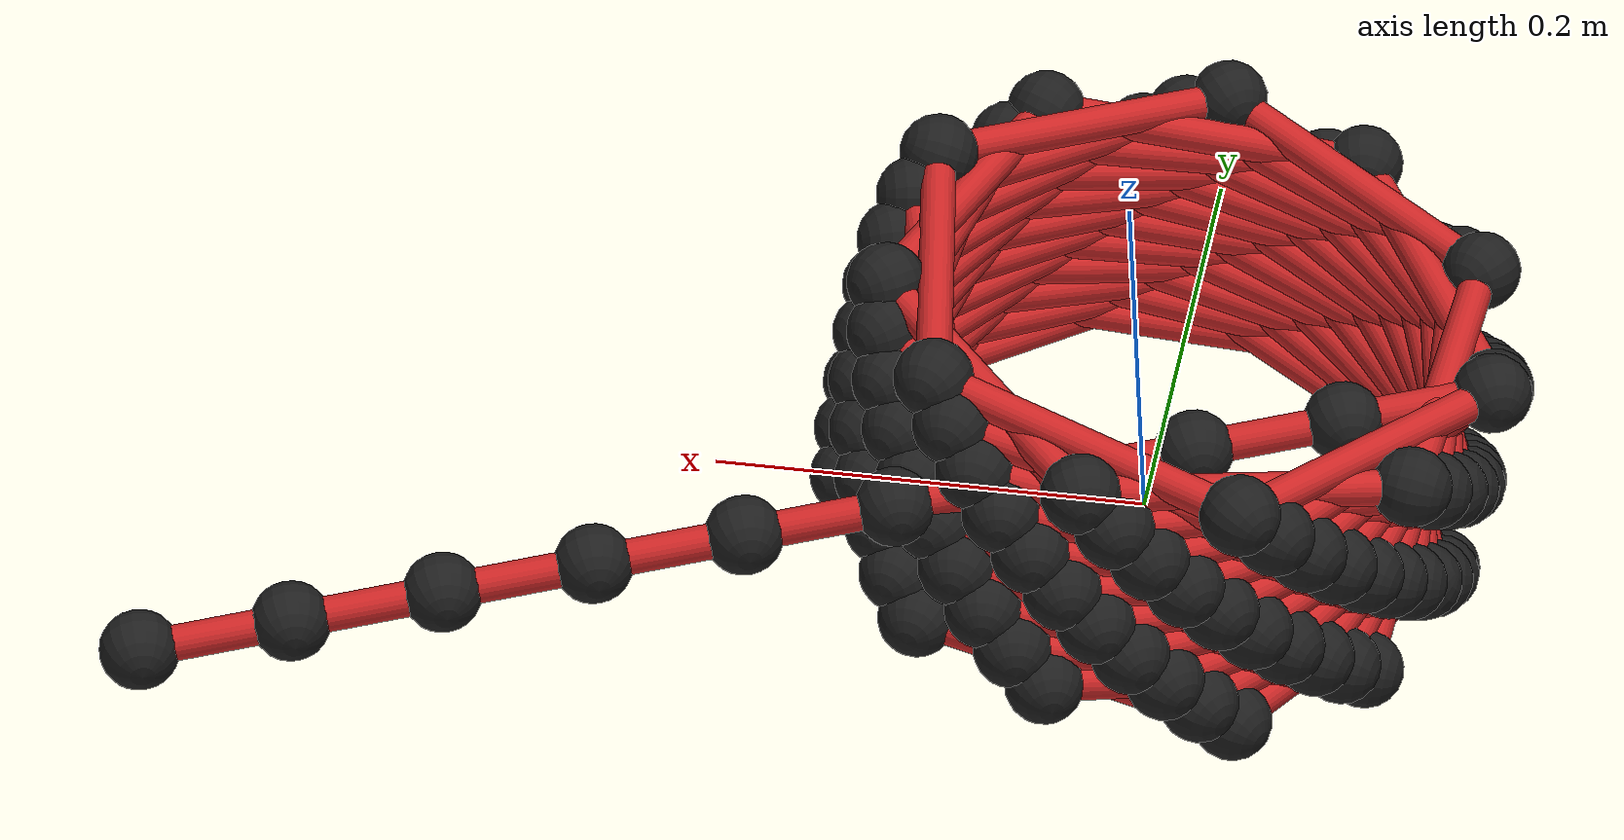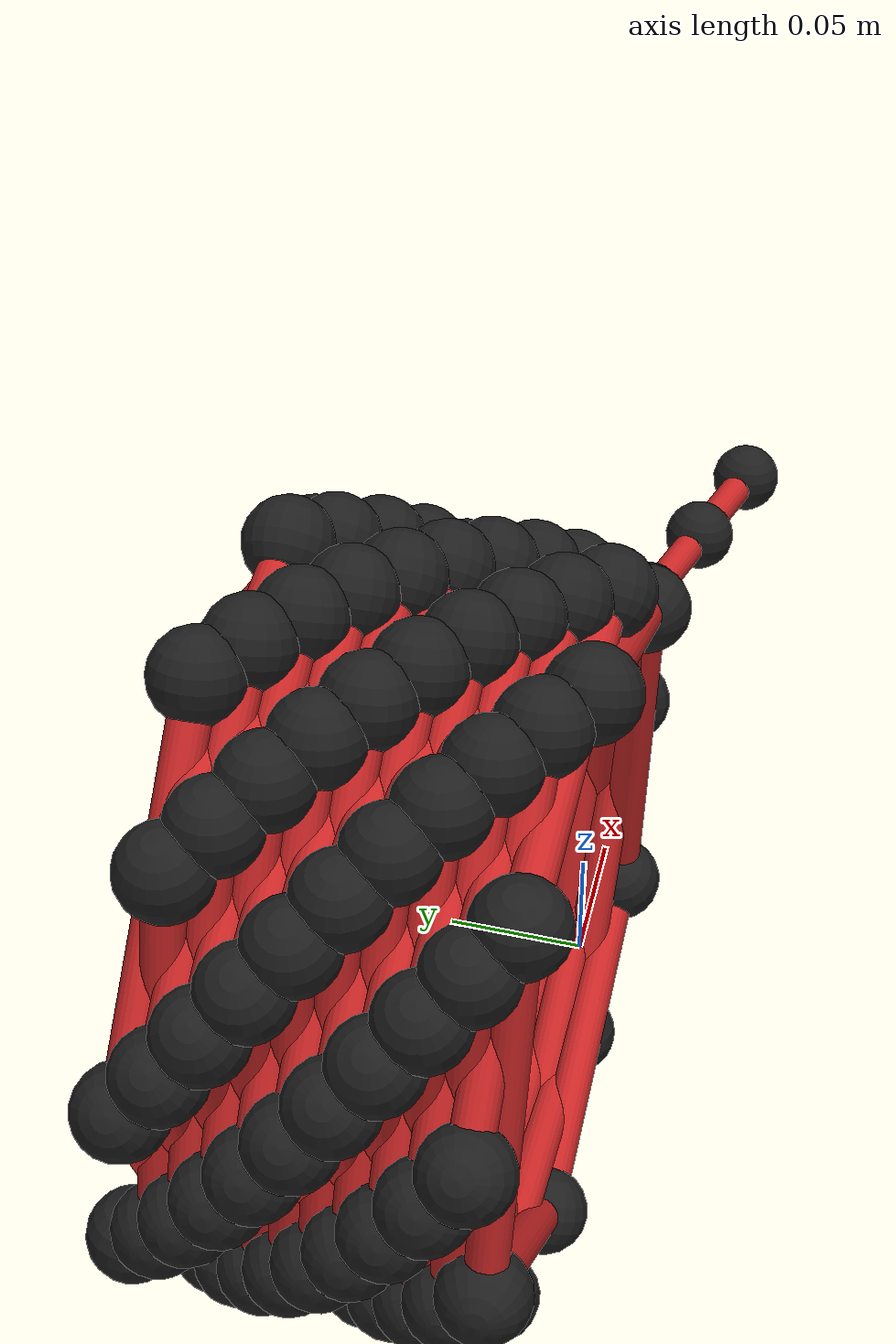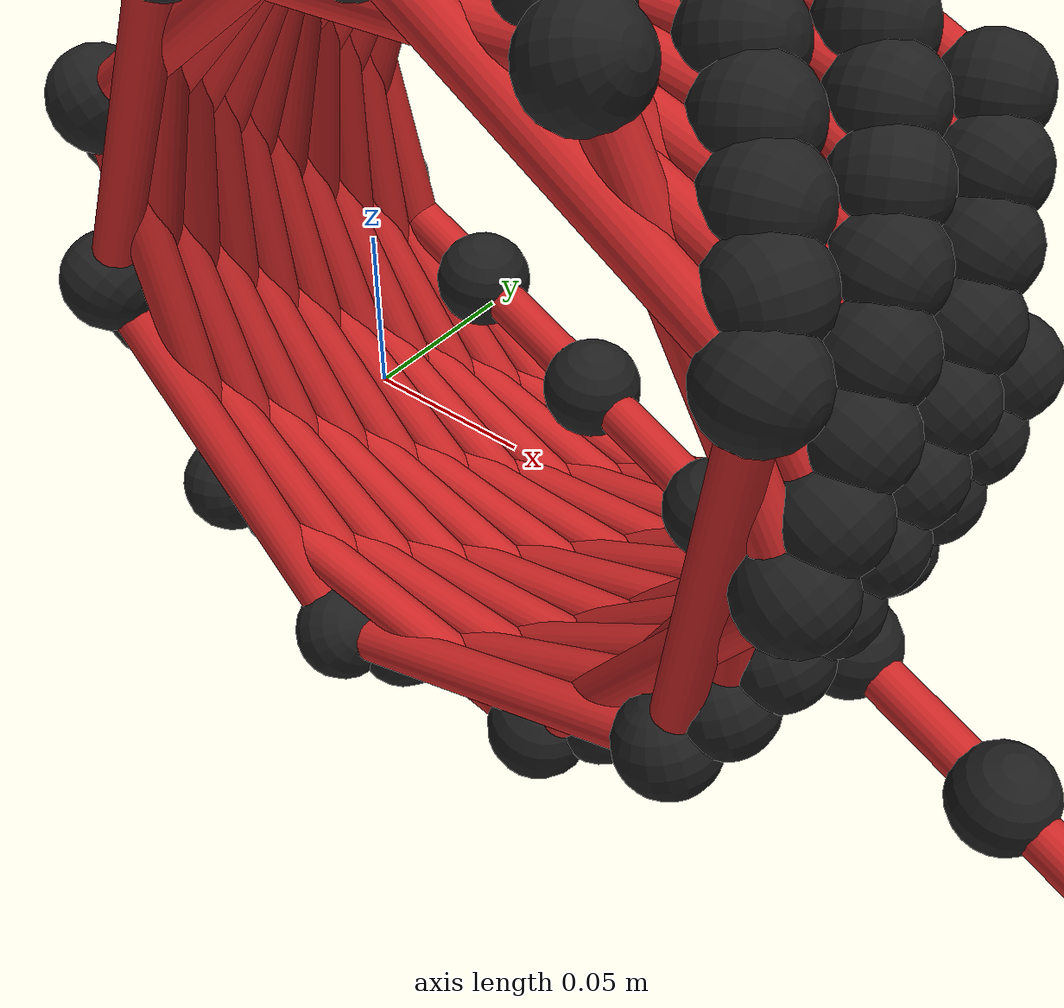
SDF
<?xml version="1.0" ?>
<!-- DO NOT EDIT: Generated from tether.sdf.jinja -->
<sdf version="1.5">
  <model name="tether">
    <pose>0.0 0.0 0.0 0.0 0.0 0.0</pose>

      <link name="link_0"><gravity>true</gravity>
      <pose>0.0 0.0 0.14 0.0 0.5653331295056458 0.009473907077987965</pose>
      <inertial>
        <mass>0.0015</mass>
        <inertia>
          <ixx>0.01</ixx>
          <ixy>0</ixy>
          <ixz>0</ixz>
          <iyy>0.01</iyy>
          <iyz>0</iyz>
          <izz>0.01</izz>
        </inertia>
      </inertial><collision name="collision">
        <pose>0.1 0 0 0 1.570790 0</pose>
        <geometry>
          <cylinder>
            <length>0.15</length>
            <radius>0.004</radius>
          </cylinder>
        </geometry>
        <surface>
          <contact>
            <ode>
          <min_depth>0.001</min_depth>
            </ode>
          </contact>
          <friction>
            <ode>
          <mu>1.0</mu>
          <mu2>1.0</mu2>
            </ode>
          </friction>
        </surface>
      </collision>
          <visual name="element_visual">
        <pose>0.075 0 0 0 1.570790 0</pose>
        <geometry>
          <cylinder>
            <length>0.15</length>
            <radius>0.008</radius>
          </cylinder>
        </geometry>
        <material>
        <script>
          <name>Gazebo/Red</name>
          <uri>file://media/materials/scripts/gazebo.material</uri>
        </script>
      </material>
      </visual><visual name="sphere_visual">
        <geometry>
          <sphere>
            <radius>0.018</radius>
          </sphere>
        </geometry>
        <material>
        <script>
          <name>Gazebo/Black</name>
          <uri>file://media/materials/scripts/gazebo.material</uri>
        </script>
      </material>
      </visual>
    </link>
      <plugin name="link_0_drag" filename="libLiftDragPlugin.so">
      <robotNamespace></robotNamespace>
      <a0>0</a0>
      <cla>0</cla>
      <cda>1.2535816618911175</cda>
      <alpha_stall>0</alpha_stall>
      <cda_stall>1.4326647564469914</cda_stall>
      <cp>0 0 0</cp>
      <area>0.0012</area>
      <air_density>1.2041</air_density>
      <forward>0 1 0</forward>
      <upward>0 0 1</upward><link_name>link_0</link_name></plugin>

      <link name="link_1"><gravity>true</gravity>
      <pose>0.1266598973307524 0.0012 0.05964285714285716 0.0 1.4452785079592854 3.0776474931390307</pose>
      <inertial>
        <mass>0.0015</mass>
        <inertia>
          <ixx>0.01</ixx>
          <ixy>0</ixy>
          <ixz>0</ixz>
          <iyy>0.01</iyy>
          <iyz>0</iyz>
          <izz>0.01</izz>
        </inertia>
      </inertial><collision name="collision">
        <pose>0.1 0 0 0 1.570790 0</pose>
        <geometry>
          <cylinder>
            <length>0.15</length>
            <radius>0.004</radius>
          </cylinder>
        </geometry>
        <surface>
          <contact>
            <ode>
          <min_depth>0.001</min_depth>
            </ode>
          </contact>
          <friction>
            <ode>
          <mu>1.0</mu>
          <mu2>1.0</mu2>
            </ode>
          </friction>
        </surface>
      </collision>
          <visual name="element_visual">
        <pose>0.075 0 0 0 1.570790 0</pose>
        <geometry>
          <cylinder>
            <length>0.15</length>
            <radius>0.008</radius>
          </cylinder>
        </geometry>
        <material>
        <script>
          <name>Gazebo/Red</name>
          <uri>file://media/materials/scripts/gazebo.material</uri>
        </script>
      </material>
      </visual><visual name="sphere_visual">
        <geometry>
          <sphere>
            <radius>0.018</radius>
          </sphere>
        </geometry>
        <material>
        <script>
          <name>Gazebo/Black</name>
          <uri>file://media/materials/scripts/gazebo.material</uri>
        </script>
      </material>
      </visual>
    </link>
      <plugin name="link_1_drag" filename="libLiftDragPlugin.so">
      <robotNamespace></robotNamespace>
      <a0>0</a0>
      <cla>0</cla>
      <cda>1.2535816618911175</cda>
      <alpha_stall>0</alpha_stall>
      <cda_stall>1.4326647564469914</cda_stall>
      <cp>0 0 0</cp>
      <area>0.0012</area>
      <air_density>1.2041</air_density>
      <forward>0 1 0</forward>
      <upward>0 0 1</upward><link_name>link_1</link_name></plugin>

      <link name="link_2"><gravity>true</gravity>
      <pose>0.10791940231752883 0.0024 -0.08918185131195334 0.0 0.3148150819152502 3.1331793311392535</pose>
      <inertial>
        <mass>0.0015</mass>
        <inertia>
          <ixx>0.01</ixx>
          <ixy>0</ixy>
          <ixz>0</ixz>
          <iyy>0.01</iyy>
          <iyz>0</iyz>
          <izz>0.01</izz>
        </inertia>
      </inertial><collision name="collision">
        <pose>0.1 0 0 0 1.570790 0</pose>
        <geometry>
          <cylinder>
            <length>0.15</length>
            <radius>0.004</radius>
          </cylinder>
        </geometry>
        <surface>
          <contact>
            <ode>
          <min_depth>0.001</min_depth>
            </ode>
          </contact>
          <friction>
            <ode>
          <mu>1.0</mu>
          <mu2>1.0</mu2>
            </ode>
          </friction>
        </surface>
      </collision>
          <visual name="element_visual">
        <pose>0.075 0 0 0 1.570790 0</pose>
        <geometry>
          <cylinder>
            <length>0.15</length>
            <radius>0.008</radius>
          </cylinder>
        </geometry>
        <material>
        <script>
          <name>Gazebo/Red</name>
          <uri>file://media/materials/scripts/gazebo.material</uri>
        </script>
      </material>
      </visual><visual name="sphere_visual">
        <geometry>
          <sphere>
            <radius>0.018</radius>
          </sphere>
        </geometry>
        <material>
        <script>
          <name>Gazebo/Black</name>
          <uri>file://media/materials/scripts/gazebo.material</uri>
        </script>
      </material>
      </visual>
    </link>
      <plugin name="link_2_drag" filename="libLiftDragPlugin.so">
      <robotNamespace></robotNamespace>
      <a0>0</a0>
      <cla>0</cla>
      <cda>1.2535816618911175</cda>
      <alpha_stall>0</alpha_stall>
      <cda_stall>1.4326647564469914</cda_stall>
      <cp>0 0 0</cp>
      <area>0.0012</area>
      <air_density>1.2041</air_density>
      <forward>0 1 0</forward>
      <upward>0 0 1</upward><link_name>link_2</link_name></plugin>

      <link name="link_3"><gravity>true</gravity>
      <pose>-0.03470816168265386 0.0036 -0.13562943453620516 0.0 -0.8158473474109663 3.12991821638624</pose>
      <inertial>
        <mass>0.0015</mass>
        <inertia>
          <ixx>0.01</ixx>
          <ixy>0</ixy>
          <ixz>0</ixz>
          <iyy>0.01</iyy>
          <iyz>0</iyz>
          <izz>0.01</izz>
        </inertia>
      </inertial><collision name="collision">
        <pose>0.1 0 0 0 1.570790 0</pose>
        <geometry>
          <cylinder>
            <length>0.15</length>
            <radius>0.004</radius>
          </cylinder>
        </geometry>
        <surface>
          <contact>
            <ode>
          <min_depth>0.001</min_depth>
            </ode>
          </contact>
          <friction>
            <ode>
          <mu>1.0</mu>
          <mu2>1.0</mu2>
            </ode>
          </friction>
        </surface>
      </collision>
          <visual name="element_visual">
        <pose>0.075 0 0 0 1.570790 0</pose>
        <geometry>
          <cylinder>
            <length>0.15</length>
            <radius>0.008</radius>
          </cylinder>
        </geometry>
        <material>
        <script>
          <name>Gazebo/Red</name>
          <uri>file://media/materials/scripts/gazebo.material</uri>
        </script>
      </material>
      </visual><visual name="sphere_visual">
        <geometry>
          <sphere>
            <radius>0.018</radius>
          </sphere>
        </geometry>
        <material>
        <script>
          <name>Gazebo/Black</name>
          <uri>file://media/materials/scripts/gazebo.material</uri>
        </script>
      </material>
      </visual>
    </link>
      <plugin name="link_3_drag" filename="libLiftDragPlugin.so">
      <robotNamespace></robotNamespace>
      <a0>0</a0>
      <cla>0</cla>
      <cda>1.2535816618911175</cda>
      <alpha_stall>0</alpha_stall>
      <cda_stall>1.4326647564469914</cda_stall>
      <cp>0 0 0</cp>
      <area>0.0012</area>
      <air_density>1.2041</air_density>
      <forward>0 1 0</forward>
      <upward>0 0 1</upward><link_name>link_3</link_name></plugin>

      <link name="link_4"><gravity>true</gravity>
      <pose>-0.1374921727308104 0.0048 -0.026379962808180668 0.0 -1.194923340456617 0.021794362821427448</pose>
      <inertial>
        <mass>0.0015</mass>
        <inertia>
          <ixx>0.01</ixx>
          <ixy>0</ixy>
          <ixz>0</ixz>
          <iyy>0.01</iyy>
          <iyz>0</iyz>
          <izz>0.01</izz>
        </inertia>
      </inertial><collision name="collision">
        <pose>0.1 0 0 0 1.570790 0</pose>
        <geometry>
          <cylinder>
            <length>0.15</length>
            <radius>0.004</radius>
          </cylinder>
        </geometry>
        <surface>
          <contact>
            <ode>
          <min_depth>0.001</min_depth>
            </ode>
          </contact>
          <friction>
            <ode>
          <mu>1.0</mu>
          <mu2>1.0</mu2>
            </ode>
          </friction>
        </surface>
      </collision>
          <visual name="element_visual">
        <pose>0.075 0 0 0 1.570790 0</pose>
        <geometry>
          <cylinder>
            <length>0.15</length>
            <radius>0.008</radius>
          </cylinder>
        </geometry>
        <material>
        <script>
          <name>Gazebo/Red</name>
          <uri>file://media/materials/scripts/gazebo.material</uri>
        </script>
      </material>
      </visual><visual name="sphere_visual">
        <geometry>
          <sphere>
            <radius>0.018</radius>
          </sphere>
        </geometry>
        <material>
        <script>
          <name>Gazebo/Black</name>
          <uri>file://media/materials/scripts/gazebo.material</uri>
        </script>
      </material>
      </visual>
    </link>
      <plugin name="link_4_drag" filename="libLiftDragPlugin.so">
      <robotNamespace></robotNamespace>
      <a0>0</a0>
      <cla>0</cla>
      <cda>1.2535816618911175</cda>
      <alpha_stall>0</alpha_stall>
      <cda_stall>1.4326647564469914</cda_stall>
      <cp>0 0 0</cp>
      <area>0.0012</area>
      <air_density>1.2041</air_density>
      <forward>0 1 0</forward>
      <upward>0 0 1</upward><link_name>link_4</link_name></plugin>

      <link name="link_5"><gravity>true</gravity>
      <pose>-0.08244078140941427 0.005999999999999999 0.11315262949045939 0.0 -0.06429551430548142 0.008016393523649749</pose>
      <inertial>
        <mass>0.0015</mass>
        <inertia>
          <ixx>0.01</ixx>
          <ixy>0</ixy>
          <ixz>0</ixz>
          <iyy>0.01</iyy>
          <iyz>0</iyz>
          <izz>0.01</izz>
        </inertia>
      </inertial><collision name="collision">
        <pose>0.1 0 0 0 1.570790 0</pose>
        <geometry>
          <cylinder>
            <length>0.15</length>
            <radius>0.004</radius>
          </cylinder>
        </geometry>
        <surface>
          <contact>
            <ode>
          <min_depth>0.001</min_depth>
            </ode>
          </contact>
          <friction>
            <ode>
          <mu>1.0</mu>
          <mu2>1.0</mu2>
            </ode>
          </friction>
        </surface>
      </collision>
          <visual name="element_visual">
        <pose>0.075 0 0 0 1.570790 0</pose>
        <geometry>
          <cylinder>
            <length>0.15</length>
            <radius>0.008</radius>
          </cylinder>
        </geometry>
        <material>
        <script>
          <name>Gazebo/Red</name>
          <uri>file://media/materials/scripts/gazebo.material</uri>
        </script>
      </material>
      </visual><visual name="sphere_visual">
        <geometry>
          <sphere>
            <radius>0.018</radius>
          </sphere>
        </geometry>
        <material>
        <script>
          <name>Gazebo/Black</name>
          <uri>file://media/materials/scripts/gazebo.material</uri>
        </script>
      </material>
      </visual>
    </link>
      <plugin name="link_5_drag" filename="libLiftDragPlugin.so">
      <robotNamespace></robotNamespace>
      <a0>0</a0>
      <cla>0</cla>
      <cda>1.2535816618911175</cda>
      <alpha_stall>0</alpha_stall>
      <cda_stall>1.4326647564469914</cda_stall>
      <cp>0 0 0</cp>
      <area>0.0012</area>
      <air_density>1.2041</air_density>
      <forward>0 1 0</forward>
      <upward>0 0 1</upward><link_name>link_5</link_name></plugin>

      <link name="link_6"><gravity>true</gravity>
      <pose>0.06724926204013608 0.0072 0.12279062160872513 0.0 1.0663513220347165 0.016552350488817508</pose>
      <inertial>
        <mass>0.0015</mass>
        <inertia>
          <ixx>0.01</ixx>
          <ixy>0</ixy>
          <ixz>0</ixz>
          <iyy>0.01</iyy>
          <iyz>0</iyz>
          <izz>0.01</izz>
        </inertia>
      </inertial><collision name="collision">
        <pose>0.1 0 0 0 1.570790 0</pose>
        <geometry>
          <cylinder>
            <length>0.15</length>
            <radius>0.004</radius>
          </cylinder>
        </geometry>
        <surface>
          <contact>
            <ode>
          <min_depth>0.001</min_depth>
            </ode>
          </contact>
          <friction>
            <ode>
          <mu>1.0</mu>
          <mu2>1.0</mu2>
            </ode>
          </friction>
        </surface>
      </collision>
          <visual name="element_visual">
        <pose>0.075 0 0 0 1.570790 0</pose>
        <geometry>
          <cylinder>
            <length>0.15</length>
            <radius>0.008</radius>
          </cylinder>
        </geometry>
        <material>
        <script>
          <name>Gazebo/Red</name>
          <uri>file://media/materials/scripts/gazebo.material</uri>
        </script>
      </material>
      </visual><visual name="sphere_visual">
        <geometry>
          <sphere>
            <radius>0.018</radius>
          </sphere>
        </geometry>
        <material>
        <script>
          <name>Gazebo/Black</name>
          <uri>file://media/materials/scripts/gazebo.material</uri>
        </script>
      </material>
      </visual>
    </link>
      <plugin name="link_6_drag" filename="libLiftDragPlugin.so">
      <robotNamespace></robotNamespace>
      <a0>0</a0>
      <cla>0</cla>
      <cda>1.2535816618911175</cda>
      <alpha_stall>0</alpha_stall>
      <cda_stall>1.4326647564469914</cda_stall>
      <cp>0 0 0</cp>
      <area>0.0012</area>
      <air_density>1.2041</air_density>
      <forward>0 1 0</forward>
      <upward>0 0 1</upward><link_name>link_6</link_name></plugin>

      <link name="link_7"><gravity>true</gravity>
      <pose>0.13973989753544852 0.0084 -0.008530008017719087 0.0 0.9444322808277015 3.1279455152475846</pose>
      <inertial>
        <mass>0.0015</mass>
        <inertia>
          <ixx>0.01</ixx>
          <ixy>0</ixy>
          <ixz>0</ixz>
          <iyy>0.01</iyy>
          <iyz>0</iyz>
          <izz>0.01</izz>
        </inertia>
      </inertial><collision name="collision">
        <pose>0.1 0 0 0 1.570790 0</pose>
        <geometry>
          <cylinder>
            <length>0.15</length>
            <radius>0.004</radius>
          </cylinder>
        </geometry>
        <surface>
          <contact>
            <ode>
          <min_depth>0.001</min_depth>
            </ode>
          </contact>
          <friction>
            <ode>
          <mu>1.0</mu>
          <mu2>1.0</mu2>
            </ode>
          </friction>
        </surface>
      </collision>
          <visual name="element_visual">
        <pose>0.075 0 0 0 1.570790 0</pose>
        <geometry>
          <cylinder>
            <length>0.15</length>
            <radius>0.008</radius>
          </cylinder>
        </geometry>
        <material>
        <script>
          <name>Gazebo/Red</name>
          <uri>file://media/materials/scripts/gazebo.material</uri>
        </script>
      </material>
      </visual><visual name="sphere_visual">
        <geometry>
          <sphere>
            <radius>0.018</radius>
          </sphere>
        </geometry>
        <material>
        <script>
          <name>Gazebo/Black</name>
          <uri>file://media/materials/scripts/gazebo.material</uri>
        </script>
      </material>
      </visual>
    </link>
      <plugin name="link_7_drag" filename="libLiftDragPlugin.so">
      <robotNamespace></robotNamespace>
      <a0>0</a0>
      <cla>0</cla>
      <cda>1.2535816618911175</cda>
      <alpha_stall>0</alpha_stall>
      <cda_stall>1.4326647564469914</cda_stall>
      <cp>0 0 0</cp>
      <area>0.0012</area>
      <air_density>1.2041</air_density>
      <forward>0 1 0</forward>
      <upward>0 0 1</upward><link_name>link_7</link_name></plugin>

      <link name="link_8"><gravity>true</gravity>
      <pose>0.0518148343293533 0.0096 -0.13005853660341435 0.0 -0.18622432432363994 3.1334520730564</pose>
      <inertial>
        <mass>0.0015</mass>
        <inertia>
          <ixx>0.01</ixx>
          <ixy>0</ixy>
          <ixz>0</ixz>
          <iyy>0.01</iyy>
          <iyz>0</iyz>
          <izz>0.01</izz>
        </inertia>
      </inertial><collision name="collision">
        <pose>0.1 0 0 0 1.570790 0</pose>
        <geometry>
          <cylinder>
            <length>0.15</length>
            <radius>0.004</radius>
          </cylinder>
        </geometry>
        <surface>
          <contact>
            <ode>
          <min_depth>0.001</min_depth>
            </ode>
          </contact>
          <friction>
            <ode>
          <mu>1.0</mu>
          <mu2>1.0</mu2>
            </ode>
          </friction>
        </surface>
      </collision>
          <visual name="element_visual">
        <pose>0.075 0 0 0 1.570790 0</pose>
        <geometry>
          <cylinder>
            <length>0.15</length>
            <radius>0.008</radius>
          </cylinder>
        </geometry>
        <material>
        <script>
          <name>Gazebo/Red</name>
          <uri>file://media/materials/scripts/gazebo.material</uri>
        </script>
      </material>
      </visual><visual name="sphere_visual">
        <geometry>
          <sphere>
            <radius>0.018</radius>
          </sphere>
        </geometry>
        <material>
        <script>
          <name>Gazebo/Black</name>
          <uri>file://media/materials/scripts/gazebo.material</uri>
        </script>
      </material>
      </visual>
    </link>
      <plugin name="link_8_drag" filename="libLiftDragPlugin.so">
      <robotNamespace></robotNamespace>
      <a0>0</a0>
      <cla>0</cla>
      <cda>1.2535816618911175</cda>
      <alpha_stall>0</alpha_stall>
      <cda_stall>1.4326647564469914</cda_stall>
      <cp>0 0 0</cp>
      <area>0.0012</area>
      <air_density>1.2041</air_density>
      <forward>0 1 0</forward>
      <upward>0 0 1</upward><link_name>link_8</link_name></plugin>

      <link name="link_9"><gravity>true</gravity>
      <pose>-0.09559154379564236 0.010799999999999999 -0.10228517368008812 0.0 -1.3168139143218818 3.1097488376826106</pose>
      <inertial>
        <mass>0.0015</mass>
        <inertia>
          <ixx>0.01</ixx>
          <ixy>0</ixy>
          <ixz>0</ixz>
          <iyy>0.01</iyy>
          <iyz>0</iyz>
          <izz>0.01</izz>
        </inertia>
      </inertial><collision name="collision">
        <pose>0.1 0 0 0 1.570790 0</pose>
        <geometry>
          <cylinder>
            <length>0.15</length>
            <radius>0.004</radius>
          </cylinder>
        </geometry>
        <surface>
          <contact>
            <ode>
          <min_depth>0.001</min_depth>
            </ode>
          </contact>
          <friction>
            <ode>
          <mu>1.0</mu>
          <mu2>1.0</mu2>
            </ode>
          </friction>
        </surface>
      </collision>
          <visual name="element_visual">
        <pose>0.075 0 0 0 1.570790 0</pose>
        <geometry>
          <cylinder>
            <length>0.15</length>
            <radius>0.008</radius>
          </cylinder>
        </geometry>
        <material>
        <script>
          <name>Gazebo/Red</name>
          <uri>file://media/materials/scripts/gazebo.material</uri>
        </script>
      </material>
      </visual><visual name="sphere_visual">
        <geometry>
          <sphere>
            <radius>0.018</radius>
          </sphere>
        </geometry>
        <material>
        <script>
          <name>Gazebo/Black</name>
          <uri>file://media/materials/scripts/gazebo.material</uri>
        </script>
      </material>
      </visual>
    </link>
      <plugin name="link_9_drag" filename="libLiftDragPlugin.so">
      <robotNamespace></robotNamespace>
      <a0>0</a0>
      <cla>0</cla>
      <cda>1.2535816618911175</cda>
      <alpha_stall>0</alpha_stall>
      <cda_stall>1.4326647564469914</cda_stall>
      <cp>0 0 0</cp>
      <area>0.0012</area>
      <air_density>1.2041</air_density>
      <forward>0 1 0</forward>
      <upward>0 0 1</upward><link_name>link_9</link_name></plugin>

      <link name="link_10"><gravity>true</gravity>
      <pose>-0.1332627313389058 0.011999999999999999 0.042907393722931064 0.0 -0.693921957072192 0.01040644528385963</pose>
      <inertial>
        <mass>0.0015</mass>
        <inertia>
          <ixx>0.01</ixx>
          <ixy>0</ixy>
          <ixz>0</ixz>
          <iyy>0.01</iyy>
          <iyz>0</iyz>
          <izz>0.01</izz>
        </inertia>
      </inertial><collision name="collision">
        <pose>0.1 0 0 0 1.570790 0</pose>
        <geometry>
          <cylinder>
            <length>0.15</length>
            <radius>0.004</radius>
          </cylinder>
        </geometry>
        <surface>
          <contact>
            <ode>
          <min_depth>0.001</min_depth>
            </ode>
          </contact>
          <friction>
            <ode>
          <mu>1.0</mu>
          <mu2>1.0</mu2>
            </ode>
          </friction>
        </surface>
      </collision>
          <visual name="element_visual">
        <pose>0.075 0 0 0 1.570790 0</pose>
        <geometry>
          <cylinder>
            <length>0.15</length>
            <radius>0.008</radius>
          </cylinder>
        </geometry>
        <material>
        <script>
          <name>Gazebo/Red</name>
          <uri>file://media/materials/scripts/gazebo.material</uri>
        </script>
      </material>
      </visual><visual name="sphere_visual">
        <geometry>
          <sphere>
            <radius>0.018</radius>
          </sphere>
        </geometry>
        <material>
        <script>
          <name>Gazebo/Black</name>
          <uri>file://media/materials/scripts/gazebo.material</uri>
        </script>
      </material>
      </visual>
    </link>
      <plugin name="link_10_drag" filename="libLiftDragPlugin.so">
      <robotNamespace></robotNamespace>
      <a0>0</a0>
      <cla>0</cla>
      <cda>1.2535816618911175</cda>
      <alpha_stall>0</alpha_stall>
      <cda_stall>1.4326647564469914</cda_stall>
      <cp>0 0 0</cp>
      <area>0.0012</area>
      <air_density>1.2041</air_density>
      <forward>0 1 0</forward>
      <upward>0 0 1</upward><link_name>link_10</link_name></plugin>

      <link name="link_11"><gravity>true</gravity>
      <pose>-0.017953742600262116 0.013199999999999998 0.1388440244542182 0.0 0.43674334342527776 0.008828548449630333</pose>
      <inertial>
        <mass>0.0015</mass>
        <inertia>
          <ixx>0.01</ixx>
          <ixy>0</ixy>
          <ixz>0</ixz>
          <iyy>0.01</iyy>
          <iyz>0</iyz>
          <izz>0.01</izz>
        </inertia>
      </inertial><collision name="collision">
        <pose>0.1 0 0 0 1.570790 0</pose>
        <geometry>
          <cylinder>
            <length>0.15</length>
            <radius>0.004</radius>
          </cylinder>
        </geometry>
        <surface>
          <contact>
            <ode>
          <min_depth>0.001</min_depth>
            </ode>
          </contact>
          <friction>
            <ode>
          <mu>1.0</mu>
          <mu2>1.0</mu2>
            </ode>
          </friction>
        </surface>
      </collision>
          <visual name="element_visual">
        <pose>0.075 0 0 0 1.570790 0</pose>
        <geometry>
          <cylinder>
            <length>0.15</length>
            <radius>0.008</radius>
          </cylinder>
        </geometry>
        <material>
        <script>
          <name>Gazebo/Red</name>
          <uri>file://media/materials/scripts/gazebo.material</uri>
        </script>
      </material>
      </visual><visual name="sphere_visual">
        <geometry>
          <sphere>
            <radius>0.018</radius>
          </sphere>
        </geometry>
        <material>
        <script>
          <name>Gazebo/Black</name>
          <uri>file://media/materials/scripts/gazebo.material</uri>
        </script>
      </material>
      </visual>
    </link>
      <plugin name="link_11_drag" filename="libLiftDragPlugin.so">
      <robotNamespace></robotNamespace>
      <a0>0</a0>
      <cla>0</cla>
      <cda>1.2535816618911175</cda>
      <alpha_stall>0</alpha_stall>
      <cda_stall>1.4326647564469914</cda_stall>
      <cp>0 0 0</cp>
      <area>0.0012</area>
      <air_density>1.2041</air_density>
      <forward>0 1 0</forward>
      <upward>0 0 1</upward><link_name>link_11</link_name></plugin>

      <link name="link_12"><gravity>true</gravity>
      <pose>0.11796540983766216 0.0144 0.07539338221510164 0.0 1.5621306573043436 1.1762346782778348</pose>
      <inertial>
        <mass>0.0015</mass>
        <inertia>
          <ixx>0.01</ixx>
          <ixy>0</ixy>
          <ixz>0</ixz>
          <iyy>0.01</iyy>
          <iyz>0</iyz>
          <izz>0.01</izz>
        </inertia>
      </inertial><collision name="collision">
        <pose>0.1 0 0 0 1.570790 0</pose>
        <geometry>
          <cylinder>
            <length>0.15</length>
            <radius>0.004</radius>
          </cylinder>
        </geometry>
        <surface>
          <contact>
            <ode>
          <min_depth>0.001</min_depth>
            </ode>
          </contact>
          <friction>
            <ode>
          <mu>1.0</mu>
          <mu2>1.0</mu2>
            </ode>
          </friction>
        </surface>
      </collision>
          <visual name="element_visual">
        <pose>0.075 0 0 0 1.570790 0</pose>
        <geometry>
          <cylinder>
            <length>0.15</length>
            <radius>0.008</radius>
          </cylinder>
        </geometry>
        <material>
        <script>
          <name>Gazebo/Red</name>
          <uri>file://media/materials/scripts/gazebo.material</uri>
        </script>
      </material>
      </visual><visual name="sphere_visual">
        <geometry>
          <sphere>
            <radius>0.018</radius>
          </sphere>
        </geometry>
        <material>
        <script>
          <name>Gazebo/Black</name>
          <uri>file://media/materials/scripts/gazebo.material</uri>
        </script>
      </material>
      </visual>
    </link>
      <plugin name="link_12_drag" filename="libLiftDragPlugin.so">
      <robotNamespace></robotNamespace>
      <a0>0</a0>
      <cla>0</cla>
      <cda>1.2535816618911175</cda>
      <alpha_stall>0</alpha_stall>
      <cda_stall>1.4326647564469914</cda_stall>
      <cp>0 0 0</cp>
      <area>0.0012</area>
      <air_density>1.2041</air_density>
      <forward>0 1 0</forward>
      <upward>0 0 1</upward><link_name>link_12</link_name></plugin>

      <link name="link_13"><gravity>true</gravity>
      <pose>0.11846508669663733 0.0156 -0.07460578552604484 0.0 0.44340545341112503 3.1327363656737224</pose>
      <inertial>
        <mass>0.0015</mass>
        <inertia>
          <ixx>0.01</ixx>
          <ixy>0</ixy>
          <ixz>0</ixz>
          <iyy>0.01</iyy>
          <iyz>0</iyz>
          <izz>0.01</izz>
        </inertia>
      </inertial><collision name="collision">
        <pose>0.1 0 0 0 1.570790 0</pose>
        <geometry>
          <cylinder>
            <length>0.15</length>
            <radius>0.004</radius>
          </cylinder>
        </geometry>
        <surface>
          <contact>
            <ode>
          <min_depth>0.001</min_depth>
            </ode>
          </contact>
          <friction>
            <ode>
          <mu>1.0</mu>
          <mu2>1.0</mu2>
            </ode>
          </friction>
        </surface>
      </collision>
          <visual name="element_visual">
        <pose>0.075 0 0 0 1.570790 0</pose>
        <geometry>
          <cylinder>
            <length>0.15</length>
            <radius>0.008</radius>
          </cylinder>
        </geometry>
        <material>
        <script>
          <name>Gazebo/Red</name>
          <uri>file://media/materials/scripts/gazebo.material</uri>
        </script>
      </material>
      </visual><visual name="sphere_visual">
        <geometry>
          <sphere>
            <radius>0.018</radius>
          </sphere>
        </geometry>
        <material>
        <script>
          <name>Gazebo/Black</name>
          <uri>file://media/materials/scripts/gazebo.material</uri>
        </script>
      </material>
      </visual>
    </link>
      <plugin name="link_13_drag" filename="libLiftDragPlugin.so">
      <robotNamespace></robotNamespace>
      <a0>0</a0>
      <cla>0</cla>
      <cda>1.2535816618911175</cda>
      <alpha_stall>0</alpha_stall>
      <cda_stall>1.4326647564469914</cda_stall>
      <cp>0 0 0</cp>
      <area>0.0012</area>
      <air_density>1.2041</air_density>
      <forward>0 1 0</forward>
      <upward>0 0 1</upward><link_name>link_13</link_name></plugin>

      <link name="link_14"><gravity>true</gravity>
      <pose>-0.01702832066246599 0.0168 -0.13896055661739498 0.0 -0.6872599453919931 3.1312433410064533</pose>
      <inertial>
        <mass>0.0015</mass>
        <inertia>
          <ixx>0.01</ixx>
          <ixy>0</ixy>
          <ixz>0</ixz>
          <iyy>0.01</iyy>
          <iyz>0</iyz>
          <izz>0.01</izz>
        </inertia>
      </inertial><collision name="collision">
        <pose>0.1 0 0 0 1.570790 0</pose>
        <geometry>
          <cylinder>
            <length>0.15</length>
            <radius>0.004</radius>
          </cylinder>
        </geometry>
        <surface>
          <contact>
            <ode>
          <min_depth>0.001</min_depth>
            </ode>
          </contact>
          <friction>
            <ode>
          <mu>1.0</mu>
          <mu2>1.0</mu2>
            </ode>
          </friction>
        </surface>
      </collision>
          <visual name="element_visual">
        <pose>0.075 0 0 0 1.570790 0</pose>
        <geometry>
          <cylinder>
            <length>0.15</length>
            <radius>0.008</radius>
          </cylinder>
        </geometry>
        <material>
        <script>
          <name>Gazebo/Red</name>
          <uri>file://media/materials/scripts/gazebo.material</uri>
        </script>
      </material>
      </visual><visual name="sphere_visual">
        <geometry>
          <sphere>
            <radius>0.018</radius>
          </sphere>
        </geometry>
        <material>
        <script>
          <name>Gazebo/Black</name>
          <uri>file://media/materials/scripts/gazebo.material</uri>
        </script>
      </material>
      </visual>
    </link>
      <plugin name="link_14_drag" filename="libLiftDragPlugin.so">
      <robotNamespace></robotNamespace>
      <a0>0</a0>
      <cla>0</cla>
      <cda>1.2535816618911175</cda>
      <alpha_stall>0</alpha_stall>
      <cda_stall>1.4326647564469914</cda_stall>
      <cp>0 0 0</cp>
      <area>0.0012</area>
      <air_density>1.2041</air_density>
      <forward>0 1 0</forward>
      <upward>0 0 1</upward><link_name>link_14</link_name></plugin>

      <link name="link_15"><gravity>true</gravity>
      <pose>-0.1329739109345547 0.018 -0.04379428057142977 0.0 -1.323472818132001 0.03268320431060282</pose>
      <inertial>
        <mass>0.0015</mass>
        <inertia>
          <ixx>0.01</ixx>
          <ixy>0</ixy>
          <ixz>0</ixz>
          <iyy>0.01</iyy>
          <iyz>0</iyz>
          <izz>0.01</izz>
        </inertia>
      </inertial><collision name="collision">
        <pose>0.1 0 0 0 1.570790 0</pose>
        <geometry>
          <cylinder>
            <length>0.15</length>
            <radius>0.004</radius>
          </cylinder>
        </geometry>
        <surface>
          <contact>
            <ode>
          <min_depth>0.001</min_depth>
            </ode>
          </contact>
          <friction>
            <ode>
          <mu>1.0</mu>
          <mu2>1.0</mu2>
            </ode>
          </friction>
        </surface>
      </collision>
          <visual name="element_visual">
        <pose>0.075 0 0 0 1.570790 0</pose>
        <geometry>
          <cylinder>
            <length>0.15</length>
            <radius>0.008</radius>
          </cylinder>
        </geometry>
        <material>
        <script>
          <name>Gazebo/Red</name>
          <uri>file://media/materials/scripts/gazebo.material</uri>
        </script>
      </material>
      </visual><visual name="sphere_visual">
        <geometry>
          <sphere>
            <radius>0.018</radius>
          </sphere>
        </geometry>
        <material>
        <script>
          <name>Gazebo/Black</name>
          <uri>file://media/materials/scripts/gazebo.material</uri>
        </script>
      </material>
      </visual>
    </link>
      <plugin name="link_15_drag" filename="libLiftDragPlugin.so">
      <robotNamespace></robotNamespace>
      <a0>0</a0>
      <cla>0</cla>
      <cda>1.2535816618911175</cda>
      <alpha_stall>0</alpha_stall>
      <cda_stall>1.4326647564469914</cda_stall>
      <cp>0 0 0</cp>
      <area>0.0012</area>
      <air_density>1.2041</air_density>
      <forward>0 1 0</forward>
      <upward>0 0 1</upward><link_name>link_15</link_name></plugin>

      <link name="link_16"><gravity>true</gravity>
      <pose>-0.09627087896034353 0.0192 0.10164604204888102 0.0 -0.19288647373114795 0.008150992683113015</pose>
      <inertial>
        <mass>0.0015</mass>
        <inertia>
          <ixx>0.01</ixx>
          <ixy>0</ixy>
          <ixz>0</ixz>
          <iyy>0.01</iyy>
          <iyz>0</iyz>
          <izz>0.01</izz>
        </inertia>
      </inertial><collision name="collision">
        <pose>0.1 0 0 0 1.570790 0</pose>
        <geometry>
          <cylinder>
            <length>0.15</length>
            <radius>0.004</radius>
          </cylinder>
        </geometry>
        <surface>
          <contact>
            <ode>
          <min_depth>0.001</min_depth>
            </ode>
          </contact>
          <friction>
            <ode>
          <mu>1.0</mu>
          <mu2>1.0</mu2>
            </ode>
          </friction>
        </surface>
      </collision>
          <visual name="element_visual">
        <pose>0.075 0 0 0 1.570790 0</pose>
        <geometry>
          <cylinder>
            <length>0.15</length>
            <radius>0.008</radius>
          </cylinder>
        </geometry>
        <material>
        <script>
          <name>Gazebo/Red</name>
          <uri>file://media/materials/scripts/gazebo.material</uri>
        </script>
      </material>
      </visual><visual name="sphere_visual">
        <geometry>
          <sphere>
            <radius>0.018</radius>
          </sphere>
        </geometry>
        <material>
        <script>
          <name>Gazebo/Black</name>
          <uri>file://media/materials/scripts/gazebo.material</uri>
        </script>
      </material>
      </visual>
    </link>
      <plugin name="link_16_drag" filename="libLiftDragPlugin.so">
      <robotNamespace></robotNamespace>
      <a0>0</a0>
      <cla>0</cla>
      <cda>1.2535816618911175</cda>
      <alpha_stall>0</alpha_stall>
      <cda_stall>1.4326647564469914</cda_stall>
      <cp>0 0 0</cp>
      <area>0.0012</area>
      <air_density>1.2041</air_density>
      <forward>0 1 0</forward>
      <upward>0 0 1</upward><link_name>link_16</link_name></plugin>

      <link name="link_17"><gravity>true</gravity>
      <pose>0.05094719263671126 0.020399999999999998 0.13040085721511893 0.0 0.9377705251399772 0.01352292730378709</pose>
      <inertial>
        <mass>0.0015</mass>
        <inertia>
          <ixx>0.01</ixx>
          <ixy>0</ixy>
          <ixz>0</ixz>
          <iyy>0.01</iyy>
          <iyz>0</iyz>
          <izz>0.01</izz>
        </inertia>
      </inertial><collision name="collision">
        <pose>0.1 0 0 0 1.570790 0</pose>
        <geometry>
          <cylinder>
            <length>0.15</length>
            <radius>0.004</radius>
          </cylinder>
        </geometry>
        <surface>
          <contact>
            <ode>
          <min_depth>0.001</min_depth>
            </ode>
          </contact>
          <friction>
            <ode>
          <mu>1.0</mu>
          <mu2>1.0</mu2>
            </ode>
          </friction>
        </surface>
      </collision>
          <visual name="element_visual">
        <pose>0.075 0 0 0 1.570790 0</pose>
        <geometry>
          <cylinder>
            <length>0.15</length>
            <radius>0.008</radius>
          </cylinder>
        </geometry>
        <material>
        <script>
          <name>Gazebo/Red</name>
          <uri>file://media/materials/scripts/gazebo.material</uri>
        </script>
      </material>
      </visual><visual name="sphere_visual">
        <geometry>
          <sphere>
            <radius>0.018</radius>
          </sphere>
        </geometry>
        <material>
        <script>
          <name>Gazebo/Black</name>
          <uri>file://media/materials/scripts/gazebo.material</uri>
        </script>
      </material>
      </visual>
    </link>
      <plugin name="link_17_drag" filename="libLiftDragPlugin.so">
      <robotNamespace></robotNamespace>
      <a0>0</a0>
      <cla>0</cla>
      <cda>1.2535816618911175</cda>
      <alpha_stall>0</alpha_stall>
      <cda_stall>1.4326647564469914</cda_stall>
      <cp>0 0 0</cp>
      <area>0.0012</area>
      <air_density>1.2041</air_density>
      <forward>0 1 0</forward>
      <upward>0 0 1</upward><link_name>link_17</link_name></plugin>

      <link name="link_18"><gravity>true</gravity>
      <pose>0.13967996656407183 0.021599999999999998 0.00946081078236842 0.0 1.073012768656733 3.124837751080713</pose>
      <inertial>
        <mass>0.0015</mass>
        <inertia>
          <ixx>0.01</ixx>
          <ixy>0</ixy>
          <ixz>0</ixz>
          <iyy>0.01</iyy>
          <iyz>0</iyz>
          <izz>0.01</izz>
        </inertia>
      </inertial><collision name="collision">
        <pose>0.1 0 0 0 1.570790 0</pose>
        <geometry>
          <cylinder>
            <length>0.15</length>
            <radius>0.004</radius>
          </cylinder>
        </geometry>
        <surface>
          <contact>
            <ode>
          <min_depth>0.001</min_depth>
            </ode>
          </contact>
          <friction>
            <ode>
          <mu>1.0</mu>
          <mu2>1.0</mu2>
            </ode>
          </friction>
        </surface>
      </collision>
          <visual name="element_visual">
        <pose>0.075 0 0 0 1.570790 0</pose>
        <geometry>
          <cylinder>
            <length>0.15</length>
            <radius>0.008</radius>
          </cylinder>
        </geometry>
        <material>
        <script>
          <name>Gazebo/Red</name>
          <uri>file://media/materials/scripts/gazebo.material</uri>
        </script>
      </material>
      </visual><visual name="sphere_visual">
        <geometry>
          <sphere>
            <radius>0.018</radius>
          </sphere>
        </geometry>
        <material>
        <script>
          <name>Gazebo/Black</name>
          <uri>file://media/materials/scripts/gazebo.material</uri>
        </script>
      </material>
      </visual>
    </link>
      <plugin name="link_18_drag" filename="libLiftDragPlugin.so">
      <robotNamespace></robotNamespace>
      <a0>0</a0>
      <cla>0</cla>
      <cda>1.2535816618911175</cda>
      <alpha_stall>0</alpha_stall>
      <cda_stall>1.4326647564469914</cda_stall>
      <cp>0 0 0</cp>
      <area>0.0012</area>
      <air_density>1.2041</air_density>
      <forward>0 1 0</forward>
      <upward>0 0 1</upward><link_name>link_18</link_name></plugin>

      <link name="link_19"><gravity>true</gravity>
      <pose>0.06806584009900309 0.022799999999999997 -0.12233986027299912 0.0 -0.05763335784473224 3.133579519420159</pose>
      <inertial>
        <mass>0.0015</mass>
        <inertia>
          <ixx>0.01</ixx>
          <ixy>0</ixy>
          <ixz>0</ixz>
          <iyy>0.01</iyy>
          <iyz>0</iyz>
          <izz>0.01</izz>
        </inertia>
      </inertial><collision name="collision">
        <pose>0.1 0 0 0 1.570790 0</pose>
        <geometry>
          <cylinder>
            <length>0.15</length>
            <radius>0.004</radius>
          </cylinder>
        </geometry>
        <surface>
          <contact>
            <ode>
          <min_depth>0.001</min_depth>
            </ode>
          </contact>
          <friction>
            <ode>
          <mu>1.0</mu>
          <mu2>1.0</mu2>
            </ode>
          </friction>
        </surface>
      </collision>
          <visual name="element_visual">
        <pose>0.075 0 0 0 1.570790 0</pose>
        <geometry>
          <cylinder>
            <length>0.15</length>
            <radius>0.008</radius>
          </cylinder>
        </geometry>
        <material>
        <script>
          <name>Gazebo/Red</name>
          <uri>file://media/materials/scripts/gazebo.material</uri>
        </script>
      </material>
      </visual><visual name="sphere_visual">
        <geometry>
          <sphere>
            <radius>0.018</radius>
          </sphere>
        </geometry>
        <material>
        <script>
          <name>Gazebo/Black</name>
          <uri>file://media/materials/scripts/gazebo.material</uri>
        </script>
      </material>
      </visual>
    </link>
      <plugin name="link_19_drag" filename="libLiftDragPlugin.so">
      <robotNamespace></robotNamespace>
      <a0>0</a0>
      <cla>0</cla>
      <cda>1.2535816618911175</cda>
      <alpha_stall>0</alpha_stall>
      <cda_stall>1.4326647564469914</cda_stall>
      <cp>0 0 0</cp>
      <area>0.0012</area>
      <air_density>1.2041</air_density>
      <forward>0 1 0</forward>
      <upward>0 0 1</upward><link_name>link_19</link_name></plugin>

      <link name="link_20"><gravity>true</gravity>
      <pose>-0.08168509260216593 0.023999999999999997 -0.11369936519864823 0.0 -1.1882625260036572 3.120159624838857</pose>
      <inertial>
        <mass>0.0015</mass>
        <inertia>
          <ixx>0.01</ixx>
          <ixy>0</ixy>
          <ixz>0</ixz>
          <iyy>0.01</iyy>
          <iyz>0</iyz>
          <izz>0.01</izz>
        </inertia>
      </inertial><collision name="collision">
        <pose>0.1 0 0 0 1.570790 0</pose>
        <geometry>
          <cylinder>
            <length>0.15</length>
            <radius>0.004</radius>
          </cylinder>
        </geometry>
        <surface>
          <contact>
            <ode>
          <min_depth>0.001</min_depth>
            </ode>
          </contact>
          <friction>
            <ode>
          <mu>1.0</mu>
          <mu2>1.0</mu2>
            </ode>
          </friction>
        </surface>
      </collision>
          <visual name="element_visual">
        <pose>0.075 0 0 0 1.570790 0</pose>
        <geometry>
          <cylinder>
            <length>0.15</length>
            <radius>0.008</radius>
          </cylinder>
        </geometry>
        <material>
        <script>
          <name>Gazebo/Red</name>
          <uri>file://media/materials/scripts/gazebo.material</uri>
        </script>
      </material>
      </visual><visual name="sphere_visual">
        <geometry>
          <sphere>
            <radius>0.018</radius>
          </sphere>
        </geometry>
        <material>
        <script>
          <name>Gazebo/Black</name>
          <uri>file://media/materials/scripts/gazebo.material</uri>
        </script>
      </material>
      </visual>
    </link>
      <plugin name="link_20_drag" filename="libLiftDragPlugin.so">
      <robotNamespace></robotNamespace>
      <a0>0</a0>
      <cla>0</cla>
      <cda>1.2535816618911175</cda>
      <alpha_stall>0</alpha_stall>
      <cda_stall>1.4326647564469914</cda_stall>
      <cp>0 0 0</cp>
      <area>0.0012</area>
      <air_density>1.2041</air_density>
      <forward>0 1 0</forward>
      <upward>0 0 1</upward><link_name>link_20</link_name></plugin>

      <link name="link_21"><gravity>true</gravity>
      <pose>-0.137664873081461 0.025199999999999997 0.025463360333334604 0.0 -0.8225092605976422 0.011757953351011726</pose>
      <inertial>
        <mass>0.0015</mass>
        <inertia>
          <ixx>0.01</ixx>
          <ixy>0</ixy>
          <ixz>0</ixz>
          <iyy>0.01</iyy>
          <iyz>0</iyz>
          <izz>0.01</izz>
        </inertia>
      </inertial><collision name="collision">
        <pose>0.1 0 0 0 1.570790 0</pose>
        <geometry>
          <cylinder>
            <length>0.15</length>
            <radius>0.004</radius>
          </cylinder>
        </geometry>
        <surface>
          <contact>
            <ode>
          <min_depth>0.001</min_depth>
            </ode>
          </contact>
          <friction>
            <ode>
          <mu>1.0</mu>
          <mu2>1.0</mu2>
            </ode>
          </friction>
        </surface>
      </collision>
          <visual name="element_visual">
        <pose>0.075 0 0 0 1.570790 0</pose>
        <geometry>
          <cylinder>
            <length>0.15</length>
            <radius>0.008</radius>
          </cylinder>
        </geometry>
        <material>
        <script>
          <name>Gazebo/Red</name>
          <uri>file://media/materials/scripts/gazebo.material</uri>
        </script>
      </material>
      </visual><visual name="sphere_visual">
        <geometry>
          <sphere>
            <radius>0.018</radius>
          </sphere>
        </geometry>
        <material>
        <script>
          <name>Gazebo/Black</name>
          <uri>file://media/materials/scripts/gazebo.material</uri>
        </script>
      </material>
      </visual>
    </link>
      <plugin name="link_21_drag" filename="libLiftDragPlugin.so">
      <robotNamespace></robotNamespace>
      <a0>0</a0>
      <cla>0</cla>
      <cda>1.2535816618911175</cda>
      <alpha_stall>0</alpha_stall>
      <cda_stall>1.4326647564469914</cda_stall>
      <cp>0 0 0</cp>
      <area>0.0012</area>
      <air_density>1.2041</air_density>
      <forward>0 1 0</forward>
      <upward>0 0 1</upward><link_name>link_21</link_name></plugin>

      <link name="link_22"><gravity>true</gravity>
      <pose>-0.03561099823765045 0.026399999999999996 0.13539518752347907 0.0 0.30815294675998633 0.00839529495676287</pose>
      <inertial>
        <mass>0.0015</mass>
        <inertia>
          <ixx>0.01</ixx>
          <ixy>0</ixy>
          <ixz>0</ixz>
          <iyy>0.01</iyy>
          <iyz>0</iyz>
          <izz>0.01</izz>
        </inertia>
      </inertial><collision name="collision">
        <pose>0.1 0 0 0 1.570790 0</pose>
        <geometry>
          <cylinder>
            <length>0.15</length>
            <radius>0.004</radius>
          </cylinder>
        </geometry>
        <surface>
          <contact>
            <ode>
          <min_depth>0.001</min_depth>
            </ode>
          </contact>
          <friction>
            <ode>
          <mu>1.0</mu>
          <mu2>1.0</mu2>
            </ode>
          </friction>
        </surface>
      </collision>
          <visual name="element_visual">
        <pose>0.075 0 0 0 1.570790 0</pose>
        <geometry>
          <cylinder>
            <length>0.15</length>
            <radius>0.008</radius>
          </cylinder>
        </geometry>
        <material>
        <script>
          <name>Gazebo/Red</name>
          <uri>file://media/materials/scripts/gazebo.material</uri>
        </script>
      </material>
      </visual><visual name="sphere_visual">
        <geometry>
          <sphere>
            <radius>0.018</radius>
          </sphere>
        </geometry>
        <material>
        <script>
          <name>Gazebo/Black</name>
          <uri>file://media/materials/scripts/gazebo.material</uri>
        </script>
      </material>
      </visual>
    </link>
      <plugin name="link_22_drag" filename="libLiftDragPlugin.so">
      <robotNamespace></robotNamespace>
      <a0>0</a0>
      <cla>0</cla>
      <cda>1.2535816618911175</cda>
      <alpha_stall>0</alpha_stall>
      <cda_stall>1.4326647564469914</cda_stall>
      <cp>0 0 0</cp>
      <area>0.0012</area>
      <air_density>1.2041</air_density>
      <forward>0 1 0</forward>
      <upward>0 0 1</upward><link_name>link_22</link_name></plugin>

      <link name="link_23"><gravity>true</gravity>
      <pose>0.10732284907285086 0.027599999999999996 0.08989886577085432 0.0 1.4386290719536186 0.060741349330836074</pose>
      <inertial>
        <mass>0.0015</mass>
        <inertia>
          <ixx>0.01</ixx>
          <ixy>0</ixy>
          <ixz>0</ixz>
          <iyy>0.01</iyy>
          <iyz>0</iyz>
          <izz>0.01</izz>
        </inertia>
      </inertial><collision name="collision">
        <pose>0.1 0 0 0 1.570790 0</pose>
        <geometry>
          <cylinder>
            <length>0.15</length>
            <radius>0.004</radius>
          </cylinder>
        </geometry>
        <surface>
          <contact>
            <ode>
          <min_depth>0.001</min_depth>
            </ode>
          </contact>
          <friction>
            <ode>
          <mu>1.0</mu>
          <mu2>1.0</mu2>
            </ode>
          </friction>
        </surface>
      </collision>
          <visual name="element_visual">
        <pose>0.075 0 0 0 1.570790 0</pose>
        <geometry>
          <cylinder>
            <length>0.15</length>
            <radius>0.008</radius>
          </cylinder>
        </geometry>
        <material>
        <script>
          <name>Gazebo/Red</name>
          <uri>file://media/materials/scripts/gazebo.material</uri>
        </script>
      </material>
      </visual><visual name="sphere_visual">
        <geometry>
          <sphere>
            <radius>0.018</radius>
          </sphere>
        </geometry>
        <material>
        <script>
          <name>Gazebo/Black</name>
          <uri>file://media/materials/scripts/gazebo.material</uri>
        </script>
      </material>
      </visual>
    </link>
      <plugin name="link_23_drag" filename="libLiftDragPlugin.so">
      <robotNamespace></robotNamespace>
      <a0>0</a0>
      <cla>0</cla>
      <cda>1.2535816618911175</cda>
      <alpha_stall>0</alpha_stall>
      <cda_stall>1.4326647564469914</cda_stall>
      <cp>0 0 0</cp>
      <area>0.0012</area>
      <air_density>1.2041</air_density>
      <forward>0 1 0</forward>
      <upward>0 0 1</upward><link_name>link_23</link_name></plugin>

      <link name="link_24"><gravity>true</gravity>
      <pose>0.12705444617217104 0.0288 -0.058797684545251395 0.0 0.5719951996856151 3.132078322677825</pose>
      <inertial>
        <mass>0.0015</mass>
        <inertia>
          <ixx>0.01</ixx>
          <ixy>0</ixy>
          <ixz>0</ixz>
          <iyy>0.01</iyy>
          <iyz>0</iyz>
          <izz>0.01</izz>
        </inertia>
      </inertial><collision name="collision">
        <pose>0.1 0 0 0 1.570790 0</pose>
        <geometry>
          <cylinder>
            <length>0.15</length>
            <radius>0.004</radius>
          </cylinder>
        </geometry>
        <surface>
          <contact>
            <ode>
          <min_depth>0.001</min_depth>
            </ode>
          </contact>
          <friction>
            <ode>
          <mu>1.0</mu>
          <mu2>1.0</mu2>
            </ode>
          </friction>
        </surface>
      </collision>
          <visual name="element_visual">
        <pose>0.075 0 0 0 1.570790 0</pose>
        <geometry>
          <cylinder>
            <length>0.15</length>
            <radius>0.008</radius>
          </cylinder>
        </geometry>
        <material>
        <script>
          <name>Gazebo/Red</name>
          <uri>file://media/materials/scripts/gazebo.material</uri>
        </script>
      </material>
      </visual><visual name="sphere_visual">
        <geometry>
          <sphere>
            <radius>0.018</radius>
          </sphere>
        </geometry>
        <material>
        <script>
          <name>Gazebo/Black</name>
          <uri>file://media/materials/scripts/gazebo.material</uri>
        </script>
      </material>
      </visual>
    </link>
      <plugin name="link_24_drag" filename="libLiftDragPlugin.so">
      <robotNamespace></robotNamespace>
      <a0>0</a0>
      <cla>0</cla>
      <cda>1.2535816618911175</cda>
      <alpha_stall>0</alpha_stall>
      <cda_stall>1.4326647564469914</cda_stall>
      <cp>0 0 0</cp>
      <area>0.0012</area>
      <air_density>1.2041</air_density>
      <forward>0 1 0</forward>
      <upward>0 0 1</upward><link_name>link_24</link_name></plugin>

      <link name="link_25"><gravity>true</gravity>
      <pose>0.0009327249616011638 0.03 -0.1399968929089 0.0 -0.5586710567981875 3.1321584113478433</pose>
      <inertial>
        <mass>0.0015</mass>
        <inertia>
          <ixx>0.01</ixx>
          <ixy>0</ixy>
          <ixz>0</ixz>
          <iyy>0.01</iyy>
          <iyz>0</iyz>
          <izz>0.01</izz>
        </inertia>
      </inertial><collision name="collision">
        <pose>0.1 0 0 0 1.570790 0</pose>
        <geometry>
          <cylinder>
            <length>0.15</length>
            <radius>0.004</radius>
          </cylinder>
        </geometry>
        <surface>
          <contact>
            <ode>
          <min_depth>0.001</min_depth>
            </ode>
          </contact>
          <friction>
            <ode>
          <mu>1.0</mu>
          <mu2>1.0</mu2>
            </ode>
          </friction>
        </surface>
      </collision>
          <visual name="element_visual">
        <pose>0.075 0 0 0 1.570790 0</pose>
        <geometry>
          <cylinder>
            <length>0.15</length>
            <radius>0.008</radius>
          </cylinder>
        </geometry>
        <material>
        <script>
          <name>Gazebo/Red</name>
          <uri>file://media/materials/scripts/gazebo.material</uri>
        </script>
      </material>
      </visual><visual name="sphere_visual">
        <geometry>
          <sphere>
            <radius>0.018</radius>
          </sphere>
        </geometry>
        <material>
        <script>
          <name>Gazebo/Black</name>
          <uri>file://media/materials/scripts/gazebo.material</uri>
        </script>
      </material>
      </visual>
    </link>
      <plugin name="link_25_drag" filename="libLiftDragPlugin.so">
      <robotNamespace></robotNamespace>
      <a0>0</a0>
      <cla>0</cla>
      <cda>1.2535816618911175</cda>
      <alpha_stall>0</alpha_stall>
      <cda_stall>1.4326647564469914</cda_stall>
      <cp>0 0 0</cp>
      <area>0.0012</area>
      <air_density>1.2041</air_density>
      <forward>0 1 0</forward>
      <upward>0 0 1</upward><link_name>link_25</link_name></plugin>

      <link name="link_26"><gravity>true</gravity>
      <pose>-0.12625972643448047 0.0312 -0.060485382372025706 0.0 -1.45192650349099 0.06750837363394738</pose>
      <inertial>
        <mass>0.0015</mass>
        <inertia>
          <ixx>0.01</ixx>
          <ixy>0</ixy>
          <ixz>0</ixz>
          <iyy>0.01</iyy>
          <iyz>0</iyz>
          <izz>0.01</izz>
        </inertia>
      </inertial><collision name="collision">
        <pose>0.1 0 0 0 1.570790 0</pose>
        <geometry>
          <cylinder>
            <length>0.15</length>
            <radius>0.004</radius>
          </cylinder>
        </geometry>
        <surface>
          <contact>
            <ode>
          <min_depth>0.001</min_depth>
            </ode>
          </contact>
          <friction>
            <ode>
          <mu>1.0</mu>
          <mu2>1.0</mu2>
            </ode>
          </friction>
        </surface>
      </collision>
          <visual name="element_visual">
        <pose>0.075 0 0 0 1.570790 0</pose>
        <geometry>
          <cylinder>
            <length>0.15</length>
            <radius>0.008</radius>
          </cylinder>
        </geometry>
        <material>
        <script>
          <name>Gazebo/Red</name>
          <uri>file://media/materials/scripts/gazebo.material</uri>
        </script>
      </material>
      </visual><visual name="sphere_visual">
        <geometry>
          <sphere>
            <radius>0.018</radius>
          </sphere>
        </geometry>
        <material>
        <script>
          <name>Gazebo/Black</name>
          <uri>file://media/materials/scripts/gazebo.material</uri>
        </script>
      </material>
      </visual>
    </link>
      <plugin name="link_26_drag" filename="libLiftDragPlugin.so">
      <robotNamespace></robotNamespace>
      <a0>0</a0>
      <cla>0</cla>
      <cda>1.2535816618911175</cda>
      <alpha_stall>0</alpha_stall>
      <cda_stall>1.4326647564469914</cda_stall>
      <cp>0 0 0</cp>
      <area>0.0012</area>
      <air_density>1.2041</air_density>
      <forward>0 1 0</forward>
      <upward>0 0 1</upward><link_name>link_26</link_name></plugin>

      <link name="link_27"><gravity>true</gravity>
      <pose>-0.10851116534200031 0.0324 0.08846087833681664 0.0 -0.3214772160473585 0.008431802581362606</pose>
      <inertial>
        <mass>0.0015</mass>
        <inertia>
          <ixx>0.01</ixx>
          <ixy>0</ixy>
          <ixz>0</ixz>
          <iyy>0.01</iyy>
          <iyz>0</iyz>
          <izz>0.01</izz>
        </inertia>
      </inertial><collision name="collision">
        <pose>0.1 0 0 0 1.570790 0</pose>
        <geometry>
          <cylinder>
            <length>0.15</length>
            <radius>0.004</radius>
          </cylinder>
        </geometry>
        <surface>
          <contact>
            <ode>
          <min_depth>0.001</min_depth>
            </ode>
          </contact>
          <friction>
            <ode>
          <mu>1.0</mu>
          <mu2>1.0</mu2>
            </ode>
          </friction>
        </surface>
      </collision>
          <visual name="element_visual">
        <pose>0.075 0 0 0 1.570790 0</pose>
        <geometry>
          <cylinder>
            <length>0.15</length>
            <radius>0.008</radius>
          </cylinder>
        </geometry>
        <material>
        <script>
          <name>Gazebo/Red</name>
          <uri>file://media/materials/scripts/gazebo.material</uri>
        </script>
      </material>
      </visual><visual name="sphere_visual">
        <geometry>
          <sphere>
            <radius>0.018</radius>
          </sphere>
        </geometry>
        <material>
        <script>
          <name>Gazebo/Black</name>
          <uri>file://media/materials/scripts/gazebo.material</uri>
        </script>
      </material>
      </visual>
    </link>
      <plugin name="link_27_drag" filename="libLiftDragPlugin.so">
      <robotNamespace></robotNamespace>
      <a0>0</a0>
      <cla>0</cla>
      <cda>1.2535816618911175</cda>
      <alpha_stall>0</alpha_stall>
      <cda_stall>1.4326647564469914</cda_stall>
      <cp>0 0 0</cp>
      <area>0.0012</area>
      <air_density>1.2041</air_density>
      <forward>0 1 0</forward>
      <upward>0 0 1</upward><link_name>link_27</link_name></plugin>

      <link name="link_28"><gravity>true</gravity>
      <pose>0.03380378453593946 0.0336 0.13585766136308908 0.0 0.8091854277943283 0.01159260994373635</pose>
      <inertial>
        <mass>0.0015</mass>
        <inertia>
          <ixx>0.01</ixx>
          <ixy>0</ixy>
          <ixz>0</ixz>
          <iyy>0.01</iyy>
          <iyz>0</iyz>
          <izz>0.01</izz>
        </inertia>
      </inertial><collision name="collision">
        <pose>0.1 0 0 0 1.570790 0</pose>
        <geometry>
          <cylinder>
            <length>0.15</length>
            <radius>0.004</radius>
          </cylinder>
        </geometry>
        <surface>
          <contact>
            <ode>
          <min_depth>0.001</min_depth>
            </ode>
          </contact>
          <friction>
            <ode>
          <mu>1.0</mu>
          <mu2>1.0</mu2>
            </ode>
          </friction>
        </surface>
      </collision>
          <visual name="element_visual">
        <pose>0.075 0 0 0 1.570790 0</pose>
        <geometry>
          <cylinder>
            <length>0.15</length>
            <radius>0.008</radius>
          </cylinder>
        </geometry>
        <material>
        <script>
          <name>Gazebo/Red</name>
          <uri>file://media/materials/scripts/gazebo.material</uri>
        </script>
      </material>
      </visual><visual name="sphere_visual">
        <geometry>
          <sphere>
            <radius>0.018</radius>
          </sphere>
        </geometry>
        <material>
        <script>
          <name>Gazebo/Black</name>
          <uri>file://media/materials/scripts/gazebo.material</uri>
        </script>
      </material>
      </visual>
    </link>
      <plugin name="link_28_drag" filename="libLiftDragPlugin.so">
      <robotNamespace></robotNamespace>
      <a0>0</a0>
      <cla>0</cla>
      <cda>1.2535816618911175</cda>
      <alpha_stall>0</alpha_stall>
      <cda_stall>1.4326647564469914</cda_stall>
      <cp>0 0 0</cp>
      <area>0.0012</area>
      <air_density>1.2041</air_density>
      <forward>0 1 0</forward>
      <upward>0 0 1</upward><link_name>link_28</link_name></plugin>

      <link name="link_29"><gravity>true</gravity>
      <pose>0.13731336951292822 0.0348 0.02729539435520277 0.0 1.2015841014755475 3.1194235659585163</pose>
      <inertial>
        <mass>0.0015</mass>
        <inertia>
          <ixx>0.01</ixx>
          <ixy>0</ixy>
          <ixz>0</ixz>
          <iyy>0.01</iyy>
          <iyz>0</iyz>
          <izz>0.01</izz>
        </inertia>
      </inertial><collision name="collision">
        <pose>0.1 0 0 0 1.570790 0</pose>
        <geometry>
          <cylinder>
            <length>0.15</length>
            <radius>0.004</radius>
          </cylinder>
        </geometry>
        <surface>
          <contact>
            <ode>
          <min_depth>0.001</min_depth>
            </ode>
          </contact>
          <friction>
            <ode>
          <mu>1.0</mu>
          <mu2>1.0</mu2>
            </ode>
          </friction>
        </surface>
      </collision>
          <visual name="element_visual">
        <pose>0.075 0 0 0 1.570790 0</pose>
        <geometry>
          <cylinder>
            <length>0.15</length>
            <radius>0.008</radius>
          </cylinder>
        </geometry>
        <material>
        <script>
          <name>Gazebo/Red</name>
          <uri>file://media/materials/scripts/gazebo.material</uri>
        </script>
      </material>
      </visual><visual name="sphere_visual">
        <geometry>
          <sphere>
            <radius>0.018</radius>
          </sphere>
        </geometry>
        <material>
        <script>
          <name>Gazebo/Black</name>
          <uri>file://media/materials/scripts/gazebo.material</uri>
        </script>
      </material>
      </visual>
    </link>
      <plugin name="link_29_drag" filename="libLiftDragPlugin.so">
      <robotNamespace></robotNamespace>
      <a0>0</a0>
      <cla>0</cla>
      <cda>1.2535816618911175</cda>
      <alpha_stall>0</alpha_stall>
      <cda_stall>1.4326647564469914</cda_stall>
      <cp>0 0 0</cp>
      <area>0.0012</area>
      <air_density>1.2041</air_density>
      <forward>0 1 0</forward>
      <upward>0 0 1</upward><link_name>link_29</link_name></plugin>

      <link name="link_30"><gravity>true</gravity>
      <pose>0.08319281091640288 0.036 -0.11260087127472701 0.0 0.0709576705825802 3.1335726419456367</pose>
      <inertial>
        <mass>0.0015</mass>
        <inertia>
          <ixx>0.01</ixx>
          <ixy>0</ixy>
          <ixz>0</ixz>
          <iyy>0.01</iyy>
          <iyz>0</iyz>
          <izz>0.01</izz>
        </inertia>
      </inertial><collision name="collision">
        <pose>0.1 0 0 0 1.570790 0</pose>
        <geometry>
          <cylinder>
            <length>0.15</length>
            <radius>0.004</radius>
          </cylinder>
        </geometry>
        <surface>
          <contact>
            <ode>
          <min_depth>0.001</min_depth>
            </ode>
          </contact>
          <friction>
            <ode>
          <mu>1.0</mu>
          <mu2>1.0</mu2>
            </ode>
          </friction>
        </surface>
      </collision>
          <visual name="element_visual">
        <pose>0.075 0 0 0 1.570790 0</pose>
        <geometry>
          <cylinder>
            <length>0.15</length>
            <radius>0.008</radius>
          </cylinder>
        </geometry>
        <material>
        <script>
          <name>Gazebo/Red</name>
          <uri>file://media/materials/scripts/gazebo.material</uri>
        </script>
      </material>
      </visual><visual name="sphere_visual">
        <geometry>
          <sphere>
            <radius>0.018</radius>
          </sphere>
        </geometry>
        <material>
        <script>
          <name>Gazebo/Black</name>
          <uri>file://media/materials/scripts/gazebo.material</uri>
        </script>
      </material>
      </visual>
    </link>
      <plugin name="link_30_drag" filename="libLiftDragPlugin.so">
      <robotNamespace></robotNamespace>
      <a0>0</a0>
      <cla>0</cla>
      <cda>1.2535816618911175</cda>
      <alpha_stall>0</alpha_stall>
      <cda_stall>1.4326647564469914</cda_stall>
      <cp>0 0 0</cp>
      <area>0.0012</area>
      <air_density>1.2041</air_density>
      <forward>0 1 0</forward>
      <upward>0 0 1</upward><link_name>link_30</link_name></plugin>

      <link name="link_31"><gravity>true</gravity>
      <pose>-0.06642969898721765 0.0372 -0.12323593263520044 0.0 -1.0596898533831858 3.1252372995345263</pose>
      <inertial>
        <mass>0.0015</mass>
        <inertia>
          <ixx>0.01</ixx>
          <ixy>0</ixy>
          <ixz>0</ixz>
          <iyy>0.01</iyy>
          <iyz>0</iyz>
          <izz>0.01</izz>
        </inertia>
      </inertial><collision name="collision">
        <pose>0.1 0 0 0 1.570790 0</pose>
        <geometry>
          <cylinder>
            <length>0.15</length>
            <radius>0.004</radius>
          </cylinder>
        </geometry>
        <surface>
          <contact>
            <ode>
          <min_depth>0.001</min_depth>
            </ode>
          </contact>
          <friction>
            <ode>
          <mu>1.0</mu>
          <mu2>1.0</mu2>
            </ode>
          </friction>
        </surface>
      </collision>
          <visual name="element_visual">
        <pose>0.075 0 0 0 1.570790 0</pose>
        <geometry>
          <cylinder>
            <length>0.15</length>
            <radius>0.008</radius>
          </cylinder>
        </geometry>
        <material>
        <script>
          <name>Gazebo/Red</name>
          <uri>file://media/materials/scripts/gazebo.material</uri>
        </script>
      </material>
      </visual><visual name="sphere_visual">
        <geometry>
          <sphere>
            <radius>0.018</radius>
          </sphere>
        </geometry>
        <material>
        <script>
          <name>Gazebo/Black</name>
          <uri>file://media/materials/scripts/gazebo.material</uri>
        </script>
      </material>
      </visual>
    </link>
      <plugin name="link_31_drag" filename="libLiftDragPlugin.so">
      <robotNamespace></robotNamespace>
      <a0>0</a0>
      <cla>0</cla>
      <cda>1.2535816618911175</cda>
      <alpha_stall>0</alpha_stall>
      <cda_stall>1.4326647564469914</cda_stall>
      <cp>0 0 0</cp>
      <area>0.0012</area>
      <air_density>1.2041</air_density>
      <forward>0 1 0</forward>
      <upward>0 0 1</upward><link_name>link_31</link_name></plugin>

      <link name="link_32"><gravity>true</gravity>
      <pose>-0.13979362586979732 0.0384 0.007598826631469824 0.0 -0.951094025089575 0.013774269188471158</pose>
      <inertial>
        <mass>0.0015</mass>
        <inertia>
          <ixx>0.01</ixx>
          <ixy>0</ixy>
          <ixz>0</ixz>
          <iyy>0.01</iyy>
          <iyz>0</iyz>
          <izz>0.01</izz>
        </inertia>
      </inertial><collision name="collision">
        <pose>0.1 0 0 0 1.570790 0</pose>
        <geometry>
          <cylinder>
            <length>0.15</length>
            <radius>0.004</radius>
          </cylinder>
        </geometry>
        <surface>
          <contact>
            <ode>
          <min_depth>0.001</min_depth>
            </ode>
          </contact>
          <friction>
            <ode>
          <mu>1.0</mu>
          <mu2>1.0</mu2>
            </ode>
          </friction>
        </surface>
      </collision>
          <visual name="element_visual">
        <pose>0.075 0 0 0 1.570790 0</pose>
        <geometry>
          <cylinder>
            <length>0.15</length>
            <radius>0.008</radius>
          </cylinder>
        </geometry>
        <material>
        <script>
          <name>Gazebo/Red</name>
          <uri>file://media/materials/scripts/gazebo.material</uri>
        </script>
      </material>
      </visual><visual name="sphere_visual">
        <geometry>
          <sphere>
            <radius>0.018</radius>
          </sphere>
        </geometry>
        <material>
        <script>
          <name>Gazebo/Black</name>
          <uri>file://media/materials/scripts/gazebo.material</uri>
        </script>
      </material>
      </visual>
    </link>
      <plugin name="link_32_drag" filename="libLiftDragPlugin.so">
      <robotNamespace></robotNamespace>
      <a0>0</a0>
      <cla>0</cla>
      <cda>1.2535816618911175</cda>
      <alpha_stall>0</alpha_stall>
      <cda_stall>1.4326647564469914</cda_stall>
      <cp>0 0 0</cp>
      <area>0.0012</area>
      <air_density>1.2041</air_density>
      <forward>0 1 0</forward>
      <upward>0 0 1</upward><link_name>link_32</link_name></plugin>

      <link name="link_33"><gravity>true</gravity>
      <pose>-0.052680176116129705 0.039599999999999996 0.12971044308140176 0.0 0.17956217436192945 0.008130555365061793</pose>
      <inertial>
        <mass>0.0015</mass>
        <inertia>
          <ixx>0.01</ixx>
          <ixy>0</ixy>
          <ixz>0</ixz>
          <iyy>0.01</iyy>
          <iyz>0</iyz>
          <izz>0.01</izz>
        </inertia>
      </inertial><collision name="collision">
        <pose>0.1 0 0 0 1.570790 0</pose>
        <geometry>
          <cylinder>
            <length>0.15</length>
            <radius>0.004</radius>
          </cylinder>
        </geometry>
        <surface>
          <contact>
            <ode>
          <min_depth>0.001</min_depth>
            </ode>
          </contact>
          <friction>
            <ode>
          <mu>1.0</mu>
          <mu2>1.0</mu2>
            </ode>
          </friction>
        </surface>
      </collision>
          <visual name="element_visual">
        <pose>0.075 0 0 0 1.570790 0</pose>
        <geometry>
          <cylinder>
            <length>0.15</length>
            <radius>0.008</radius>
          </cylinder>
        </geometry>
        <material>
        <script>
          <name>Gazebo/Red</name>
          <uri>file://media/materials/scripts/gazebo.material</uri>
        </script>
      </material>
      </visual><visual name="sphere_visual">
        <geometry>
          <sphere>
            <radius>0.018</radius>
          </sphere>
        </geometry>
        <material>
        <script>
          <name>Gazebo/Black</name>
          <uri>file://media/materials/scripts/gazebo.material</uri>
        </script>
      </material>
      </visual>
    </link>
      <plugin name="link_33_drag" filename="libLiftDragPlugin.so">
      <robotNamespace></robotNamespace>
      <a0>0</a0>
      <cla>0</cla>
      <cda>1.2535816618911175</cda>
      <alpha_stall>0</alpha_stall>
      <cda_stall>1.4326647564469914</cda_stall>
      <cp>0 0 0</cp>
      <area>0.0012</area>
      <air_density>1.2041</air_density>
      <forward>0 1 0</forward>
      <upward>0 0 1</upward><link_name>link_33</link_name></plugin>

      <link name="link_34"><gravity>true</gravity>
      <pose>0.09490796560758491 0.040799999999999996 0.10291976517768336 0.0 1.3101548370617058 0.031047792425947643</pose>
      <inertial>
        <mass>0.0015</mass>
        <inertia>
          <ixx>0.01</ixx>
          <ixy>0</ixy>
          <ixz>0</ixz>
          <iyy>0.01</iyy>
          <iyz>0</iyz>
          <izz>0.01</izz>
        </inertia>
      </inertial><collision name="collision">
        <pose>0.1 0 0 0 1.570790 0</pose>
        <geometry>
          <cylinder>
            <length>0.15</length>
            <radius>0.004</radius>
          </cylinder>
        </geometry>
        <surface>
          <contact>
            <ode>
          <min_depth>0.001</min_depth>
            </ode>
          </contact>
          <friction>
            <ode>
          <mu>1.0</mu>
          <mu2>1.0</mu2>
            </ode>
          </friction>
        </surface>
      </collision>
          <visual name="element_visual">
        <pose>0.075 0 0 0 1.570790 0</pose>
        <geometry>
          <cylinder>
            <length>0.15</length>
            <radius>0.008</radius>
          </cylinder>
        </geometry>
        <material>
        <script>
          <name>Gazebo/Red</name>
          <uri>file://media/materials/scripts/gazebo.material</uri>
        </script>
      </material>
      </visual><visual name="sphere_visual">
        <geometry>
          <sphere>
            <radius>0.018</radius>
          </sphere>
        </geometry>
        <material>
        <script>
          <name>Gazebo/Black</name>
          <uri>file://media/materials/scripts/gazebo.material</uri>
        </script>
      </material>
      </visual>
    </link>
      <plugin name="link_34_drag" filename="libLiftDragPlugin.so">
      <robotNamespace></robotNamespace>
      <a0>0</a0>
      <cla>0</cla>
      <cda>1.2535816618911175</cda>
      <alpha_stall>0</alpha_stall>
      <cda_stall>1.4326647564469914</cda_stall>
      <cp>0 0 0</cp>
      <area>0.0012</area>
      <air_density>1.2041</air_density>
      <forward>0 1 0</forward>
      <upward>0 0 1</upward><link_name>link_34</link_name></plugin>

      <link name="link_35"><gravity>true</gravity>
      <pose>0.13354563660830668 0.041999999999999996 -0.042018602343272905 0.0 0.7005839647532134 3.131127974291904</pose>
      <inertial>
        <mass>0.0015</mass>
        <inertia>
          <ixx>0.01</ixx>
          <ixy>0</ixy>
          <ixz>0</ixz>
          <iyy>0.01</iyy>
          <iyz>0</iyz>
          <izz>0.01</izz>
        </inertia>
      </inertial><collision name="collision">
        <pose>0.1 0 0 0 1.570790 0</pose>
        <geometry>
          <cylinder>
            <length>0.15</length>
            <radius>0.004</radius>
          </cylinder>
        </geometry>
        <surface>
          <contact>
            <ode>
          <min_depth>0.001</min_depth>
            </ode>
          </contact>
          <friction>
            <ode>
          <mu>1.0</mu>
          <mu2>1.0</mu2>
            </ode>
          </friction>
        </surface>
      </collision>
          <visual name="element_visual">
        <pose>0.075 0 0 0 1.570790 0</pose>
        <geometry>
          <cylinder>
            <length>0.15</length>
            <radius>0.008</radius>
          </cylinder>
        </geometry>
        <material>
        <script>
          <name>Gazebo/Red</name>
          <uri>file://media/materials/scripts/gazebo.material</uri>
        </script>
      </material>
      </visual><visual name="sphere_visual">
        <geometry>
          <sphere>
            <radius>0.018</radius>
          </sphere>
        </geometry>
        <material>
        <script>
          <name>Gazebo/Black</name>
          <uri>file://media/materials/scripts/gazebo.material</uri>
        </script>
      </material>
      </visual>
    </link>
      <plugin name="link_35_drag" filename="libLiftDragPlugin.so">
      <robotNamespace></robotNamespace>
      <a0>0</a0>
      <cla>0</cla>
      <cda>1.2535816618911175</cda>
      <alpha_stall>0</alpha_stall>
      <cda_stall>1.4326647564469914</cda_stall>
      <cp>0 0 0</cp>
      <area>0.0012</area>
      <air_density>1.2041</air_density>
      <forward>0 1 0</forward>
      <upward>0 0 1</upward><link_name>link_35</link_name></plugin>

      <link name="link_36"><gravity>true</gravity>
      <pose>0.018878367625003303 0.043199999999999995 -0.13872132941914603 0.0 -0.43008123182440045 3.132791281957154</pose>
      <inertial>
        <mass>0.0015</mass>
        <inertia>
          <ixx>0.01</ixx>
          <ixy>0</ixy>
          <ixz>0</ixz>
          <iyy>0.01</iyy>
          <iyz>0</iyz>
          <izz>0.01</izz>
        </inertia>
      </inertial><collision name="collision">
        <pose>0.1 0 0 0 1.570790 0</pose>
        <geometry>
          <cylinder>
            <length>0.15</length>
            <radius>0.004</radius>
          </cylinder>
        </geometry>
        <surface>
          <contact>
            <ode>
          <min_depth>0.001</min_depth>
            </ode>
          </contact>
          <friction>
            <ode>
          <mu>1.0</mu>
          <mu2>1.0</mu2>
            </ode>
          </friction>
        </surface>
      </collision>
          <visual name="element_visual">
        <pose>0.075 0 0 0 1.570790 0</pose>
        <geometry>
          <cylinder>
            <length>0.15</length>
            <radius>0.008</radius>
          </cylinder>
        </geometry>
        <material>
        <script>
          <name>Gazebo/Red</name>
          <uri>file://media/materials/scripts/gazebo.material</uri>
        </script>
      </material>
      </visual><visual name="sphere_visual">
        <geometry>
          <sphere>
            <radius>0.018</radius>
          </sphere>
        </geometry>
        <material>
        <script>
          <name>Gazebo/Black</name>
          <uri>file://media/materials/scripts/gazebo.material</uri>
        </script>
      </material>
      </visual>
    </link>
      <plugin name="link_36_drag" filename="libLiftDragPlugin.so">
      <robotNamespace></robotNamespace>
      <a0>0</a0>
      <cla>0</cla>
      <cda>1.2535816618911175</cda>
      <alpha_stall>0</alpha_stall>
      <cda_stall>1.4326647564469914</cda_stall>
      <cp>0 0 0</cp>
      <area>0.0012</area>
      <air_density>1.2041</air_density>
      <forward>0 1 0</forward>
      <upward>0 0 1</upward><link_name>link_36</link_name></plugin>

      <link name="link_37"><gravity>true</gravity>
      <pose>-0.11746049684618659 0.044399999999999995 -0.07617763241691747 0.0 -1.557995299737494 2.4665291090667383</pose>
      <inertial>
        <mass>0.0015</mass>
        <inertia>
          <ixx>0.01</ixx>
          <ixy>0</ixy>
          <ixz>0</ixz>
          <iyy>0.01</iyy>
          <iyz>0</iyz>
          <izz>0.01</izz>
        </inertia>
      </inertial><collision name="collision">
        <pose>0.1 0 0 0 1.570790 0</pose>
        <geometry>
          <cylinder>
            <length>0.15</length>
            <radius>0.004</radius>
          </cylinder>
        </geometry>
        <surface>
          <contact>
            <ode>
          <min_depth>0.001</min_depth>
            </ode>
          </contact>
          <friction>
            <ode>
          <mu>1.0</mu>
          <mu2>1.0</mu2>
            </ode>
          </friction>
        </surface>
      </collision>
          <visual name="element_visual">
        <pose>0.075 0 0 0 1.570790 0</pose>
        <geometry>
          <cylinder>
            <length>0.15</length>
            <radius>0.008</radius>
          </cylinder>
        </geometry>
        <material>
        <script>
          <name>Gazebo/Red</name>
          <uri>file://media/materials/scripts/gazebo.material</uri>
        </script>
      </material>
      </visual><visual name="sphere_visual">
        <geometry>
          <sphere>
            <radius>0.018</radius>
          </sphere>
        </geometry>
        <material>
        <script>
          <name>Gazebo/Black</name>
          <uri>file://media/materials/scripts/gazebo.material</uri>
        </script>
      </material>
      </visual>
    </link>
      <plugin name="link_37_drag" filename="libLiftDragPlugin.so">
      <robotNamespace></robotNamespace>
      <a0>0</a0>
      <cla>0</cla>
      <cda>1.2535816618911175</cda>
      <alpha_stall>0</alpha_stall>
      <cda_stall>1.4326647564469914</cda_stall>
      <cp>0 0 0</cp>
      <area>0.0012</area>
      <air_density>1.2041</air_density>
      <forward>0 1 0</forward>
      <upward>0 0 1</upward><link_name>link_37</link_name></plugin>

      <link name="link_38"><gravity>true</gravity>
      <pose>-0.11895950524394767 0.045599999999999995 0.07381487730881349 0.0 -0.4500675617434426 0.008884597826225036</pose>
      <inertial>
        <mass>0.0015</mass>
        <inertia>
          <ixx>0.01</ixx>
          <ixy>0</ixy>
          <ixz>0</ixz>
          <iyy>0.01</iyy>
          <iyz>0</iyz>
          <izz>0.01</izz>
        </inertia>
      </inertial><collision name="collision">
        <pose>0.1 0 0 0 1.570790 0</pose>
        <geometry>
          <cylinder>
            <length>0.15</length>
            <radius>0.004</radius>
          </cylinder>
        </geometry>
        <surface>
          <contact>
            <ode>
          <min_depth>0.001</min_depth>
            </ode>
          </contact>
          <friction>
            <ode>
          <mu>1.0</mu>
          <mu2>1.0</mu2>
            </ode>
          </friction>
        </surface>
      </collision>
          <visual name="element_visual">
        <pose>0.075 0 0 0 1.570790 0</pose>
        <geometry>
          <cylinder>
            <length>0.15</length>
            <radius>0.008</radius>
          </cylinder>
        </geometry>
        <material>
        <script>
          <name>Gazebo/Red</name>
          <uri>file://media/materials/scripts/gazebo.material</uri>
        </script>
      </material>
      </visual><visual name="sphere_visual">
        <geometry>
          <sphere>
            <radius>0.018</radius>
          </sphere>
        </geometry>
        <material>
        <script>
          <name>Gazebo/Black</name>
          <uri>file://media/materials/scripts/gazebo.material</uri>
        </script>
      </material>
      </visual>
    </link>
      <plugin name="link_38_drag" filename="libLiftDragPlugin.so">
      <robotNamespace></robotNamespace>
      <a0>0</a0>
      <cla>0</cla>
      <cda>1.2535816618911175</cda>
      <alpha_stall>0</alpha_stall>
      <cda_stall>1.4326647564469914</cda_stall>
      <cp>0 0 0</cp>
      <area>0.0012</area>
      <air_density>1.2041</air_density>
      <forward>0 1 0</forward>
      <upward>0 0 1</upward><link_name>link_38</link_name></plugin>

      <link name="link_39"><gravity>true</gravity>
      <pose>0.016102142888332536 0.046799999999999994 0.13907092073616154 0.0 0.6805979298097108 0.010293258127032582</pose>
      <inertial>
        <mass>0.0015</mass>
        <inertia>
          <ixx>0.01</ixx>
          <ixy>0</ixy>
          <ixz>0</ixz>
          <iyy>0.01</iyy>
          <iyz>0</iyz>
          <izz>0.01</izz>
        </inertia>
      </inertial><collision name="collision">
        <pose>0.1 0 0 0 1.570790 0</pose>
        <geometry>
          <cylinder>
            <length>0.15</length>
            <radius>0.004</radius>
          </cylinder>
        </geometry>
        <surface>
          <contact>
            <ode>
          <min_depth>0.001</min_depth>
            </ode>
          </contact>
          <friction>
            <ode>
          <mu>1.0</mu>
          <mu2>1.0</mu2>
            </ode>
          </friction>
        </surface>
      </collision>
          <visual name="element_visual">
        <pose>0.075 0 0 0 1.570790 0</pose>
        <geometry>
          <cylinder>
            <length>0.15</length>
            <radius>0.008</radius>
          </cylinder>
        </geometry>
        <material>
        <script>
          <name>Gazebo/Red</name>
          <uri>file://media/materials/scripts/gazebo.material</uri>
        </script>
      </material>
      </visual><visual name="sphere_visual">
        <geometry>
          <sphere>
            <radius>0.018</radius>
          </sphere>
        </geometry>
        <material>
        <script>
          <name>Gazebo/Black</name>
          <uri>file://media/materials/scripts/gazebo.material</uri>
        </script>
      </material>
      </visual>
    </link>
      <plugin name="link_39_drag" filename="libLiftDragPlugin.so">
      <robotNamespace></robotNamespace>
      <a0>0</a0>
      <cla>0</cla>
      <cda>1.2535816618911175</cda>
      <alpha_stall>0</alpha_stall>
      <cda_stall>1.4326647564469914</cda_stall>
      <cp>0 0 0</cp>
      <area>0.0012</area>
      <air_density>1.2041</air_density>
      <forward>0 1 0</forward>
      <upward>0 0 1</upward><link_name>link_39</link_name></plugin>

      <link name="link_40"><gravity>true</gravity>
      <pose>0.13267918821512945 0.047999999999999994 0.04467922352250829 0.0 1.3301315340891868 3.1080230988509605</pose>
      <inertial>
        <mass>0.0015</mass>
        <inertia>
          <ixx>0.01</ixx>
          <ixy>0</ixy>
          <ixz>0</ixz>
          <iyy>0.01</iyy>
          <iyz>0</iyz>
          <izz>0.01</izz>
        </inertia>
      </inertial><collision name="collision">
        <pose>0.1 0 0 0 1.570790 0</pose>
        <geometry>
          <cylinder>
            <length>0.15</length>
            <radius>0.004</radius>
          </cylinder>
        </geometry>
        <surface>
          <contact>
            <ode>
          <min_depth>0.001</min_depth>
            </ode>
          </contact>
          <friction>
            <ode>
          <mu>1.0</mu>
          <mu2>1.0</mu2>
            </ode>
          </friction>
        </surface>
      </collision>
          <visual name="element_visual">
        <pose>0.075 0 0 0 1.570790 0</pose>
        <geometry>
          <cylinder>
            <length>0.15</length>
            <radius>0.008</radius>
          </cylinder>
        </geometry>
        <material>
        <script>
          <name>Gazebo/Red</name>
          <uri>file://media/materials/scripts/gazebo.material</uri>
        </script>
      </material>
      </visual><visual name="sphere_visual">
        <geometry>
          <sphere>
            <radius>0.018</radius>
          </sphere>
        </geometry>
        <material>
        <script>
          <name>Gazebo/Black</name>
          <uri>file://media/materials/scripts/gazebo.material</uri>
        </script>
      </material>
      </visual>
    </link>
      <plugin name="link_40_drag" filename="libLiftDragPlugin.so">
      <robotNamespace></robotNamespace>
      <a0>0</a0>
      <cla>0</cla>
      <cda>1.2535816618911175</cda>
      <alpha_stall>0</alpha_stall>
      <cda_stall>1.4326647564469914</cda_stall>
      <cp>0 0 0</cp>
      <area>0.0012</area>
      <air_density>1.2041</air_density>
      <forward>0 1 0</forward>
      <upward>0 0 1</upward><link_name>link_40</link_name></plugin>

      <link name="link_41"><gravity>true</gravity>
      <pose>0.0969459409480274 0.049199999999999994 -0.10100239865320816 0.0 0.19954862256266317 3.133430859362711</pose>
      <inertial>
        <mass>0.0015</mass>
        <inertia>
          <ixx>0.01</ixx>
          <ixy>0</ixy>
          <ixz>0</ixz>
          <iyy>0.01</iyy>
          <iyz>0</iyz>
          <izz>0.01</izz>
        </inertia>
      </inertial><collision name="collision">
        <pose>0.1 0 0 0 1.570790 0</pose>
        <geometry>
          <cylinder>
            <length>0.15</length>
            <radius>0.004</radius>
          </cylinder>
        </geometry>
        <surface>
          <contact>
            <ode>
          <min_depth>0.001</min_depth>
            </ode>
          </contact>
          <friction>
            <ode>
          <mu>1.0</mu>
          <mu2>1.0</mu2>
            </ode>
          </friction>
        </surface>
      </collision>
          <visual name="element_visual">
        <pose>0.075 0 0 0 1.570790 0</pose>
        <geometry>
          <cylinder>
            <length>0.15</length>
            <radius>0.008</radius>
          </cylinder>
        </geometry>
        <material>
        <script>
          <name>Gazebo/Red</name>
          <uri>file://media/materials/scripts/gazebo.material</uri>
        </script>
      </material>
      </visual><visual name="sphere_visual">
        <geometry>
          <sphere>
            <radius>0.018</radius>
          </sphere>
        </geometry>
        <material>
        <script>
          <name>Gazebo/Black</name>
          <uri>file://media/materials/scripts/gazebo.material</uri>
        </script>
      </material>
      </visual>
    </link>
      <plugin name="link_41_drag" filename="libLiftDragPlugin.so">
      <robotNamespace></robotNamespace>
      <a0>0</a0>
      <cla>0</cla>
      <cda>1.2535816618911175</cda>
      <alpha_stall>0</alpha_stall>
      <cda_stall>1.4326647564469914</cda_stall>
      <cp>0 0 0</cp>
      <area>0.0012</area>
      <air_density>1.2041</air_density>
      <forward>0 1 0</forward>
      <upward>0 0 1</upward><link_name>link_41</link_name></plugin>

      <link name="link_42"><gravity>true</gravity>
      <pose>-0.05007728955022881 0.05039999999999999 -0.13073738972192517 0.0 -0.9311087583893912 3.128191107391166</pose>
      <inertial>
        <mass>0.0015</mass>
        <inertia>
          <ixx>0.01</ixx>
          <ixy>0</ixy>
          <ixz>0</ixz>
          <iyy>0.01</iyy>
          <iyz>0</iyz>
          <izz>0.01</izz>
        </inertia>
      </inertial><collision name="collision">
        <pose>0.1 0 0 0 1.570790 0</pose>
        <geometry>
          <cylinder>
            <length>0.15</length>
            <radius>0.004</radius>
          </cylinder>
        </geometry>
        <surface>
          <contact>
            <ode>
          <min_depth>0.001</min_depth>
            </ode>
          </contact>
          <friction>
            <ode>
          <mu>1.0</mu>
          <mu2>1.0</mu2>
            </ode>
          </friction>
        </surface>
      </collision>
          <visual name="element_visual">
        <pose>0.075 0 0 0 1.570790 0</pose>
        <geometry>
          <cylinder>
            <length>0.15</length>
            <radius>0.008</radius>
          </cylinder>
        </geometry>
        <material>
        <script>
          <name>Gazebo/Red</name>
          <uri>file://media/materials/scripts/gazebo.material</uri>
        </script>
      </material>
      </visual><visual name="sphere_visual">
        <geometry>
          <sphere>
            <radius>0.018</radius>
          </sphere>
        </geometry>
        <material>
        <script>
          <name>Gazebo/Black</name>
          <uri>file://media/materials/scripts/gazebo.material</uri>
        </script>
      </material>
      </visual>
    </link>
      <plugin name="link_42_drag" filename="libLiftDragPlugin.so">
      <robotNamespace></robotNamespace>
      <a0>0</a0>
      <cla>0</cla>
      <cda>1.2535816618911175</cda>
      <alpha_stall>0</alpha_stall>
      <cda_stall>1.4326647564469914</cda_stall>
      <cp>0 0 0</cp>
      <area>0.0012</area>
      <air_density>1.2041</air_density>
      <forward>0 1 0</forward>
      <upward>0 0 1</upward><link_name>link_42</link_name></plugin>

      <link name="link_43"><gravity>true</gravity>
      <pose>-0.13961383561582427 0.05159999999999999 -0.010391193609860386 0.0 -1.0796741923470223 0.01696323487331112</pose>
      <inertial>
        <mass>0.0015</mass>
        <inertia>
          <ixx>0.01</ixx>
          <ixy>0</ixy>
          <ixz>0</ixz>
          <iyy>0.01</iyy>
          <iyz>0</iyz>
          <izz>0.01</izz>
        </inertia>
      </inertial><collision name="collision">
        <pose>0.1 0 0 0 1.570790 0</pose>
        <geometry>
          <cylinder>
            <length>0.15</length>
            <radius>0.004</radius>
          </cylinder>
        </geometry>
        <surface>
          <contact>
            <ode>
          <min_depth>0.001</min_depth>
            </ode>
          </contact>
          <friction>
            <ode>
          <mu>1.0</mu>
          <mu2>1.0</mu2>
            </ode>
          </friction>
        </surface>
      </collision>
          <visual name="element_visual">
        <pose>0.075 0 0 0 1.570790 0</pose>
        <geometry>
          <cylinder>
            <length>0.15</length>
            <radius>0.008</radius>
          </cylinder>
        </geometry>
        <material>
        <script>
          <name>Gazebo/Red</name>
          <uri>file://media/materials/scripts/gazebo.material</uri>
        </script>
      </material>
      </visual><visual name="sphere_visual">
        <geometry>
          <sphere>
            <radius>0.018</radius>
          </sphere>
        </geometry>
        <material>
        <script>
          <name>Gazebo/Black</name>
          <uri>file://media/materials/scripts/gazebo.material</uri>
        </script>
      </material>
      </visual>
    </link>
      <plugin name="link_43_drag" filename="libLiftDragPlugin.so">
      <robotNamespace></robotNamespace>
      <a0>0</a0>
      <cla>0</cla>
      <cda>1.2535816618911175</cda>
      <alpha_stall>0</alpha_stall>
      <cda_stall>1.4326647564469914</cda_stall>
      <cp>0 0 0</cp>
      <area>0.0012</area>
      <air_density>1.2041</air_density>
      <forward>0 1 0</forward>
      <upward>0 0 1</upward><link_name>link_43</link_name></plugin>

      <link name="link_44"><gravity>true</gravity>
      <pose>-0.06887939691835665 0.05279999999999999 0.12188366863597225 0.0 0.050971201219535356 0.008010232855521996</pose>
      <inertial>
        <mass>0.0015</mass>
        <inertia>
          <ixx>0.01</ixx>
          <ixy>0</ixy>
          <ixz>0</ixz>
          <iyy>0.01</iyy>
          <iyz>0</iyz>
          <izz>0.01</izz>
        </inertia>
      </inertial><collision name="collision">
        <pose>0.1 0 0 0 1.570790 0</pose>
        <geometry>
          <cylinder>
            <length>0.15</length>
            <radius>0.004</radius>
          </cylinder>
        </geometry>
        <surface>
          <contact>
            <ode>
          <min_depth>0.001</min_depth>
            </ode>
          </contact>
          <friction>
            <ode>
          <mu>1.0</mu>
          <mu2>1.0</mu2>
            </ode>
          </friction>
        </surface>
      </collision>
          <visual name="element_visual">
        <pose>0.075 0 0 0 1.570790 0</pose>
        <geometry>
          <cylinder>
            <length>0.15</length>
            <radius>0.008</radius>
          </cylinder>
        </geometry>
        <material>
        <script>
          <name>Gazebo/Red</name>
          <uri>file://media/materials/scripts/gazebo.material</uri>
        </script>
      </material>
      </visual><visual name="sphere_visual">
        <geometry>
          <sphere>
            <radius>0.018</radius>
          </sphere>
        </geometry>
        <material>
        <script>
          <name>Gazebo/Black</name>
          <uri>file://media/materials/scripts/gazebo.material</uri>
        </script>
      </material>
      </visual>
    </link>
      <plugin name="link_44_drag" filename="libLiftDragPlugin.so">
      <robotNamespace></robotNamespace>
      <a0>0</a0>
      <cla>0</cla>
      <cda>1.2535816618911175</cda>
      <alpha_stall>0</alpha_stall>
      <cda_stall>1.4326647564469914</cda_stall>
      <cp>0 0 0</cp>
      <area>0.0012</area>
      <air_density>1.2041</air_density>
      <forward>0 1 0</forward>
      <upward>0 0 1</upward><link_name>link_44</link_name></plugin>

      <link name="link_45"><gravity>true</gravity>
      <pose>0.08092577803742868 0.05399999999999999 0.11424105413132721 0.0 1.1816016608654003 0.021084399157808322</pose>
      <inertial>
        <mass>0.0015</mass>
        <inertia>
          <ixx>0.01</ixx>
          <ixy>0</ixy>
          <ixz>0</ixz>
          <iyy>0.01</iyy>
          <iyz>0</iyz>
          <izz>0.01</izz>
        </inertia>
      </inertial><collision name="collision">
        <pose>0.1 0 0 0 1.570790 0</pose>
        <geometry>
          <cylinder>
            <length>0.15</length>
            <radius>0.004</radius>
          </cylinder>
        </geometry>
        <surface>
          <contact>
            <ode>
          <min_depth>0.001</min_depth>
            </ode>
          </contact>
          <friction>
            <ode>
          <mu>1.0</mu>
          <mu2>1.0</mu2>
            </ode>
          </friction>
        </surface>
      </collision>
          <visual name="element_visual">
        <pose>0.075 0 0 0 1.570790 0</pose>
        <geometry>
          <cylinder>
            <length>0.15</length>
            <radius>0.008</radius>
          </cylinder>
        </geometry>
        <material>
        <script>
          <name>Gazebo/Red</name>
          <uri>file://media/materials/scripts/gazebo.material</uri>
        </script>
      </material>
      </visual><visual name="sphere_visual">
        <geometry>
          <sphere>
            <radius>0.018</radius>
          </sphere>
        </geometry>
        <material>
        <script>
          <name>Gazebo/Black</name>
          <uri>file://media/materials/scripts/gazebo.material</uri>
        </script>
      </material>
      </visual>
    </link>
      <plugin name="link_45_drag" filename="libLiftDragPlugin.so">
      <robotNamespace></robotNamespace>
      <a0>0</a0>
      <cla>0</cla>
      <cda>1.2535816618911175</cda>
      <alpha_stall>0</alpha_stall>
      <cda_stall>1.4326647564469914</cda_stall>
      <cp>0 0 0</cp>
      <area>0.0012</area>
      <air_density>1.2041</air_density>
      <forward>0 1 0</forward>
      <upward>0 0 1</upward><link_name>link_45</link_name></plugin>

      <link name="link_46"><gravity>true</gravity>
      <pose>0.13783146289922676 0.05519999999999999 -0.02454562761591315 0.0 0.829171167174336 3.1297494512056097</pose>
      <inertial>
        <mass>0.0015</mass>
        <inertia>
          <ixx>0.01</ixx>
          <ixy>0</ixy>
          <ixz>0</ixz>
          <iyy>0.01</iyy>
          <iyz>0</iyz>
          <izz>0.01</izz>
        </inertia>
      </inertial><collision name="collision">
        <pose>0.1 0 0 0 1.570790 0</pose>
        <geometry>
          <cylinder>
            <length>0.15</length>
            <radius>0.004</radius>
          </cylinder>
        </geometry>
        <surface>
          <contact>
            <ode>
          <min_depth>0.001</min_depth>
            </ode>
          </contact>
          <friction>
            <ode>
          <mu>1.0</mu>
          <mu2>1.0</mu2>
            </ode>
          </friction>
        </surface>
      </collision>
          <visual name="element_visual">
        <pose>0.075 0 0 0 1.570790 0</pose>
        <geometry>
          <cylinder>
            <length>0.15</length>
            <radius>0.008</radius>
          </cylinder>
        </geometry>
        <material>
        <script>
          <name>Gazebo/Red</name>
          <uri>file://media/materials/scripts/gazebo.material</uri>
        </script>
      </material>
      </visual><visual name="sphere_visual">
        <geometry>
          <sphere>
            <radius>0.018</radius>
          </sphere>
        </geometry>
        <material>
        <script>
          <name>Gazebo/Black</name>
          <uri>file://media/materials/scripts/gazebo.material</uri>
        </script>
      </material>
      </visual>
    </link>
      <plugin name="link_46_drag" filename="libLiftDragPlugin.so">
      <robotNamespace></robotNamespace>
      <a0>0</a0>
      <cla>0</cla>
      <cda>1.2535816618911175</cda>
      <alpha_stall>0</alpha_stall>
      <cda_stall>1.4326647564469914</cda_stall>
      <cp>0 0 0</cp>
      <area>0.0012</area>
      <air_density>1.2041</air_density>
      <forward>0 1 0</forward>
      <upward>0 0 1</upward><link_name>link_46</link_name></plugin>

      <link name="link_47"><gravity>true</gravity>
      <pose>0.03651225412670806 0.05639999999999999 -0.1351549307224368 0.0 -0.30149081060895405 3.133214937988327</pose>
      <inertial>
        <mass>0.0015</mass>
        <inertia>
          <ixx>0.01</ixx>
          <ixy>0</ixy>
          <ixz>0</ixz>
          <iyy>0.01</iyy>
          <iyz>0</iyz>
          <izz>0.01</izz>
        </inertia>
      </inertial><collision name="collision">
        <pose>0.1 0 0 0 1.570790 0</pose>
        <geometry>
          <cylinder>
            <length>0.15</length>
            <radius>0.004</radius>
          </cylinder>
        </geometry>
        <surface>
          <contact>
            <ode>
          <min_depth>0.001</min_depth>
            </ode>
          </contact>
          <friction>
            <ode>
          <mu>1.0</mu>
          <mu2>1.0</mu2>
            </ode>
          </friction>
        </surface>
      </collision>
          <visual name="element_visual">
        <pose>0.075 0 0 0 1.570790 0</pose>
        <geometry>
          <cylinder>
            <length>0.15</length>
            <radius>0.008</radius>
          </cylinder>
        </geometry>
        <material>
        <script>
          <name>Gazebo/Red</name>
          <uri>file://media/materials/scripts/gazebo.material</uri>
        </script>
      </material>
      </visual><visual name="sphere_visual">
        <geometry>
          <sphere>
            <radius>0.018</radius>
          </sphere>
        </geometry>
        <material>
        <script>
          <name>Gazebo/Black</name>
          <uri>file://media/materials/scripts/gazebo.material</uri>
        </script>
      </material>
      </visual>
    </link>
      <plugin name="link_47_drag" filename="libLiftDragPlugin.so">
      <robotNamespace></robotNamespace>
      <a0>0</a0>
      <cla>0</cla>
      <cda>1.2535816618911175</cda>
      <alpha_stall>0</alpha_stall>
      <cda_stall>1.4326647564469914</cda_stall>
      <cp>0 0 0</cp>
      <area>0.0012</area>
      <air_density>1.2041</air_density>
      <forward>0 1 0</forward>
      <upward>0 0 1</upward><link_name>link_47</link_name></plugin>

      <link name="link_48"><gravity>true</gravity>
      <pose>-0.1067215320871848 0.0576 -0.09061188988738723 0.0 -1.4319784024764433 3.083747296718294</pose>
      <inertial>
        <mass>0.0015</mass>
        <inertia>
          <ixx>0.01</ixx>
          <ixy>0</ixy>
          <ixz>0</ixz>
          <iyy>0.01</iyy>
          <iyz>0</iyz>
          <izz>0.01</izz>
        </inertia>
      </inertial><collision name="collision">
        <pose>0.1 0 0 0 1.570790 0</pose>
        <geometry>
          <cylinder>
            <length>0.15</length>
            <radius>0.004</radius>
          </cylinder>
        </geometry>
        <surface>
          <contact>
            <ode>
          <min_depth>0.001</min_depth>
            </ode>
          </contact>
          <friction>
            <ode>
          <mu>1.0</mu>
          <mu2>1.0</mu2>
            </ode>
          </friction>
        </surface>
      </collision>
          <visual name="element_visual">
        <pose>0.075 0 0 0 1.570790 0</pose>
        <geometry>
          <cylinder>
            <length>0.15</length>
            <radius>0.008</radius>
          </cylinder>
        </geometry>
        <material>
        <script>
          <name>Gazebo/Red</name>
          <uri>file://media/materials/scripts/gazebo.material</uri>
        </script>
      </material>
      </visual><visual name="sphere_visual">
        <geometry>
          <sphere>
            <radius>0.018</radius>
          </sphere>
        </geometry>
        <material>
        <script>
          <name>Gazebo/Black</name>
          <uri>file://media/materials/scripts/gazebo.material</uri>
        </script>
      </material>
      </visual>
    </link>
      <plugin name="link_48_drag" filename="libLiftDragPlugin.so">
      <robotNamespace></robotNamespace>
      <a0>0</a0>
      <cla>0</cla>
      <cda>1.2535816618911175</cda>
      <alpha_stall>0</alpha_stall>
      <cda_stall>1.4326647564469914</cda_stall>
      <cp>0 0 0</cp>
      <area>0.0012</area>
      <air_density>1.2041</air_density>
      <forward>0 1 0</forward>
      <upward>0 0 1</upward><link_name>link_48</link_name></plugin>

      <link name="link_49"><gravity>true</gravity>
      <pose>-0.12744335544589117 0.0588 0.05794990209389702 0.0 -0.57865726727878 0.009555527112325537</pose>
      <inertial>
        <mass>0.0015</mass>
        <inertia>
          <ixx>0.01</ixx>
          <ixy>0</ixy>
          <ixz>0</ixz>
          <iyy>0.01</iyy>
          <iyz>0</iyz>
          <izz>0.01</izz>
        </inertia>
      </inertial><collision name="collision">
        <pose>0.1 0 0 0 1.570790 0</pose>
        <geometry>
          <cylinder>
            <length>0.15</length>
            <radius>0.004</radius>
          </cylinder>
        </geometry>
        <surface>
          <contact>
            <ode>
          <min_depth>0.001</min_depth>
            </ode>
          </contact>
          <friction>
            <ode>
          <mu>1.0</mu>
          <mu2>1.0</mu2>
            </ode>
          </friction>
        </surface>
      </collision>
          <visual name="element_visual">
        <pose>0.075 0 0 0 1.570790 0</pose>
        <geometry>
          <cylinder>
            <length>0.15</length>
            <radius>0.008</radius>
          </cylinder>
        </geometry>
        <material>
        <script>
          <name>Gazebo/Red</name>
          <uri>file://media/materials/scripts/gazebo.material</uri>
        </script>
      </material>
      </visual><visual name="sphere_visual">
        <geometry>
          <sphere>
            <radius>0.018</radius>
          </sphere>
        </geometry>
        <material>
        <script>
          <name>Gazebo/Black</name>
          <uri>file://media/materials/scripts/gazebo.material</uri>
        </script>
      </material>
      </visual>
    </link>
      <plugin name="link_49_drag" filename="libLiftDragPlugin.so">
      <robotNamespace></robotNamespace>
      <a0>0</a0>
      <cla>0</cla>
      <cda>1.2535816618911175</cda>
      <alpha_stall>0</alpha_stall>
      <cda_stall>1.4326647564469914</cda_stall>
      <cp>0 0 0</cp>
      <area>0.0012</area>
      <air_density>1.2041</air_density>
      <forward>0 1 0</forward>
      <upward>0 0 1</upward><link_name>link_49</link_name></plugin>

      <link name="link_50"><gravity>true</gravity>
      <pose>-0.0018654085223247996 0.06 0.1399875717735144 0.0 0.552008981621118 0.009395323411661695</pose>
      <inertial>
        <mass>0.0015</mass>
        <inertia>
          <ixx>0.01</ixx>
          <ixy>0</ixy>
          <ixz>0</ixz>
          <iyy>0.01</iyy>
          <iyz>0</iyz>
          <izz>0.01</izz>
        </inertia>
      </inertial><collision name="collision">
        <pose>0.1 0 0 0 1.570790 0</pose>
        <geometry>
          <cylinder>
            <length>0.15</length>
            <radius>0.004</radius>
          </cylinder>
        </geometry>
        <surface>
          <contact>
            <ode>
          <min_depth>0.001</min_depth>
            </ode>
          </contact>
          <friction>
            <ode>
          <mu>1.0</mu>
          <mu2>1.0</mu2>
            </ode>
          </friction>
        </surface>
      </collision>
          <visual name="element_visual">
        <pose>0.075 0 0 0 1.570790 0</pose>
        <geometry>
          <cylinder>
            <length>0.15</length>
            <radius>0.008</radius>
          </cylinder>
        </geometry>
        <material>
        <script>
          <name>Gazebo/Red</name>
          <uri>file://media/materials/scripts/gazebo.material</uri>
        </script>
      </material>
      </visual><visual name="sphere_visual">
        <geometry>
          <sphere>
            <radius>0.018</radius>
          </sphere>
        </geometry>
        <material>
        <script>
          <name>Gazebo/Black</name>
          <uri>file://media/materials/scripts/gazebo.material</uri>
        </script>
      </material>
      </visual>
    </link>
      <plugin name="link_50_drag" filename="libLiftDragPlugin.so">
      <robotNamespace></robotNamespace>
      <a0>0</a0>
      <cla>0</cla>
      <cda>1.2535816618911175</cda>
      <alpha_stall>0</alpha_stall>
      <cda_stall>1.4326647564469914</cda_stall>
      <cp>0 0 0</cp>
      <area>0.0012</area>
      <air_density>1.2041</air_density>
      <forward>0 1 0</forward>
      <upward>0 0 1</upward><link_name>link_50</link_name></plugin>

      <link name="link_51"><gravity>true</gravity>
      <pose>0.12585395124574705 0.0612 0.06132522283557659 0.0 1.4585728025467382 3.0700978942696375</pose>
      <inertial>
        <mass>0.0015</mass>
        <inertia>
          <ixx>0.01</ixx>
          <ixy>0</ixy>
          <ixz>0</ixz>
          <iyy>0.01</iyy>
          <iyz>0</iyz>
          <izz>0.01</izz>
        </inertia>
      </inertial><collision name="collision">
        <pose>0.1 0 0 0 1.570790 0</pose>
        <geometry>
          <cylinder>
            <length>0.15</length>
            <radius>0.004</radius>
          </cylinder>
        </geometry>
        <surface>
          <contact>
            <ode>
          <min_depth>0.001</min_depth>
            </ode>
          </contact>
          <friction>
            <ode>
          <mu>1.0</mu>
          <mu2>1.0</mu2>
            </ode>
          </friction>
        </surface>
      </collision>
          <visual name="element_visual">
        <pose>0.075 0 0 0 1.570790 0</pose>
        <geometry>
          <cylinder>
            <length>0.15</length>
            <radius>0.008</radius>
          </cylinder>
        </geometry>
        <material>
        <script>
          <name>Gazebo/Red</name>
          <uri>file://media/materials/scripts/gazebo.material</uri>
        </script>
      </material>
      </visual><visual name="sphere_visual">
        <geometry>
          <sphere>
            <radius>0.018</radius>
          </sphere>
        </geometry>
        <material>
        <script>
          <name>Gazebo/Black</name>
          <uri>file://media/materials/scripts/gazebo.material</uri>
        </script>
      </material>
      </visual>
    </link>
      <plugin name="link_51_drag" filename="libLiftDragPlugin.so">
      <robotNamespace></robotNamespace>
      <a0>0</a0>
      <cla>0</cla>
      <cda>1.2535816618911175</cda>
      <alpha_stall>0</alpha_stall>
      <cda_stall>1.4326647564469914</cda_stall>
      <cp>0 0 0</cp>
      <area>0.0012</area>
      <air_density>1.2041</air_density>
      <forward>0 1 0</forward>
      <upward>0 0 1</upward><link_name>link_51</link_name></plugin>

      <link name="link_52"><gravity>true</gravity>
      <pose>0.10909811187967017 0.0624 -0.08773597884728347 0.0 0.3281393491285074 3.1331419136054244</pose>
      <inertial>
        <mass>0.0015</mass>
        <inertia>
          <ixx>0.01</ixx>
          <ixy>0</ixy>
          <ixz>0</ixz>
          <iyy>0.01</iyy>
          <iyz>0</iyz>
          <izz>0.01</izz>
        </inertia>
      </inertial><collision name="collision">
        <pose>0.1 0 0 0 1.570790 0</pose>
        <geometry>
          <cylinder>
            <length>0.15</length>
            <radius>0.004</radius>
          </cylinder>
        </geometry>
        <surface>
          <contact>
            <ode>
          <min_depth>0.001</min_depth>
            </ode>
          </contact>
          <friction>
            <ode>
          <mu>1.0</mu>
          <mu2>1.0</mu2>
            </ode>
          </friction>
        </surface>
      </collision>
          <visual name="element_visual">
        <pose>0.075 0 0 0 1.570790 0</pose>
        <geometry>
          <cylinder>
            <length>0.15</length>
            <radius>0.008</radius>
          </cylinder>
        </geometry>
        <material>
        <script>
          <name>Gazebo/Red</name>
          <uri>file://media/materials/scripts/gazebo.material</uri>
        </script>
      </material>
      </visual><visual name="sphere_visual">
        <geometry>
          <sphere>
            <radius>0.018</radius>
          </sphere>
        </geometry>
        <material>
        <script>
          <name>Gazebo/Black</name>
          <uri>file://media/materials/scripts/gazebo.material</uri>
        </script>
      </material>
      </visual>
    </link>
      <plugin name="link_52_drag" filename="libLiftDragPlugin.so">
      <robotNamespace></robotNamespace>
      <a0>0</a0>
      <cla>0</cla>
      <cda>1.2535816618911175</cda>
      <alpha_stall>0</alpha_stall>
      <cda_stall>1.4326647564469914</cda_stall>
      <cp>0 0 0</cp>
      <area>0.0012</area>
      <air_density>1.2041</air_density>
      <forward>0 1 0</forward>
      <upward>0 0 1</upward><link_name>link_52</link_name></plugin>

      <link name="link_53"><gravity>true</gravity>
      <pose>-0.032897906940109044 0.06359999999999999 -0.13607985787382323 0.0 -0.8025235019215841 3.130080224469312</pose>
      <inertial>
        <mass>0.0015</mass>
        <inertia>
          <ixx>0.01</ixx>
          <ixy>0</ixy>
          <ixz>0</ixz>
          <iyy>0.01</iyy>
          <iyz>0</iyz>
          <izz>0.01</izz>
        </inertia>
      </inertial><collision name="collision">
        <pose>0.1 0 0 0 1.570790 0</pose>
        <geometry>
          <cylinder>
            <length>0.15</length>
            <radius>0.004</radius>
          </cylinder>
        </geometry>
        <surface>
          <contact>
            <ode>
          <min_depth>0.001</min_depth>
            </ode>
          </contact>
          <friction>
            <ode>
          <mu>1.0</mu>
          <mu2>1.0</mu2>
            </ode>
          </friction>
        </surface>
      </collision>
          <visual name="element_visual">
        <pose>0.075 0 0 0 1.570790 0</pose>
        <geometry>
          <cylinder>
            <length>0.15</length>
            <radius>0.008</radius>
          </cylinder>
        </geometry>
        <material>
        <script>
          <name>Gazebo/Red</name>
          <uri>file://media/materials/scripts/gazebo.material</uri>
        </script>
      </material>
      </visual><visual name="sphere_visual">
        <geometry>
          <sphere>
            <radius>0.018</radius>
          </sphere>
        </geometry>
        <material>
        <script>
          <name>Gazebo/Black</name>
          <uri>file://media/materials/scripts/gazebo.material</uri>
        </script>
      </material>
      </visual>
    </link>
      <plugin name="link_53_drag" filename="libLiftDragPlugin.so">
      <robotNamespace></robotNamespace>
      <a0>0</a0>
      <cla>0</cla>
      <cda>1.2535816618911175</cda>
      <alpha_stall>0</alpha_stall>
      <cda_stall>1.4326647564469914</cda_stall>
      <cp>0 0 0</cp>
      <area>0.0012</area>
      <air_density>1.2041</air_density>
      <forward>0 1 0</forward>
      <upward>0 0 1</upward><link_name>link_53</link_name></plugin>

      <link name="link_54"><gravity>true</gravity>
      <pose>-0.13712847136435546 0.0648 -0.028209614341127537 0.0 -1.2082448061098523 0.022557939883768</pose>
      <inertial>
        <mass>0.0015</mass>
        <inertia>
          <ixx>0.01</ixx>
          <ixy>0</ixy>
          <ixz>0</ixz>
          <iyy>0.01</iyy>
          <iyz>0</iyz>
          <izz>0.01</izz>
        </inertia>
      </inertial><collision name="collision">
        <pose>0.1 0 0 0 1.570790 0</pose>
        <geometry>
          <cylinder>
            <length>0.15</length>
            <radius>0.004</radius>
          </cylinder>
        </geometry>
        <surface>
          <contact>
            <ode>
          <min_depth>0.001</min_depth>
            </ode>
          </contact>
          <friction>
            <ode>
          <mu>1.0</mu>
          <mu2>1.0</mu2>
            </ode>
          </friction>
        </surface>
      </collision>
          <visual name="element_visual">
        <pose>0.075 0 0 0 1.570790 0</pose>
        <geometry>
          <cylinder>
            <length>0.15</length>
            <radius>0.008</radius>
          </cylinder>
        </geometry>
        <material>
        <script>
          <name>Gazebo/Red</name>
          <uri>file://media/materials/scripts/gazebo.material</uri>
        </script>
      </material>
      </visual><visual name="sphere_visual">
        <geometry>
          <sphere>
            <radius>0.018</radius>
          </sphere>
        </geometry>
        <material>
        <script>
          <name>Gazebo/Black</name>
          <uri>file://media/materials/scripts/gazebo.material</uri>
        </script>
      </material>
      </visual>
    </link>
      <plugin name="link_54_drag" filename="libLiftDragPlugin.so">
      <robotNamespace></robotNamespace>
      <a0>0</a0>
      <cla>0</cla>
      <cda>1.2535816618911175</cda>
      <alpha_stall>0</alpha_stall>
      <cda_stall>1.4326647564469914</cda_stall>
      <cp>0 0 0</cp>
      <area>0.0012</area>
      <air_density>1.2041</air_density>
      <forward>0 1 0</forward>
      <upward>0 0 1</upward><link_name>link_54</link_name></plugin>

      <link name="link_55"><gravity>true</gravity>
      <pose>-0.08394114774278529 0.06599999999999999 0.11204411504235239 0.0 -0.0776198266567459 0.008023989338551309</pose>
      <inertial>
        <mass>0.0015</mass>
        <inertia>
          <ixx>0.01</ixx>
          <ixy>0</ixy>
          <ixz>0</ixz>
          <iyy>0.01</iyy>
          <iyz>0</iyz>
          <izz>0.01</izz>
        </inertia>
      </inertial><collision name="collision">
        <pose>0.1 0 0 0 1.570790 0</pose>
        <geometry>
          <cylinder>
            <length>0.15</length>
            <radius>0.004</radius>
          </cylinder>
        </geometry>
        <surface>
          <contact>
            <ode>
          <min_depth>0.001</min_depth>
            </ode>
          </contact>
          <friction>
            <ode>
          <mu>1.0</mu>
          <mu2>1.0</mu2>
            </ode>
          </friction>
        </surface>
      </collision>
          <visual name="element_visual">
        <pose>0.075 0 0 0 1.570790 0</pose>
        <geometry>
          <cylinder>
            <length>0.15</length>
            <radius>0.008</radius>
          </cylinder>
        </geometry>
        <material>
        <script>
          <name>Gazebo/Red</name>
          <uri>file://media/materials/scripts/gazebo.material</uri>
        </script>
      </material>
      </visual><visual name="sphere_visual">
        <geometry>
          <sphere>
            <radius>0.018</radius>
          </sphere>
        </geometry>
        <material>
        <script>
          <name>Gazebo/Black</name>
          <uri>file://media/materials/scripts/gazebo.material</uri>
        </script>
      </material>
      </visual>
    </link>
      <plugin name="link_55_drag" filename="libLiftDragPlugin.so">
      <robotNamespace></robotNamespace>
      <a0>0</a0>
      <cla>0</cla>
      <cda>1.2535816618911175</cda>
      <alpha_stall>0</alpha_stall>
      <cda_stall>1.4326647564469914</cda_stall>
      <cp>0 0 0</cp>
      <area>0.0012</area>
      <air_density>1.2041</air_density>
      <forward>0 1 0</forward>
      <upward>0 0 1</upward><link_name>link_55</link_name></plugin>

      <link name="link_56"><gravity>true</gravity>
      <pose>0.065607187318207 0.0672 0.12367577358639688 0.0 1.0530283635580255 0.016163700036612116</pose>
      <inertial>
        <mass>0.0015</mass>
        <inertia>
          <ixx>0.01</ixx>
          <ixy>0</ixy>
          <ixz>0</ixz>
          <iyy>0.01</iyy>
          <iyz>0</iyz>
          <izz>0.01</izz>
        </inertia>
      </inertial><collision name="collision">
        <pose>0.1 0 0 0 1.570790 0</pose>
        <geometry>
          <cylinder>
            <length>0.15</length>
            <radius>0.004</radius>
          </cylinder>
        </geometry>
        <surface>
          <contact>
            <ode>
          <min_depth>0.001</min_depth>
            </ode>
          </contact>
          <friction>
            <ode>
          <mu>1.0</mu>
          <mu2>1.0</mu2>
            </ode>
          </friction>
        </surface>
      </collision>
          <visual name="element_visual">
        <pose>0.075 0 0 0 1.570790 0</pose>
        <geometry>
          <cylinder>
            <length>0.15</length>
            <radius>0.008</radius>
          </cylinder>
        </geometry>
        <material>
        <script>
          <name>Gazebo/Red</name>
          <uri>file://media/materials/scripts/gazebo.material</uri>
        </script>
      </material>
      </visual><visual name="sphere_visual">
        <geometry>
          <sphere>
            <radius>0.018</radius>
          </sphere>
        </geometry>
        <material>
        <script>
          <name>Gazebo/Black</name>
          <uri>file://media/materials/scripts/gazebo.material</uri>
        </script>
      </material>
      </visual>
    </link>
      <plugin name="link_56_drag" filename="libLiftDragPlugin.so">
      <robotNamespace></robotNamespace>
      <a0>0</a0>
      <cla>0</cla>
      <cda>1.2535816618911175</cda>
      <alpha_stall>0</alpha_stall>
      <cda_stall>1.4326647564469914</cda_stall>
      <cp>0 0 0</cp>
      <area>0.0012</area>
      <air_density>1.2041</air_density>
      <forward>0 1 0</forward>
      <upward>0 0 1</upward><link_name>link_56</link_name></plugin>

      <link name="link_57"><gravity>true</gravity>
      <pose>0.13984114918227786 0.06839999999999999 -0.006667307955982959 0.0 0.9577557575469247 3.1276882399454795</pose>
      <inertial>
        <mass>0.0015</mass>
        <inertia>
          <ixx>0.01</ixx>
          <ixy>0</ixy>
          <ixz>0</ixz>
          <iyy>0.01</iyy>
          <iyz>0</iyz>
          <izz>0.01</izz>
        </inertia>
      </inertial><collision name="collision">
        <pose>0.1 0 0 0 1.570790 0</pose>
        <geometry>
          <cylinder>
            <length>0.15</length>
            <radius>0.004</radius>
          </cylinder>
        </geometry>
        <surface>
          <contact>
            <ode>
          <min_depth>0.001</min_depth>
            </ode>
          </contact>
          <friction>
            <ode>
          <mu>1.0</mu>
          <mu2>1.0</mu2>
            </ode>
          </friction>
        </surface>
      </collision>
          <visual name="element_visual">
        <pose>0.075 0 0 0 1.570790 0</pose>
        <geometry>
          <cylinder>
            <length>0.15</length>
            <radius>0.008</radius>
          </cylinder>
        </geometry>
        <material>
        <script>
          <name>Gazebo/Red</name>
          <uri>file://media/materials/scripts/gazebo.material</uri>
        </script>
      </material>
      </visual><visual name="sphere_visual">
        <geometry>
          <sphere>
            <radius>0.018</radius>
          </sphere>
        </geometry>
        <material>
        <script>
          <name>Gazebo/Black</name>
          <uri>file://media/materials/scripts/gazebo.material</uri>
        </script>
      </material>
      </visual>
    </link>
      <plugin name="link_57_drag" filename="libLiftDragPlugin.so">
      <robotNamespace></robotNamespace>
      <a0>0</a0>
      <cla>0</cla>
      <cda>1.2535816618911175</cda>
      <alpha_stall>0</alpha_stall>
      <cda_stall>1.4326647564469914</cda_stall>
      <cp>0 0 0</cp>
      <area>0.0012</area>
      <air_density>1.2041</air_density>
      <forward>0 1 0</forward>
      <upward>0 0 1</upward><link_name>link_57</link_name></plugin>

      <link name="link_58"><gravity>true</gravity>
      <pose>0.05354317958710076 0.0696 -0.1293565920999138 0.0 -0.17290002386759326 3.133471738727917</pose>
      <inertial>
        <mass>0.0015</mass>
        <inertia>
          <ixx>0.01</ixx>
          <ixy>0</ixy>
          <ixz>0</ixz>
          <iyy>0.01</iyy>
          <iyz>0</iyz>
          <izz>0.01</izz>
        </inertia>
      </inertial><collision name="collision">
        <pose>0.1 0 0 0 1.570790 0</pose>
        <geometry>
          <cylinder>
            <length>0.15</length>
            <radius>0.004</radius>
          </cylinder>
        </geometry>
        <surface>
          <contact>
            <ode>
          <min_depth>0.001</min_depth>
            </ode>
          </contact>
          <friction>
            <ode>
          <mu>1.0</mu>
          <mu2>1.0</mu2>
            </ode>
          </friction>
        </surface>
      </collision>
          <visual name="element_visual">
        <pose>0.075 0 0 0 1.570790 0</pose>
        <geometry>
          <cylinder>
            <length>0.15</length>
            <radius>0.008</radius>
          </cylinder>
        </geometry>
        <material>
        <script>
          <name>Gazebo/Red</name>
          <uri>file://media/materials/scripts/gazebo.material</uri>
        </script>
      </material>
      </visual><visual name="sphere_visual">
        <geometry>
          <sphere>
            <radius>0.018</radius>
          </sphere>
        </geometry>
        <material>
        <script>
          <name>Gazebo/Black</name>
          <uri>file://media/materials/scripts/gazebo.material</uri>
        </script>
      </material>
      </visual>
    </link>
      <plugin name="link_58_drag" filename="libLiftDragPlugin.so">
      <robotNamespace></robotNamespace>
      <a0>0</a0>
      <cla>0</cla>
      <cda>1.2535816618911175</cda>
      <alpha_stall>0</alpha_stall>
      <cda_stall>1.4326647564469914</cda_stall>
      <cp>0 0 0</cp>
      <area>0.0012</area>
      <air_density>1.2041</air_density>
      <forward>0 1 0</forward>
      <upward>0 0 1</upward><link_name>link_58</link_name></plugin>

      <link name="link_59"><gravity>true</gravity>
      <pose>-0.09422017473816585 0.07079999999999999 -0.10354978837404497 0.0 -1.3034955993196 3.1113007585770904</pose>
      <inertial>
        <mass>0.0015</mass>
        <inertia>
          <ixx>0.01</ixx>
          <ixy>0</ixy>
          <ixz>0</ixz>
          <iyy>0.01</iyy>
          <iyz>0</iyz>
          <izz>0.01</izz>
        </inertia>
      </inertial><collision name="collision">
        <pose>0.1 0 0 0 1.570790 0</pose>
        <geometry>
          <cylinder>
            <length>0.15</length>
            <radius>0.004</radius>
          </cylinder>
        </geometry>
        <surface>
          <contact>
            <ode>
          <min_depth>0.001</min_depth>
            </ode>
          </contact>
          <friction>
            <ode>
          <mu>1.0</mu>
          <mu2>1.0</mu2>
            </ode>
          </friction>
        </surface>
      </collision>
          <visual name="element_visual">
        <pose>0.075 0 0 0 1.570790 0</pose>
        <geometry>
          <cylinder>
            <length>0.15</length>
            <radius>0.008</radius>
          </cylinder>
        </geometry>
        <material>
        <script>
          <name>Gazebo/Red</name>
          <uri>file://media/materials/scripts/gazebo.material</uri>
        </script>
      </material>
      </visual><visual name="sphere_visual">
        <geometry>
          <sphere>
            <radius>0.018</radius>
          </sphere>
        </geometry>
        <material>
        <script>
          <name>Gazebo/Black</name>
          <uri>file://media/materials/scripts/gazebo.material</uri>
        </script>
      </material>
      </visual>
    </link>
      <plugin name="link_59_drag" filename="libLiftDragPlugin.so">
      <robotNamespace></robotNamespace>
      <a0>0</a0>
      <cla>0</cla>
      <cda>1.2535816618911175</cda>
      <alpha_stall>0</alpha_stall>
      <cda_stall>1.4326647564469914</cda_stall>
      <cp>0 0 0</cp>
      <area>0.0012</area>
      <air_density>1.2041</air_density>
      <forward>0 1 0</forward>
      <upward>0 0 1</upward><link_name>link_59</link_name></plugin>

      <link name="link_60"><gravity>true</gravity>
      <pose>-0.13382261418543692 0.072 0.041127945883251985 0.0 -0.7072459683350675 0.010524038430341357</pose>
      <inertial>
        <mass>0.0015</mass>
        <inertia>
          <ixx>0.01</ixx>
          <ixy>0</ixy>
          <ixz>0</ixz>
          <iyy>0.01</iyy>
          <iyz>0</iyz>
          <izz>0.01</izz>
        </inertia>
      </inertial><collision name="collision">
        <pose>0.1 0 0 0 1.570790 0</pose>
        <geometry>
          <cylinder>
            <length>0.15</length>
            <radius>0.004</radius>
          </cylinder>
        </geometry>
        <surface>
          <contact>
            <ode>
          <min_depth>0.001</min_depth>
            </ode>
          </contact>
          <friction>
            <ode>
          <mu>1.0</mu>
          <mu2>1.0</mu2>
            </ode>
          </friction>
        </surface>
      </collision>
          <visual name="element_visual">
        <pose>0.075 0 0 0 1.570790 0</pose>
        <geometry>
          <cylinder>
            <length>0.15</length>
            <radius>0.008</radius>
          </cylinder>
        </geometry>
        <material>
        <script>
          <name>Gazebo/Red</name>
          <uri>file://media/materials/scripts/gazebo.material</uri>
        </script>
      </material>
      </visual><visual name="sphere_visual">
        <geometry>
          <sphere>
            <radius>0.018</radius>
          </sphere>
        </geometry>
        <material>
        <script>
          <name>Gazebo/Black</name>
          <uri>file://media/materials/scripts/gazebo.material</uri>
        </script>
      </material>
      </visual>
    </link>
      <plugin name="link_60_drag" filename="libLiftDragPlugin.so">
      <robotNamespace></robotNamespace>
      <a0>0</a0>
      <cla>0</cla>
      <cda>1.2535816618911175</cda>
      <alpha_stall>0</alpha_stall>
      <cda_stall>1.4326647564469914</cda_stall>
      <cp>0 0 0</cp>
      <area>0.0012</area>
      <air_density>1.2041</air_density>
      <forward>0 1 0</forward>
      <upward>0 0 1</upward><link_name>link_60</link_name></plugin>

      <link name="link_61"><gravity>true</gravity>
      <pose>-0.01980215469534356 0.07319999999999999 0.13859247695824506 0.0 0.423419118646235 0.008774749883755371</pose>
      <inertial>
        <mass>0.0015</mass>
        <inertia>
          <ixx>0.01</ixx>
          <ixy>0</ixy>
          <ixz>0</ixz>
          <iyy>0.01</iyy>
          <iyz>0</iyz>
          <izz>0.01</izz>
        </inertia>
      </inertial><collision name="collision">
        <pose>0.1 0 0 0 1.570790 0</pose>
        <geometry>
          <cylinder>
            <length>0.15</length>
            <radius>0.004</radius>
          </cylinder>
        </geometry>
        <surface>
          <contact>
            <ode>
          <min_depth>0.001</min_depth>
            </ode>
          </contact>
          <friction>
            <ode>
          <mu>1.0</mu>
          <mu2>1.0</mu2>
            </ode>
          </friction>
        </surface>
      </collision>
          <visual name="element_visual">
        <pose>0.075 0 0 0 1.570790 0</pose>
        <geometry>
          <cylinder>
            <length>0.15</length>
            <radius>0.008</radius>
          </cylinder>
        </geometry>
        <material>
        <script>
          <name>Gazebo/Red</name>
          <uri>file://media/materials/scripts/gazebo.material</uri>
        </script>
      </material>
      </visual><visual name="sphere_visual">
        <geometry>
          <sphere>
            <radius>0.018</radius>
          </sphere>
        </geometry>
        <material>
        <script>
          <name>Gazebo/Black</name>
          <uri>file://media/materials/scripts/gazebo.material</uri>
        </script>
      </material>
      </visual>
    </link>
      <plugin name="link_61_drag" filename="libLiftDragPlugin.so">
      <robotNamespace></robotNamespace>
      <a0>0</a0>
      <cla>0</cla>
      <cda>1.2535816618911175</cda>
      <alpha_stall>0</alpha_stall>
      <cda_stall>1.4326647564469914</cda_stall>
      <cp>0 0 0</cp>
      <area>0.0012</area>
      <air_density>1.2041</air_density>
      <forward>0 1 0</forward>
      <upward>0 0 1</upward><link_name>link_61</link_name></plugin>

      <link name="link_62"><gravity>true</gravity>
      <pose>0.11695037013379135 0.0744 0.07695850132096653 0.0 1.5523190102779532 0.44778955689369776</pose>
      <inertial>
        <mass>0.0015</mass>
        <inertia>
          <ixx>0.01</ixx>
          <ixy>0</ixy>
          <ixz>0</ixz>
          <iyy>0.01</iyy>
          <iyz>0</iyz>
          <izz>0.01</izz>
        </inertia>
      </inertial><collision name="collision">
        <pose>0.1 0 0 0 1.570790 0</pose>
        <geometry>
          <cylinder>
            <length>0.15</length>
            <radius>0.004</radius>
          </cylinder>
        </geometry>
        <surface>
          <contact>
            <ode>
          <min_depth>0.001</min_depth>
            </ode>
          </contact>
          <friction>
            <ode>
          <mu>1.0</mu>
          <mu2>1.0</mu2>
            </ode>
          </friction>
        </surface>
      </collision>
          <visual name="element_visual">
        <pose>0.075 0 0 0 1.570790 0</pose>
        <geometry>
          <cylinder>
            <length>0.15</length>
            <radius>0.008</radius>
          </cylinder>
        </geometry>
        <material>
        <script>
          <name>Gazebo/Red</name>
          <uri>file://media/materials/scripts/gazebo.material</uri>
        </script>
      </material>
      </visual><visual name="sphere_visual">
        <geometry>
          <sphere>
            <radius>0.018</radius>
          </sphere>
        </geometry>
        <material>
        <script>
          <name>Gazebo/Black</name>
          <uri>file://media/materials/scripts/gazebo.material</uri>
        </script>
      </material>
      </visual>
    </link>
      <plugin name="link_62_drag" filename="libLiftDragPlugin.so">
      <robotNamespace></robotNamespace>
      <a0>0</a0>
      <cla>0</cla>
      <cda>1.2535816618911175</cda>
      <alpha_stall>0</alpha_stall>
      <cda_stall>1.4326647564469914</cda_stall>
      <cp>0 0 0</cp>
      <area>0.0012</area>
      <air_density>1.2041</air_density>
      <forward>0 1 0</forward>
      <upward>0 0 1</upward><link_name>link_62</link_name></plugin>

      <link name="link_63"><gravity>true</gravity>
      <pose>0.11944864353382921 0.07559999999999999 -0.07302069266946326 0.0 0.4567296683829369 3.1326791673966747</pose>
      <inertial>
        <mass>0.0015</mass>
        <inertia>
          <ixx>0.01</ixx>
          <ixy>0</ixy>
          <ixz>0</ixz>
          <iyy>0.01</iyy>
          <iyz>0</iyz>
          <izz>0.01</izz>
        </inertia>
      </inertial><collision name="collision">
        <pose>0.1 0 0 0 1.570790 0</pose>
        <geometry>
          <cylinder>
            <length>0.15</length>
            <radius>0.004</radius>
          </cylinder>
        </geometry>
        <surface>
          <contact>
            <ode>
          <min_depth>0.001</min_depth>
            </ode>
          </contact>
          <friction>
            <ode>
          <mu>1.0</mu>
          <mu2>1.0</mu2>
            </ode>
          </friction>
        </surface>
      </collision>
          <visual name="element_visual">
        <pose>0.075 0 0 0 1.570790 0</pose>
        <geometry>
          <cylinder>
            <length>0.15</length>
            <radius>0.008</radius>
          </cylinder>
        </geometry>
        <material>
        <script>
          <name>Gazebo/Red</name>
          <uri>file://media/materials/scripts/gazebo.material</uri>
        </script>
      </material>
      </visual><visual name="sphere_visual">
        <geometry>
          <sphere>
            <radius>0.018</radius>
          </sphere>
        </geometry>
        <material>
        <script>
          <name>Gazebo/Black</name>
          <uri>file://media/materials/scripts/gazebo.material</uri>
        </script>
      </material>
      </visual>
    </link>
      <plugin name="link_63_drag" filename="libLiftDragPlugin.so">
      <robotNamespace></robotNamespace>
      <a0>0</a0>
      <cla>0</cla>
      <cda>1.2535816618911175</cda>
      <alpha_stall>0</alpha_stall>
      <cda_stall>1.4326647564469914</cda_stall>
      <cp>0 0 0</cp>
      <area>0.0012</area>
      <air_density>1.2041</air_density>
      <forward>0 1 0</forward>
      <upward>0 0 1</upward><link_name>link_63</link_name></plugin>

      <link name="link_64"><gravity>true</gravity>
      <pose>-0.01517525038813064 0.0768 -0.1391751119117838 0.0 -0.6739359104196562 3.1313543940355393</pose>
      <inertial>
        <mass>0.0015</mass>
        <inertia>
          <ixx>0.01</ixx>
          <ixy>0</ixy>
          <ixz>0</ixz>
          <iyy>0.01</iyy>
          <iyz>0</iyz>
          <izz>0.01</izz>
        </inertia>
      </inertial><collision name="collision">
        <pose>0.1 0 0 0 1.570790 0</pose>
        <geometry>
          <cylinder>
            <length>0.15</length>
            <radius>0.004</radius>
          </cylinder>
        </geometry>
        <surface>
          <contact>
            <ode>
          <min_depth>0.001</min_depth>
            </ode>
          </contact>
          <friction>
            <ode>
          <mu>1.0</mu>
          <mu2>1.0</mu2>
            </ode>
          </friction>
        </surface>
      </collision>
          <visual name="element_visual">
        <pose>0.075 0 0 0 1.570790 0</pose>
        <geometry>
          <cylinder>
            <length>0.15</length>
            <radius>0.008</radius>
          </cylinder>
        </geometry>
        <material>
        <script>
          <name>Gazebo/Red</name>
          <uri>file://media/materials/scripts/gazebo.material</uri>
        </script>
      </material>
      </visual><visual name="sphere_visual">
        <geometry>
          <sphere>
            <radius>0.018</radius>
          </sphere>
        </geometry>
        <material>
        <script>
          <name>Gazebo/Black</name>
          <uri>file://media/materials/scripts/gazebo.material</uri>
        </script>
      </material>
      </visual>
    </link>
      <plugin name="link_64_drag" filename="libLiftDragPlugin.so">
      <robotNamespace></robotNamespace>
      <a0>0</a0>
      <cla>0</cla>
      <cda>1.2535816618911175</cda>
      <alpha_stall>0</alpha_stall>
      <cda_stall>1.4326647564469914</cda_stall>
      <cp>0 0 0</cp>
      <area>0.0012</area>
      <air_density>1.2041</air_density>
      <forward>0 1 0</forward>
      <upward>0 0 1</upward><link_name>link_64</link_name></plugin>

      <link name="link_65"><gravity>true</gravity>
      <pose>-0.1323785762624917 0.078 -0.04556218329619067 0.0 -1.336790046151801 0.03450687345869638</pose>
      <inertial>
        <mass>0.0015</mass>
        <inertia>
          <ixx>0.01</ixx>
          <ixy>0</ixy>
          <ixz>0</ixz>
          <iyy>0.01</iyy>
          <iyz>0</iyz>
          <izz>0.01</izz>
        </inertia>
      </inertial><collision name="collision">
        <pose>0.1 0 0 0 1.570790 0</pose>
        <geometry>
          <cylinder>
            <length>0.15</length>
            <radius>0.004</radius>
          </cylinder>
        </geometry>
        <surface>
          <contact>
            <ode>
          <min_depth>0.001</min_depth>
            </ode>
          </contact>
          <friction>
            <ode>
          <mu>1.0</mu>
          <mu2>1.0</mu2>
            </ode>
          </friction>
        </surface>
      </collision>
          <visual name="element_visual">
        <pose>0.075 0 0 0 1.570790 0</pose>
        <geometry>
          <cylinder>
            <length>0.15</length>
            <radius>0.008</radius>
          </cylinder>
        </geometry>
        <material>
        <script>
          <name>Gazebo/Red</name>
          <uri>file://media/materials/scripts/gazebo.material</uri>
        </script>
      </material>
      </visual><visual name="sphere_visual">
        <geometry>
          <sphere>
            <radius>0.018</radius>
          </sphere>
        </geometry>
        <material>
        <script>
          <name>Gazebo/Black</name>
          <uri>file://media/materials/scripts/gazebo.material</uri>
        </script>
      </material>
      </visual>
    </link>
      <plugin name="link_65_drag" filename="libLiftDragPlugin.so">
      <robotNamespace></robotNamespace>
      <a0>0</a0>
      <cla>0</cla>
      <cda>1.2535816618911175</cda>
      <alpha_stall>0</alpha_stall>
      <cda_stall>1.4326647564469914</cda_stall>
      <cp>0 0 0</cp>
      <area>0.0012</area>
      <air_density>1.2041</air_density>
      <forward>0 1 0</forward>
      <upward>0 0 1</upward><link_name>link_65</link_name></plugin>

      <link name="link_66"><gravity>true</gravity>
      <pose>-0.09761669979470658 0.07919999999999999 0.10035427206247942 0.0 -0.20621077079617983 0.00817298767617032</pose>
      <inertial>
        <mass>0.0015</mass>
        <inertia>
          <ixx>0.01</ixx>
          <ixy>0</ixy>
          <ixz>0</ixz>
          <iyy>0.01</iyy>
          <iyz>0</iyz>
          <izz>0.01</izz>
        </inertia>
      </inertial><collision name="collision">
        <pose>0.1 0 0 0 1.570790 0</pose>
        <geometry>
          <cylinder>
            <length>0.15</length>
            <radius>0.004</radius>
          </cylinder>
        </geometry>
        <surface>
          <contact>
            <ode>
          <min_depth>0.001</min_depth>
            </ode>
          </contact>
          <friction>
            <ode>
          <mu>1.0</mu>
          <mu2>1.0</mu2>
            </ode>
          </friction>
        </surface>
      </collision>
          <visual name="element_visual">
        <pose>0.075 0 0 0 1.570790 0</pose>
        <geometry>
          <cylinder>
            <length>0.15</length>
            <radius>0.008</radius>
          </cylinder>
        </geometry>
        <material>
        <script>
          <name>Gazebo/Red</name>
          <uri>file://media/materials/scripts/gazebo.material</uri>
        </script>
      </material>
      </visual><visual name="sphere_visual">
        <geometry>
          <sphere>
            <radius>0.018</radius>
          </sphere>
        </geometry>
        <material>
        <script>
          <name>Gazebo/Black</name>
          <uri>file://media/materials/scripts/gazebo.material</uri>
        </script>
      </material>
      </visual>
    </link>
      <plugin name="link_66_drag" filename="libLiftDragPlugin.so">
      <robotNamespace></robotNamespace>
      <a0>0</a0>
      <cla>0</cla>
      <cda>1.2535816618911175</cda>
      <alpha_stall>0</alpha_stall>
      <cda_stall>1.4326647564469914</cda_stall>
      <cp>0 0 0</cp>
      <area>0.0012</area>
      <air_density>1.2041</air_density>
      <forward>0 1 0</forward>
      <upward>0 0 1</upward><link_name>link_66</link_name></plugin>

      <link name="link_67"><gravity>true</gravity>
      <pose>0.04920516368230767 0.0804 0.13106811918615952 0.0 0.9244469809240534 0.013282908877181017</pose>
      <inertial>
        <mass>0.0015</mass>
        <inertia>
          <ixx>0.01</ixx>
          <ixy>0</ixy>
          <ixz>0</ixz>
          <iyy>0.01</iyy>
          <iyz>0</iyz>
          <izz>0.01</izz>
        </inertia>
      </inertial><collision name="collision">
        <pose>0.1 0 0 0 1.570790 0</pose>
        <geometry>
          <cylinder>
            <length>0.15</length>
            <radius>0.004</radius>
          </cylinder>
        </geometry>
        <surface>
          <contact>
            <ode>
          <min_depth>0.001</min_depth>
            </ode>
          </contact>
          <friction>
            <ode>
          <mu>1.0</mu>
          <mu2>1.0</mu2>
            </ode>
          </friction>
        </surface>
      </collision>
          <visual name="element_visual">
        <pose>0.075 0 0 0 1.570790 0</pose>
        <geometry>
          <cylinder>
            <length>0.15</length>
            <radius>0.008</radius>
          </cylinder>
        </geometry>
        <material>
        <script>
          <name>Gazebo/Red</name>
          <uri>file://media/materials/scripts/gazebo.material</uri>
        </script>
      </material>
      </visual><visual name="sphere_visual">
        <geometry>
          <sphere>
            <radius>0.018</radius>
          </sphere>
        </geometry>
        <material>
        <script>
          <name>Gazebo/Black</name>
          <uri>file://media/materials/scripts/gazebo.material</uri>
        </script>
      </material>
      </visual>
    </link>
      <plugin name="link_67_drag" filename="libLiftDragPlugin.so">
      <robotNamespace></robotNamespace>
      <a0>0</a0>
      <cla>0</cla>
      <cda>1.2535816618911175</cda>
      <alpha_stall>0</alpha_stall>
      <cda_stall>1.4326647564469914</cda_stall>
      <cp>0 0 0</cp>
      <area>0.0012</area>
      <air_density>1.2041</air_density>
      <forward>0 1 0</forward>
      <upward>0 0 1</upward><link_name>link_67</link_name></plugin>

      <link name="link_68"><gravity>true</gravity>
      <pose>0.13954150762606124 0.08159999999999999 0.011321115203278298 0.0 1.0863355921538405 3.1244150688694905</pose>
      <inertial>
        <mass>0.0015</mass>
        <inertia>
          <ixx>0.01</ixx>
          <ixy>0</ixy>
          <ixz>0</ixz>
          <iyy>0.01</iyy>
          <iyz>0</iyz>
          <izz>0.01</izz>
        </inertia>
      </inertial><collision name="collision">
        <pose>0.1 0 0 0 1.570790 0</pose>
        <geometry>
          <cylinder>
            <length>0.15</length>
            <radius>0.004</radius>
          </cylinder>
        </geometry>
        <surface>
          <contact>
            <ode>
          <min_depth>0.001</min_depth>
            </ode>
          </contact>
          <friction>
            <ode>
          <mu>1.0</mu>
          <mu2>1.0</mu2>
            </ode>
          </friction>
        </surface>
      </collision>
          <visual name="element_visual">
        <pose>0.075 0 0 0 1.570790 0</pose>
        <geometry>
          <cylinder>
            <length>0.15</length>
            <radius>0.008</radius>
          </cylinder>
        </geometry>
        <material>
        <script>
          <name>Gazebo/Red</name>
          <uri>file://media/materials/scripts/gazebo.material</uri>
        </script>
      </material>
      </visual><visual name="sphere_visual">
        <geometry>
          <sphere>
            <radius>0.018</radius>
          </sphere>
        </geometry>
        <material>
        <script>
          <name>Gazebo/Black</name>
          <uri>file://media/materials/scripts/gazebo.material</uri>
        </script>
      </material>
      </visual>
    </link>
      <plugin name="link_68_drag" filename="libLiftDragPlugin.so">
      <robotNamespace></robotNamespace>
      <a0>0</a0>
      <cla>0</cla>
      <cda>1.2535816618911175</cda>
      <alpha_stall>0</alpha_stall>
      <cda_stall>1.4326647564469914</cda_stall>
      <cp>0 0 0</cp>
      <area>0.0012</area>
      <air_density>1.2041</air_density>
      <forward>0 1 0</forward>
      <upward>0 0 1</upward><link_name>link_68</link_name></plugin>

      <link name="link_69"><gravity>true</gravity>
      <pose>0.0696898963868359 0.0828 -0.12142206694663076 0.0 -0.04430904444904473 3.133584964654658</pose>
      <inertial>
        <mass>0.0015</mass>
        <inertia>
          <ixx>0.01</ixx>
          <ixy>0</ixy>
          <ixz>0</ixz>
          <iyy>0.01</iyy>
          <iyz>0</iyz>
          <izz>0.01</izz>
        </inertia>
      </inertial><collision name="collision">
        <pose>0.1 0 0 0 1.570790 0</pose>
        <geometry>
          <cylinder>
            <length>0.15</length>
            <radius>0.004</radius>
          </cylinder>
        </geometry>
        <surface>
          <contact>
            <ode>
          <min_depth>0.001</min_depth>
            </ode>
          </contact>
          <friction>
            <ode>
          <mu>1.0</mu>
          <mu2>1.0</mu2>
            </ode>
          </friction>
        </surface>
      </collision>
          <visual name="element_visual">
        <pose>0.075 0 0 0 1.570790 0</pose>
        <geometry>
          <cylinder>
            <length>0.15</length>
            <radius>0.008</radius>
          </cylinder>
        </geometry>
        <material>
        <script>
          <name>Gazebo/Red</name>
          <uri>file://media/materials/scripts/gazebo.material</uri>
        </script>
      </material>
      </visual><visual name="sphere_visual">
        <geometry>
          <sphere>
            <radius>0.018</radius>
          </sphere>
        </geometry>
        <material>
        <script>
          <name>Gazebo/Black</name>
          <uri>file://media/materials/scripts/gazebo.material</uri>
        </script>
      </material>
      </visual>
    </link>
      <plugin name="link_69_drag" filename="libLiftDragPlugin.so">
      <robotNamespace></robotNamespace>
      <a0>0</a0>
      <cla>0</cla>
      <cda>1.2535816618911175</cda>
      <alpha_stall>0</alpha_stall>
      <cda_stall>1.4326647564469914</cda_stall>
      <cp>0 0 0</cp>
      <area>0.0012</area>
      <air_density>1.2041</air_density>
      <forward>0 1 0</forward>
      <upward>0 0 1</upward><link_name>link_69</link_name></plugin>

      <link name="link_70"><gravity>true</gravity>
      <pose>-0.08016287141890953 0.08399999999999999 -0.11477767224454145 0.0 -1.174940747605698 3.120844819610197</pose>
      <inertial>
        <mass>0.0015</mass>
        <inertia>
          <ixx>0.01</ixx>
          <ixy>0</ixy>
          <ixz>0</ixz>
          <iyy>0.01</iyy>
          <iyz>0</iyz>
          <izz>0.01</izz>
        </inertia>
      </inertial><collision name="collision">
        <pose>0.1 0 0 0 1.570790 0</pose>
        <geometry>
          <cylinder>
            <length>0.15</length>
            <radius>0.004</radius>
          </cylinder>
        </geometry>
        <surface>
          <contact>
            <ode>
          <min_depth>0.001</min_depth>
            </ode>
          </contact>
          <friction>
            <ode>
          <mu>1.0</mu>
          <mu2>1.0</mu2>
            </ode>
          </friction>
        </surface>
      </collision>
          <visual name="element_visual">
        <pose>0.075 0 0 0 1.570790 0</pose>
        <geometry>
          <cylinder>
            <length>0.15</length>
            <radius>0.008</radius>
          </cylinder>
        </geometry>
        <material>
        <script>
          <name>Gazebo/Red</name>
          <uri>file://media/materials/scripts/gazebo.material</uri>
        </script>
      </material>
      </visual><visual name="sphere_visual">
        <geometry>
          <sphere>
            <radius>0.018</radius>
          </sphere>
        </geometry>
        <material>
        <script>
          <name>Gazebo/Black</name>
          <uri>file://media/materials/scripts/gazebo.material</uri>
        </script>
      </material>
      </visual>
    </link>
      <plugin name="link_70_drag" filename="libLiftDragPlugin.so">
      <robotNamespace></robotNamespace>
      <a0>0</a0>
      <cla>0</cla>
      <cda>1.2535816618911175</cda>
      <alpha_stall>0</alpha_stall>
      <cda_stall>1.4326647564469914</cda_stall>
      <cp>0 0 0</cp>
      <area>0.0012</area>
      <air_density>1.2041</air_density>
      <forward>0 1 0</forward>
      <upward>0 0 1</upward><link_name>link_70</link_name></plugin>

      <link name="link_71"><gravity>true</gravity>
      <pose>-0.13799193478968277 0.0852 0.023626805391333477 0.0 -0.8358330669546029 0.011930229917966542</pose>
      <inertial>
        <mass>0.0015</mass>
        <inertia>
          <ixx>0.01</ixx>
          <ixy>0</ixy>
          <ixz>0</ixz>
          <iyy>0.01</iyy>
          <iyz>0</iyz>
          <izz>0.01</izz>
        </inertia>
      </inertial><collision name="collision">
        <pose>0.1 0 0 0 1.570790 0</pose>
        <geometry>
          <cylinder>
            <length>0.15</length>
            <radius>0.004</radius>
          </cylinder>
        </geometry>
        <surface>
          <contact>
            <ode>
          <min_depth>0.001</min_depth>
            </ode>
          </contact>
          <friction>
            <ode>
          <mu>1.0</mu>
          <mu2>1.0</mu2>
            </ode>
          </friction>
        </surface>
      </collision>
          <visual name="element_visual">
        <pose>0.075 0 0 0 1.570790 0</pose>
        <geometry>
          <cylinder>
            <length>0.15</length>
            <radius>0.008</radius>
          </cylinder>
        </geometry>
        <material>
        <script>
          <name>Gazebo/Red</name>
          <uri>file://media/materials/scripts/gazebo.material</uri>
        </script>
      </material>
      </visual><visual name="sphere_visual">
        <geometry>
          <sphere>
            <radius>0.018</radius>
          </sphere>
        </geometry>
        <material>
        <script>
          <name>Gazebo/Black</name>
          <uri>file://media/materials/scripts/gazebo.material</uri>
        </script>
      </material>
      </visual>
    </link>
      <plugin name="link_71_drag" filename="libLiftDragPlugin.so">
      <robotNamespace></robotNamespace>
      <a0>0</a0>
      <cla>0</cla>
      <cda>1.2535816618911175</cda>
      <alpha_stall>0</alpha_stall>
      <cda_stall>1.4326647564469914</cda_stall>
      <cp>0 0 0</cp>
      <area>0.0012</area>
      <air_density>1.2041</air_density>
      <forward>0 1 0</forward>
      <upward>0 0 1</upward><link_name>link_71</link_name></plugin>

      <link name="link_72"><gravity>true</gravity>
      <pose>-0.03741188934576892 0.08639999999999999 0.1349086747973604 0.0 0.294828673489122 0.008360580019777995</pose>
      <inertial>
        <mass>0.0015</mass>
        <inertia>
          <ixx>0.01</ixx>
          <ixy>0</ixy>
          <ixz>0</ixz>
          <iyy>0.01</iyy>
          <iyz>0</iyz>
          <izz>0.01</izz>
        </inertia>
      </inertial><collision name="collision">
        <pose>0.1 0 0 0 1.570790 0</pose>
        <geometry>
          <cylinder>
            <length>0.15</length>
            <radius>0.004</radius>
          </cylinder>
        </geometry>
        <surface>
          <contact>
            <ode>
          <min_depth>0.001</min_depth>
            </ode>
          </contact>
          <friction>
            <ode>
          <mu>1.0</mu>
          <mu2>1.0</mu2>
            </ode>
          </friction>
        </surface>
      </collision>
          <visual name="element_visual">
        <pose>0.075 0 0 0 1.570790 0</pose>
        <geometry>
          <cylinder>
            <length>0.15</length>
            <radius>0.008</radius>
          </cylinder>
        </geometry>
        <material>
        <script>
          <name>Gazebo/Red</name>
          <uri>file://media/materials/scripts/gazebo.material</uri>
        </script>
      </material>
      </visual><visual name="sphere_visual">
        <geometry>
          <sphere>
            <radius>0.018</radius>
          </sphere>
        </geometry>
        <material>
        <script>
          <name>Gazebo/Black</name>
          <uri>file://media/materials/scripts/gazebo.material</uri>
        </script>
      </material>
      </visual>
    </link>
      <plugin name="link_72_drag" filename="libLiftDragPlugin.so">
      <robotNamespace></robotNamespace>
      <a0>0</a0>
      <cla>0</cla>
      <cda>1.2535816618911175</cda>
      <alpha_stall>0</alpha_stall>
      <cda_stall>1.4326647564469914</cda_stall>
      <cp>0 0 0</cp>
      <area>0.0012</area>
      <air_density>1.2041</air_density>
      <forward>0 1 0</forward>
      <upward>0 0 1</upward><link_name>link_72</link_name></plugin>

      <link name="link_73"><gravity>true</gravity>
      <pose>0.1061154780511969 0.0876 0.09132089201253979 0.0 1.4253266687101775 0.05521501101190642</pose>
      <inertial>
        <mass>0.0015</mass>
        <inertia>
          <ixx>0.01</ixx>
          <ixy>0</ixy>
          <ixz>0</ixz>
          <iyy>0.01</iyy>
          <iyz>0</iyz>
          <izz>0.01</izz>
        </inertia>
      </inertial><collision name="collision">
        <pose>0.1 0 0 0 1.570790 0</pose>
        <geometry>
          <cylinder>
            <length>0.15</length>
            <radius>0.004</radius>
          </cylinder>
        </geometry>
        <surface>
          <contact>
            <ode>
          <min_depth>0.001</min_depth>
            </ode>
          </contact>
          <friction>
            <ode>
          <mu>1.0</mu>
          <mu2>1.0</mu2>
            </ode>
          </friction>
        </surface>
      </collision>
          <visual name="element_visual">
        <pose>0.075 0 0 0 1.570790 0</pose>
        <geometry>
          <cylinder>
            <length>0.15</length>
            <radius>0.008</radius>
          </cylinder>
        </geometry>
        <material>
        <script>
          <name>Gazebo/Red</name>
          <uri>file://media/materials/scripts/gazebo.material</uri>
        </script>
      </material>
      </visual><visual name="sphere_visual">
        <geometry>
          <sphere>
            <radius>0.018</radius>
          </sphere>
        </geometry>
        <material>
        <script>
          <name>Gazebo/Black</name>
          <uri>file://media/materials/scripts/gazebo.material</uri>
        </script>
      </material>
      </visual>
    </link>
      <plugin name="link_73_drag" filename="libLiftDragPlugin.so">
      <robotNamespace></robotNamespace>
      <a0>0</a0>
      <cla>0</cla>
      <cda>1.2535816618911175</cda>
      <alpha_stall>0</alpha_stall>
      <cda_stall>1.4326647564469914</cda_stall>
      <cp>0 0 0</cp>
      <area>0.0012</area>
      <air_density>1.2041</air_density>
      <forward>0 1 0</forward>
      <upward>0 0 1</upward><link_name>link_73</link_name></plugin>

      <link name="link_74"><gravity>true</gravity>
      <pose>0.12782660788938993 0.08879999999999999 -0.057099547419328656 0.0 0.5853193322243279 3.13199514415375</pose>
      <inertial>
        <mass>0.0015</mass>
        <inertia>
          <ixx>0.01</ixx>
          <ixy>0</ixy>
          <ixz>0</ixz>
          <iyy>0.01</iyy>
          <iyz>0</iyz>
          <izz>0.01</izz>
        </inertia>
      </inertial><collision name="collision">
        <pose>0.1 0 0 0 1.570790 0</pose>
        <geometry>
          <cylinder>
            <length>0.15</length>
            <radius>0.004</radius>
          </cylinder>
        </geometry>
        <surface>
          <contact>
            <ode>
          <min_depth>0.001</min_depth>
            </ode>
          </contact>
          <friction>
            <ode>
          <mu>1.0</mu>
          <mu2>1.0</mu2>
            </ode>
          </friction>
        </surface>
      </collision>
          <visual name="element_visual">
        <pose>0.075 0 0 0 1.570790 0</pose>
        <geometry>
          <cylinder>
            <length>0.15</length>
            <radius>0.008</radius>
          </cylinder>
        </geometry>
        <material>
        <script>
          <name>Gazebo/Red</name>
          <uri>file://media/materials/scripts/gazebo.material</uri>
        </script>
      </material>
      </visual><visual name="sphere_visual">
        <geometry>
          <sphere>
            <radius>0.018</radius>
          </sphere>
        </geometry>
        <material>
        <script>
          <name>Gazebo/Black</name>
          <uri>file://media/materials/scripts/gazebo.material</uri>
        </script>
      </material>
      </visual>
    </link>
      <plugin name="link_74_drag" filename="libLiftDragPlugin.so">
      <robotNamespace></robotNamespace>
      <a0>0</a0>
      <cla>0</cla>
      <cda>1.2535816618911175</cda>
      <alpha_stall>0</alpha_stall>
      <cda_stall>1.4326647564469914</cda_stall>
      <cp>0 0 0</cp>
      <area>0.0012</area>
      <air_density>1.2041</air_density>
      <forward>0 1 0</forward>
      <upward>0 0 1</upward><link_name>link_74</link_name></plugin>

      <link name="link_75"><gravity>true</gravity>
      <pose>0.0027980092831315375 0.09 -0.1399720370075806 0.0 -0.5453469040309256 3.132235515630443</pose>
      <inertial>
        <mass>0.0015</mass>
        <inertia>
          <ixx>0.01</ixx>
          <ixy>0</ixy>
          <ixz>0</ixz>
          <iyy>0.01</iyy>
          <iyz>0</iyz>
          <izz>0.01</izz>
        </inertia>
      </inertial><collision name="collision">
        <pose>0.1 0 0 0 1.570790 0</pose>
        <geometry>
          <cylinder>
            <length>0.15</length>
            <radius>0.004</radius>
          </cylinder>
        </geometry>
        <surface>
          <contact>
            <ode>
          <min_depth>0.001</min_depth>
            </ode>
          </contact>
          <friction>
            <ode>
          <mu>1.0</mu>
          <mu2>1.0</mu2>
            </ode>
          </friction>
        </surface>
      </collision>
          <visual name="element_visual">
        <pose>0.075 0 0 0 1.570790 0</pose>
        <geometry>
          <cylinder>
            <length>0.15</length>
            <radius>0.008</radius>
          </cylinder>
        </geometry>
        <material>
        <script>
          <name>Gazebo/Red</name>
          <uri>file://media/materials/scripts/gazebo.material</uri>
        </script>
      </material>
      </visual><visual name="sphere_visual">
        <geometry>
          <sphere>
            <radius>0.018</radius>
          </sphere>
        </geometry>
        <material>
        <script>
          <name>Gazebo/Black</name>
          <uri>file://media/materials/scripts/gazebo.material</uri>
        </script>
      </material>
      </visual>
    </link>
      <plugin name="link_75_drag" filename="libLiftDragPlugin.so">
      <robotNamespace></robotNamespace>
      <a0>0</a0>
      <cla>0</cla>
      <cda>1.2535816618911175</cda>
      <alpha_stall>0</alpha_stall>
      <cda_stall>1.4326647564469914</cda_stall>
      <cp>0 0 0</cp>
      <area>0.0012</area>
      <air_density>1.2041</air_density>
      <forward>0 1 0</forward>
      <upward>0 0 1</upward><link_name>link_75</link_name></plugin>

      <link name="link_76"><gravity>true</gravity>
      <pose>-0.1254425897757022 0.09119999999999999 -0.06216234125549732 0.0 -1.4652170847368815 0.07598409258781602</pose>
      <inertial>
        <mass>0.0015</mass>
        <inertia>
          <ixx>0.01</ixx>
          <ixy>0</ixy>
          <ixz>0</ixz>
          <iyy>0.01</iyy>
          <iyz>0</iyz>
          <izz>0.01</izz>
        </inertia>
      </inertial><collision name="collision">
        <pose>0.1 0 0 0 1.570790 0</pose>
        <geometry>
          <cylinder>
            <length>0.15</length>
            <radius>0.004</radius>
          </cylinder>
        </geometry>
        <surface>
          <contact>
            <ode>
          <min_depth>0.001</min_depth>
            </ode>
          </contact>
          <friction>
            <ode>
          <mu>1.0</mu>
          <mu2>1.0</mu2>
            </ode>
          </friction>
        </surface>
      </collision>
          <visual name="element_visual">
        <pose>0.075 0 0 0 1.570790 0</pose>
        <geometry>
          <cylinder>
            <length>0.15</length>
            <radius>0.008</radius>
          </cylinder>
        </geometry>
        <material>
        <script>
          <name>Gazebo/Red</name>
          <uri>file://media/materials/scripts/gazebo.material</uri>
        </script>
      </material>
      </visual><visual name="sphere_visual">
        <geometry>
          <sphere>
            <radius>0.018</radius>
          </sphere>
        </geometry>
        <material>
        <script>
          <name>Gazebo/Black</name>
          <uri>file://media/materials/scripts/gazebo.material</uri>
        </script>
      </material>
      </visual>
    </link>
      <plugin name="link_76_drag" filename="libLiftDragPlugin.so">
      <robotNamespace></robotNamespace>
      <a0>0</a0>
      <cla>0</cla>
      <cda>1.2535816618911175</cda>
      <alpha_stall>0</alpha_stall>
      <cda_stall>1.4326647564469914</cda_stall>
      <cp>0 0 0</cp>
      <area>0.0012</area>
      <air_density>1.2041</air_density>
      <forward>0 1 0</forward>
      <upward>0 0 1</upward><link_name>link_76</link_name></plugin>

      <link name="link_77"><gravity>true</gravity>
      <pose>-0.1096802158777342 0.0924 0.08700718501947771 0.0 -0.3348014811304605 0.008470139434249149</pose>
      <inertial>
        <mass>0.0015</mass>
        <inertia>
          <ixx>0.01</ixx>
          <ixy>0</ixy>
          <ixz>0</ixz>
          <iyy>0.01</iyy>
          <iyz>0</iyz>
          <izz>0.01</izz>
        </inertia>
      </inertial><collision name="collision">
        <pose>0.1 0 0 0 1.570790 0</pose>
        <geometry>
          <cylinder>
            <length>0.15</length>
            <radius>0.004</radius>
          </cylinder>
        </geometry>
        <surface>
          <contact>
            <ode>
          <min_depth>0.001</min_depth>
            </ode>
          </contact>
          <friction>
            <ode>
          <mu>1.0</mu>
          <mu2>1.0</mu2>
            </ode>
          </friction>
        </surface>
      </collision>
          <visual name="element_visual">
        <pose>0.075 0 0 0 1.570790 0</pose>
        <geometry>
          <cylinder>
            <length>0.15</length>
            <radius>0.008</radius>
          </cylinder>
        </geometry>
        <material>
        <script>
          <name>Gazebo/Red</name>
          <uri>file://media/materials/scripts/gazebo.material</uri>
        </script>
      </material>
      </visual><visual name="sphere_visual">
        <geometry>
          <sphere>
            <radius>0.018</radius>
          </sphere>
        </geometry>
        <material>
        <script>
          <name>Gazebo/Black</name>
          <uri>file://media/materials/scripts/gazebo.material</uri>
        </script>
      </material>
      </visual>
    </link>
      <plugin name="link_77_drag" filename="libLiftDragPlugin.so">
      <robotNamespace></robotNamespace>
      <a0>0</a0>
      <cla>0</cla>
      <cda>1.2535816618911175</cda>
      <alpha_stall>0</alpha_stall>
      <cda_stall>1.4326647564469914</cda_stall>
      <cp>0 0 0</cp>
      <area>0.0012</area>
      <air_density>1.2041</air_density>
      <forward>0 1 0</forward>
      <upward>0 0 1</upward><link_name>link_77</link_name></plugin>

      <link name="link_78"><gravity>true</gravity>
      <pose>0.0319905691043663 0.09359999999999999 0.13629601420576748 0.0 0.7958615699607179 0.011433853763473573</pose>
      <inertial>
        <mass>0.0015</mass>
        <inertia>
          <ixx>0.01</ixx>
          <ixy>0</ixy>
          <ixz>0</ixz>
          <iyy>0.01</iyy>
          <iyz>0</iyz>
          <izz>0.01</izz>
        </inertia>
      </inertial><collision name="collision">
        <pose>0.1 0 0 0 1.570790 0</pose>
        <geometry>
          <cylinder>
            <length>0.15</length>
            <radius>0.004</radius>
          </cylinder>
        </geometry>
        <surface>
          <contact>
            <ode>
          <min_depth>0.001</min_depth>
            </ode>
          </contact>
          <friction>
            <ode>
          <mu>1.0</mu>
          <mu2>1.0</mu2>
            </ode>
          </friction>
        </surface>
      </collision>
          <visual name="element_visual">
        <pose>0.075 0 0 0 1.570790 0</pose>
        <geometry>
          <cylinder>
            <length>0.15</length>
            <radius>0.008</radius>
          </cylinder>
        </geometry>
        <material>
        <script>
          <name>Gazebo/Red</name>
          <uri>file://media/materials/scripts/gazebo.material</uri>
        </script>
      </material>
      </visual><visual name="sphere_visual">
        <geometry>
          <sphere>
            <radius>0.018</radius>
          </sphere>
        </geometry>
        <material>
        <script>
          <name>Gazebo/Black</name>
          <uri>file://media/materials/scripts/gazebo.material</uri>
        </script>
      </material>
      </visual>
    </link>
      <plugin name="link_78_drag" filename="libLiftDragPlugin.so">
      <robotNamespace></robotNamespace>
      <a0>0</a0>
      <cla>0</cla>
      <cda>1.2535816618911175</cda>
      <alpha_stall>0</alpha_stall>
      <cda_stall>1.4326647564469914</cda_stall>
      <cp>0 0 0</cp>
      <area>0.0012</area>
      <air_density>1.2041</air_density>
      <forward>0 1 0</forward>
      <upward>0 0 1</upward><link_name>link_78</link_name></plugin>

      <link name="link_79"><gravity>true</gravity>
      <pose>0.1369374864921695 0.0948 0.029122582186456268 0.0 1.2149054511881896 3.118630942148558</pose>
      <inertial>
        <mass>0.0015</mass>
        <inertia>
          <ixx>0.01</ixx>
          <ixy>0</ixy>
          <ixz>0</ixz>
          <iyy>0.01</iyy>
          <iyz>0</iyz>
          <izz>0.01</izz>
        </inertia>
      </inertial><collision name="collision">
        <pose>0.1 0 0 0 1.570790 0</pose>
        <geometry>
          <cylinder>
            <length>0.15</length>
            <radius>0.004</radius>
          </cylinder>
        </geometry>
        <surface>
          <contact>
            <ode>
          <min_depth>0.001</min_depth>
            </ode>
          </contact>
          <friction>
            <ode>
          <mu>1.0</mu>
          <mu2>1.0</mu2>
            </ode>
          </friction>
        </surface>
      </collision>
          <visual name="element_visual">
        <pose>0.075 0 0 0 1.570790 0</pose>
        <geometry>
          <cylinder>
            <length>0.15</length>
            <radius>0.008</radius>
          </cylinder>
        </geometry>
        <material>
        <script>
          <name>Gazebo/Red</name>
          <uri>file://media/materials/scripts/gazebo.material</uri>
        </script>
      </material>
      </visual><visual name="sphere_visual">
        <geometry>
          <sphere>
            <radius>0.018</radius>
          </sphere>
        </geometry>
        <material>
        <script>
          <name>Gazebo/Black</name>
          <uri>file://media/materials/scripts/gazebo.material</uri>
        </script>
      </material>
      </visual>
    </link>
      <plugin name="link_79_drag" filename="libLiftDragPlugin.so">
      <robotNamespace></robotNamespace>
      <a0>0</a0>
      <cla>0</cla>
      <cda>1.2535816618911175</cda>
      <alpha_stall>0</alpha_stall>
      <cda_stall>1.4326647564469914</cda_stall>
      <cp>0 0 0</cp>
      <area>0.0012</area>
      <air_density>1.2041</air_density>
      <forward>0 1 0</forward>
      <upward>0 0 1</upward><link_name>link_79</link_name></plugin>

      <link name="link_80"><gravity>true</gravity>
      <pose>0.08468575867212452 0.09599999999999999 -0.11148238550608204 0.0 0.08428198250864147 3.1335643260943145</pose>
      <inertial>
        <mass>0.0015</mass>
        <inertia>
          <ixx>0.01</ixx>
          <ixy>0</ixy>
          <ixz>0</ixz>
          <iyy>0.01</iyy>
          <iyz>0</iyz>
          <izz>0.01</izz>
        </inertia>
      </inertial><collision name="collision">
        <pose>0.1 0 0 0 1.570790 0</pose>
        <geometry>
          <cylinder>
            <length>0.15</length>
            <radius>0.004</radius>
          </cylinder>
        </geometry>
        <surface>
          <contact>
            <ode>
          <min_depth>0.001</min_depth>
            </ode>
          </contact>
          <friction>
            <ode>
          <mu>1.0</mu>
          <mu2>1.0</mu2>
            </ode>
          </friction>
        </surface>
      </collision>
          <visual name="element_visual">
        <pose>0.075 0 0 0 1.570790 0</pose>
        <geometry>
          <cylinder>
            <length>0.15</length>
            <radius>0.008</radius>
          </cylinder>
        </geometry>
        <material>
        <script>
          <name>Gazebo/Red</name>
          <uri>file://media/materials/scripts/gazebo.material</uri>
        </script>
      </material>
      </visual><visual name="sphere_visual">
        <geometry>
          <sphere>
            <radius>0.018</radius>
          </sphere>
        </geometry>
        <material>
        <script>
          <name>Gazebo/Black</name>
          <uri>file://media/materials/scripts/gazebo.material</uri>
        </script>
      </material>
      </visual>
    </link>
      <plugin name="link_80_drag" filename="libLiftDragPlugin.so">
      <robotNamespace></robotNamespace>
      <a0>0</a0>
      <cla>0</cla>
      <cda>1.2535816618911175</cda>
      <alpha_stall>0</alpha_stall>
      <cda_stall>1.4326647564469914</cda_stall>
      <cp>0 0 0</cp>
      <area>0.0012</area>
      <air_density>1.2041</air_density>
      <forward>0 1 0</forward>
      <upward>0 0 1</upward><link_name>link_80</link_name></plugin>

      <link name="link_81"><gravity>true</gravity>
      <pose>-0.06478176354194186 0.0972 -0.12411012493908762 0.0 -1.0463668533717259 3.125615467478759</pose>
      <inertial>
        <mass>0.0015</mass>
        <inertia>
          <ixx>0.01</ixx>
          <ixy>0</ixy>
          <ixz>0</ixz>
          <iyy>0.01</iyy>
          <iyz>0</iyz>
          <izz>0.01</izz>
        </inertia>
      </inertial><collision name="collision">
        <pose>0.1 0 0 0 1.570790 0</pose>
        <geometry>
          <cylinder>
            <length>0.15</length>
            <radius>0.004</radius>
          </cylinder>
        </geometry>
        <surface>
          <contact>
            <ode>
          <min_depth>0.001</min_depth>
            </ode>
          </contact>
          <friction>
            <ode>
          <mu>1.0</mu>
          <mu2>1.0</mu2>
            </ode>
          </friction>
        </surface>
      </collision>
          <visual name="element_visual">
        <pose>0.075 0 0 0 1.570790 0</pose>
        <geometry>
          <cylinder>
            <length>0.15</length>
            <radius>0.008</radius>
          </cylinder>
        </geometry>
        <material>
        <script>
          <name>Gazebo/Red</name>
          <uri>file://media/materials/scripts/gazebo.material</uri>
        </script>
      </material>
      </visual><visual name="sphere_visual">
        <geometry>
          <sphere>
            <radius>0.018</radius>
          </sphere>
        </geometry>
        <material>
        <script>
          <name>Gazebo/Black</name>
          <uri>file://media/materials/scripts/gazebo.material</uri>
        </script>
      </material>
      </visual>
    </link>
      <plugin name="link_81_drag" filename="libLiftDragPlugin.so">
      <robotNamespace></robotNamespace>
      <a0>0</a0>
      <cla>0</cla>
      <cda>1.2535816618911175</cda>
      <alpha_stall>0</alpha_stall>
      <cda_stall>1.4326647564469914</cda_stall>
      <cp>0 0 0</cp>
      <area>0.0012</area>
      <air_density>1.2041</air_density>
      <forward>0 1 0</forward>
      <upward>0 0 1</upward><link_name>link_81</link_name></plugin>

      <link name="link_82"><gravity>true</gravity>
      <pose>-0.139882465363472 0.09839999999999999 0.0057354933385940715 0.0 -0.9644174778045315 0.014037669654089568</pose>
      <inertial>
        <mass>0.0015</mass>
        <inertia>
          <ixx>0.01</ixx>
          <ixy>0</ixy>
          <ixz>0</ixz>
          <iyy>0.01</iyy>
          <iyz>0</iyz>
          <izz>0.01</izz>
        </inertia>
      </inertial><collision name="collision">
        <pose>0.1 0 0 0 1.570790 0</pose>
        <geometry>
          <cylinder>
            <length>0.15</length>
            <radius>0.004</radius>
          </cylinder>
        </geometry>
        <surface>
          <contact>
            <ode>
          <min_depth>0.001</min_depth>
            </ode>
          </contact>
          <friction>
            <ode>
          <mu>1.0</mu>
          <mu2>1.0</mu2>
            </ode>
          </friction>
        </surface>
      </collision>
          <visual name="element_visual">
        <pose>0.075 0 0 0 1.570790 0</pose>
        <geometry>
          <cylinder>
            <length>0.15</length>
            <radius>0.008</radius>
          </cylinder>
        </geometry>
        <material>
        <script>
          <name>Gazebo/Red</name>
          <uri>file://media/materials/scripts/gazebo.material</uri>
        </script>
      </material>
      </visual><visual name="sphere_visual">
        <geometry>
          <sphere>
            <radius>0.018</radius>
          </sphere>
        </geometry>
        <material>
        <script>
          <name>Gazebo/Black</name>
          <uri>file://media/materials/scripts/gazebo.material</uri>
        </script>
      </material>
      </visual>
    </link>
      <plugin name="link_82_drag" filename="libLiftDragPlugin.so">
      <robotNamespace></robotNamespace>
      <a0>0</a0>
      <cla>0</cla>
      <cda>1.2535816618911175</cda>
      <alpha_stall>0</alpha_stall>
      <cda_stall>1.4326647564469914</cda_stall>
      <cp>0 0 0</cp>
      <area>0.0012</area>
      <air_density>1.2041</air_density>
      <forward>0 1 0</forward>
      <upward>0 0 1</upward><link_name>link_82</link_name></plugin>

      <link name="link_83"><gravity>true</gravity>
      <pose>-0.054403806436119896 0.0996 0.12899699936533873 0.0 0.16623787286201402 0.008111656802881709</pose>
      <inertial>
        <mass>0.0015</mass>
        <inertia>
          <ixx>0.01</ixx>
          <ixy>0</ixy>
          <ixz>0</ixz>
          <iyy>0.01</iyy>
          <iyz>0</iyz>
          <izz>0.01</izz>
        </inertia>
      </inertial><collision name="collision">
        <pose>0.1 0 0 0 1.570790 0</pose>
        <geometry>
          <cylinder>
            <length>0.15</length>
            <radius>0.004</radius>
          </cylinder>
        </geometry>
        <surface>
          <contact>
            <ode>
          <min_depth>0.001</min_depth>
            </ode>
          </contact>
          <friction>
            <ode>
          <mu>1.0</mu>
          <mu2>1.0</mu2>
            </ode>
          </friction>
        </surface>
      </collision>
          <visual name="element_visual">
        <pose>0.075 0 0 0 1.570790 0</pose>
        <geometry>
          <cylinder>
            <length>0.15</length>
            <radius>0.008</radius>
          </cylinder>
        </geometry>
        <material>
        <script>
          <name>Gazebo/Red</name>
          <uri>file://media/materials/scripts/gazebo.material</uri>
        </script>
      </material>
      </visual><visual name="sphere_visual">
        <geometry>
          <sphere>
            <radius>0.018</radius>
          </sphere>
        </geometry>
        <material>
        <script>
          <name>Gazebo/Black</name>
          <uri>file://media/materials/scripts/gazebo.material</uri>
        </script>
      </material>
      </visual>
    </link>
      <plugin name="link_83_drag" filename="libLiftDragPlugin.so">
      <robotNamespace></robotNamespace>
      <a0>0</a0>
      <cla>0</cla>
      <cda>1.2535816618911175</cda>
      <alpha_stall>0</alpha_stall>
      <cda_stall>1.4326647564469914</cda_stall>
      <cp>0 0 0</cp>
      <area>0.0012</area>
      <air_density>1.2041</air_density>
      <forward>0 1 0</forward>
      <upward>0 0 1</upward><link_name>link_83</link_name></plugin>

      <link name="link_84"><gravity>true</gravity>
      <pose>0.09352820171637079 0.10079999999999999 0.10417521530432208 0.0 1.2968362128032613 0.029573199562251646</pose>
      <inertial>
        <mass>0.0015</mass>
        <inertia>
          <ixx>0.01</ixx>
          <ixy>0</ixy>
          <ixz>0</ixz>
          <iyy>0.01</iyy>
          <iyz>0</iyz>
          <izz>0.01</izz>
        </inertia>
      </inertial><collision name="collision">
        <pose>0.1 0 0 0 1.570790 0</pose>
        <geometry>
          <cylinder>
            <length>0.15</length>
            <radius>0.004</radius>
          </cylinder>
        </geometry>
        <surface>
          <contact>
            <ode>
          <min_depth>0.001</min_depth>
            </ode>
          </contact>
          <friction>
            <ode>
          <mu>1.0</mu>
          <mu2>1.0</mu2>
            </ode>
          </friction>
        </surface>
      </collision>
          <visual name="element_visual">
        <pose>0.075 0 0 0 1.570790 0</pose>
        <geometry>
          <cylinder>
            <length>0.15</length>
            <radius>0.008</radius>
          </cylinder>
        </geometry>
        <material>
        <script>
          <name>Gazebo/Red</name>
          <uri>file://media/materials/scripts/gazebo.material</uri>
        </script>
      </material>
      </visual><visual name="sphere_visual">
        <geometry>
          <sphere>
            <radius>0.018</radius>
          </sphere>
        </geometry>
        <material>
        <script>
          <name>Gazebo/Black</name>
          <uri>file://media/materials/scripts/gazebo.material</uri>
        </script>
      </material>
      </visual>
    </link>
      <plugin name="link_84_drag" filename="libLiftDragPlugin.so">
      <robotNamespace></robotNamespace>
      <a0>0</a0>
      <cla>0</cla>
      <cda>1.2535816618911175</cda>
      <alpha_stall>0</alpha_stall>
      <cda_stall>1.4326647564469914</cda_stall>
      <cp>0 0 0</cp>
      <area>0.0012</area>
      <air_density>1.2041</air_density>
      <forward>0 1 0</forward>
      <upward>0 0 1</upward><link_name>link_84</link_name></plugin>

      <link name="link_85"><gravity>true</gravity>
      <pose>0.134093651776088 0.102 -0.040235463876451785 0.0 0.7139079677147533 3.1310081063397814</pose>
      <inertial>
        <mass>0.0015</mass>
        <inertia>
          <ixx>0.01</ixx>
          <ixy>0</ixy>
          <ixz>0</ixz>
          <iyy>0.01</iyy>
          <iyz>0</iyz>
          <izz>0.01</izz>
        </inertia>
      </inertial><collision name="collision">
        <pose>0.1 0 0 0 1.570790 0</pose>
        <geometry>
          <cylinder>
            <length>0.15</length>
            <radius>0.004</radius>
          </cylinder>
        </geometry>
        <surface>
          <contact>
            <ode>
          <min_depth>0.001</min_depth>
            </ode>
          </contact>
          <friction>
            <ode>
          <mu>1.0</mu>
          <mu2>1.0</mu2>
            </ode>
          </friction>
        </surface>
      </collision>
          <visual name="element_visual">
        <pose>0.075 0 0 0 1.570790 0</pose>
        <geometry>
          <cylinder>
            <length>0.15</length>
            <radius>0.008</radius>
          </cylinder>
        </geometry>
        <material>
        <script>
          <name>Gazebo/Red</name>
          <uri>file://media/materials/scripts/gazebo.material</uri>
        </script>
      </material>
      </visual><visual name="sphere_visual">
        <geometry>
          <sphere>
            <radius>0.018</radius>
          </sphere>
        </geometry>
        <material>
        <script>
          <name>Gazebo/Black</name>
          <uri>file://media/materials/scripts/gazebo.material</uri>
        </script>
      </material>
      </visual>
    </link>
      <plugin name="link_85_drag" filename="libLiftDragPlugin.so">
      <robotNamespace></robotNamespace>
      <a0>0</a0>
      <cla>0</cla>
      <cda>1.2535816618911175</cda>
      <alpha_stall>0</alpha_stall>
      <cda_stall>1.4326647564469914</cda_stall>
      <cp>0 0 0</cp>
      <area>0.0012</area>
      <air_density>1.2041</air_density>
      <forward>0 1 0</forward>
      <upward>0 0 1</upward><link_name>link_85</link_name></plugin>

      <link name="link_86"><gravity>true</gravity>
      <pose>0.020725062807132166 0.10319999999999999 -0.1384574727908914 0.0 -0.4167570039277894 3.132843977760857</pose>
      <inertial>
        <mass>0.0015</mass>
        <inertia>
          <ixx>0.01</ixx>
          <ixy>0</ixy>
          <ixz>0</ixz>
          <iyy>0.01</iyy>
          <iyz>0</iyz>
          <izz>0.01</izz>
        </inertia>
      </inertial><collision name="collision">
        <pose>0.1 0 0 0 1.570790 0</pose>
        <geometry>
          <cylinder>
            <length>0.15</length>
            <radius>0.004</radius>
          </cylinder>
        </geometry>
        <surface>
          <contact>
            <ode>
          <min_depth>0.001</min_depth>
            </ode>
          </contact>
          <friction>
            <ode>
          <mu>1.0</mu>
          <mu2>1.0</mu2>
            </ode>
          </friction>
        </surface>
      </collision>
          <visual name="element_visual">
        <pose>0.075 0 0 0 1.570790 0</pose>
        <geometry>
          <cylinder>
            <length>0.15</length>
            <radius>0.008</radius>
          </cylinder>
        </geometry>
        <material>
        <script>
          <name>Gazebo/Red</name>
          <uri>file://media/materials/scripts/gazebo.material</uri>
        </script>
      </material>
      </visual><visual name="sphere_visual">
        <geometry>
          <sphere>
            <radius>0.018</radius>
          </sphere>
        </geometry>
        <material>
        <script>
          <name>Gazebo/Black</name>
          <uri>file://media/materials/scripts/gazebo.material</uri>
        </script>
      </material>
      </visual>
    </link>
      <plugin name="link_86_drag" filename="libLiftDragPlugin.so">
      <robotNamespace></robotNamespace>
      <a0>0</a0>
      <cla>0</cla>
      <cda>1.2535816618911175</cda>
      <alpha_stall>0</alpha_stall>
      <cda_stall>1.4326647564469914</cda_stall>
      <cp>0 0 0</cp>
      <area>0.0012</area>
      <air_density>1.2041</air_density>
      <forward>0 1 0</forward>
      <upward>0 0 1</upward><link_name>link_86</link_name></plugin>

      <link name="link_87"><gravity>true</gravity>
      <pose>-0.11643505234347971 0.10439999999999999 -0.07773595426680723 0.0 -1.5461441742841497 2.8110696583038894</pose>
      <inertial>
        <mass>0.0015</mass>
        <inertia>
          <ixx>0.01</ixx>
          <ixy>0</ixy>
          <ixz>0</ixz>
          <iyy>0.01</iyy>
          <iyz>0</iyz>
          <izz>0.01</izz>
        </inertia>
      </inertial><collision name="collision">
        <pose>0.1 0 0 0 1.570790 0</pose>
        <geometry>
          <cylinder>
            <length>0.15</length>
            <radius>0.004</radius>
          </cylinder>
        </geometry>
        <surface>
          <contact>
            <ode>
          <min_depth>0.001</min_depth>
            </ode>
          </contact>
          <friction>
            <ode>
          <mu>1.0</mu>
          <mu2>1.0</mu2>
            </ode>
          </friction>
        </surface>
      </collision>
          <visual name="element_visual">
        <pose>0.075 0 0 0 1.570790 0</pose>
        <geometry>
          <cylinder>
            <length>0.15</length>
            <radius>0.008</radius>
          </cylinder>
        </geometry>
        <material>
        <script>
          <name>Gazebo/Red</name>
          <uri>file://media/materials/scripts/gazebo.material</uri>
        </script>
      </material>
      </visual><visual name="sphere_visual">
        <geometry>
          <sphere>
            <radius>0.018</radius>
          </sphere>
        </geometry>
        <material>
        <script>
          <name>Gazebo/Black</name>
          <uri>file://media/materials/scripts/gazebo.material</uri>
        </script>
      </material>
      </visual>
    </link>
      <plugin name="link_87_drag" filename="libLiftDragPlugin.so">
      <robotNamespace></robotNamespace>
      <a0>0</a0>
      <cla>0</cla>
      <cda>1.2535816618911175</cda>
      <alpha_stall>0</alpha_stall>
      <cda_stall>1.4326647564469914</cda_stall>
      <cp>0 0 0</cp>
      <area>0.0012</area>
      <air_density>1.2041</air_density>
      <forward>0 1 0</forward>
      <upward>0 0 1</upward><link_name>link_87</link_name></plugin>

      <link name="link_88"><gravity>true</gravity>
      <pose>-0.11993247985489412 0.10559999999999999 0.07222326685947833 0.0 -0.46339177328951914 0.00894296125459635</pose>
      <inertial>
        <mass>0.0015</mass>
        <inertia>
          <ixx>0.01</ixx>
          <ixy>0</ixy>
          <ixz>0</ixz>
          <iyy>0.01</iyy>
          <iyz>0</iyz>
          <izz>0.01</izz>
        </inertia>
      </inertial><collision name="collision">
        <pose>0.1 0 0 0 1.570790 0</pose>
        <geometry>
          <cylinder>
            <length>0.15</length>
            <radius>0.004</radius>
          </cylinder>
        </geometry>
        <surface>
          <contact>
            <ode>
          <min_depth>0.001</min_depth>
            </ode>
          </contact>
          <friction>
            <ode>
          <mu>1.0</mu>
          <mu2>1.0</mu2>
            </ode>
          </friction>
        </surface>
      </collision>
          <visual name="element_visual">
        <pose>0.075 0 0 0 1.570790 0</pose>
        <geometry>
          <cylinder>
            <length>0.15</length>
            <radius>0.008</radius>
          </cylinder>
        </geometry>
        <material>
        <script>
          <name>Gazebo/Red</name>
          <uri>file://media/materials/scripts/gazebo.material</uri>
        </script>
      </material>
      </visual><visual name="sphere_visual">
        <geometry>
          <sphere>
            <radius>0.018</radius>
          </sphere>
        </geometry>
        <material>
        <script>
          <name>Gazebo/Black</name>
          <uri>file://media/materials/scripts/gazebo.material</uri>
        </script>
      </material>
      </visual>
    </link>
      <plugin name="link_88_drag" filename="libLiftDragPlugin.so">
      <robotNamespace></robotNamespace>
      <a0>0</a0>
      <cla>0</cla>
      <cda>1.2535816618911175</cda>
      <alpha_stall>0</alpha_stall>
      <cda_stall>1.4326647564469914</cda_stall>
      <cp>0 0 0</cp>
      <area>0.0012</area>
      <air_density>1.2041</air_density>
      <forward>0 1 0</forward>
      <upward>0 0 1</upward><link_name>link_88</link_name></plugin>

      <link name="link_89"><gravity>true</gravity>
      <pose>0.014247684303851293 0.10679999999999999 0.13927312551952653 0.0 0.6672738873134575 0.010184295187130855</pose>
      <inertial>
        <mass>0.0015</mass>
        <inertia>
          <ixx>0.01</ixx>
          <ixy>0</ixy>
          <ixz>0</ixz>
          <iyy>0.01</iyy>
          <iyz>0</iyz>
          <izz>0.01</izz>
        </inertia>
      </inertial><collision name="collision">
        <pose>0.1 0 0 0 1.570790 0</pose>
        <geometry>
          <cylinder>
            <length>0.15</length>
            <radius>0.004</radius>
          </cylinder>
        </geometry>
        <surface>
          <contact>
            <ode>
          <min_depth>0.001</min_depth>
            </ode>
          </contact>
          <friction>
            <ode>
          <mu>1.0</mu>
          <mu2>1.0</mu2>
            </ode>
          </friction>
        </surface>
      </collision>
          <visual name="element_visual">
        <pose>0.075 0 0 0 1.570790 0</pose>
        <geometry>
          <cylinder>
            <length>0.15</length>
            <radius>0.008</radius>
          </cylinder>
        </geometry>
        <material>
        <script>
          <name>Gazebo/Red</name>
          <uri>file://media/materials/scripts/gazebo.material</uri>
        </script>
      </material>
      </visual><visual name="sphere_visual">
        <geometry>
          <sphere>
            <radius>0.018</radius>
          </sphere>
        </geometry>
        <material>
        <script>
          <name>Gazebo/Black</name>
          <uri>file://media/materials/scripts/gazebo.material</uri>
        </script>
      </material>
      </visual>
    </link>
      <plugin name="link_89_drag" filename="libLiftDragPlugin.so">
      <robotNamespace></robotNamespace>
      <a0>0</a0>
      <cla>0</cla>
      <cda>1.2535816618911175</cda>
      <alpha_stall>0</alpha_stall>
      <cda_stall>1.4326647564469914</cda_stall>
      <cp>0 0 0</cp>
      <area>0.0012</area>
      <air_density>1.2041</air_density>
      <forward>0 1 0</forward>
      <upward>0 0 1</upward><link_name>link_89</link_name></plugin>

      <link name="link_90"><gravity>true</gravity>
      <pose>0.1320720884199094 0.10799999999999998 0.04644312070052614 0.0 1.3434483363995884 3.1060930178387873</pose>
      <inertial>
        <mass>0.0015</mass>
        <inertia>
          <ixx>0.01</ixx>
          <ixy>0</ixy>
          <ixz>0</ixz>
          <iyy>0.01</iyy>
          <iyz>0</iyz>
          <izz>0.01</izz>
        </inertia>
      </inertial><collision name="collision">
        <pose>0.1 0 0 0 1.570790 0</pose>
        <geometry>
          <cylinder>
            <length>0.15</length>
            <radius>0.004</radius>
          </cylinder>
        </geometry>
        <surface>
          <contact>
            <ode>
          <min_depth>0.001</min_depth>
            </ode>
          </contact>
          <friction>
            <ode>
          <mu>1.0</mu>
          <mu2>1.0</mu2>
            </ode>
          </friction>
        </surface>
      </collision>
          <visual name="element_visual">
        <pose>0.075 0 0 0 1.570790 0</pose>
        <geometry>
          <cylinder>
            <length>0.15</length>
            <radius>0.008</radius>
          </cylinder>
        </geometry>
        <material>
        <script>
          <name>Gazebo/Red</name>
          <uri>file://media/materials/scripts/gazebo.material</uri>
        </script>
      </material>
      </visual><visual name="sphere_visual">
        <geometry>
          <sphere>
            <radius>0.018</radius>
          </sphere>
        </geometry>
        <material>
        <script>
          <name>Gazebo/Black</name>
          <uri>file://media/materials/scripts/gazebo.material</uri>
        </script>
      </material>
      </visual>
    </link>
      <plugin name="link_90_drag" filename="libLiftDragPlugin.so">
      <robotNamespace></robotNamespace>
      <a0>0</a0>
      <cla>0</cla>
      <cda>1.2535816618911175</cda>
      <alpha_stall>0</alpha_stall>
      <cda_stall>1.4326647564469914</cda_stall>
      <cp>0 0 0</cp>
      <area>0.0012</area>
      <air_density>1.2041</air_density>
      <forward>0 1 0</forward>
      <upward>0 0 1</upward><link_name>link_90</link_name></plugin>

      <link name="link_91"><gravity>true</gravity>
      <pose>0.09828312572739796 0.10919999999999999 -0.09970169104509957 0.0 0.21287291840946374 3.133408077949085</pose>
      <inertial>
        <mass>0.0015</mass>
        <inertia>
          <ixx>0.01</ixx>
          <ixy>0</ixy>
          <ixz>0</ixz>
          <iyy>0.01</iyy>
          <iyz>0</iyz>
          <izz>0.01</izz>
        </inertia>
      </inertial><collision name="collision">
        <pose>0.1 0 0 0 1.570790 0</pose>
        <geometry>
          <cylinder>
            <length>0.15</length>
            <radius>0.004</radius>
          </cylinder>
        </geometry>
        <surface>
          <contact>
            <ode>
          <min_depth>0.001</min_depth>
            </ode>
          </contact>
          <friction>
            <ode>
          <mu>1.0</mu>
          <mu2>1.0</mu2>
            </ode>
          </friction>
        </surface>
      </collision>
          <visual name="element_visual">
        <pose>0.075 0 0 0 1.570790 0</pose>
        <geometry>
          <cylinder>
            <length>0.15</length>
            <radius>0.008</radius>
          </cylinder>
        </geometry>
        <material>
        <script>
          <name>Gazebo/Red</name>
          <uri>file://media/materials/scripts/gazebo.material</uri>
        </script>
      </material>
      </visual><visual name="sphere_visual">
        <geometry>
          <sphere>
            <radius>0.018</radius>
          </sphere>
        </geometry>
        <material>
        <script>
          <name>Gazebo/Black</name>
          <uri>file://media/materials/scripts/gazebo.material</uri>
        </script>
      </material>
      </visual>
    </link>
      <plugin name="link_91_drag" filename="libLiftDragPlugin.so">
      <robotNamespace></robotNamespace>
      <a0>0</a0>
      <cla>0</cla>
      <cda>1.2535816618911175</cda>
      <alpha_stall>0</alpha_stall>
      <cda_stall>1.4326647564469914</cda_stall>
      <cp>0 0 0</cp>
      <area>0.0012</area>
      <air_density>1.2041</air_density>
      <forward>0 1 0</forward>
      <upward>0 0 1</upward><link_name>link_91</link_name></plugin>

      <link name="link_92"><gravity>true</gravity>
      <pose>-0.04833085374401385 0.11039999999999998 -0.13139303092772747 0.0 -0.9177851930779567 3.128425720864618</pose>
      <inertial>
        <mass>0.0015</mass>
        <inertia>
          <ixx>0.01</ixx>
          <ixy>0</ixy>
          <ixz>0</ixz>
          <iyy>0.01</iyy>
          <iyz>0</iyz>
          <izz>0.01</izz>
        </inertia>
      </inertial><collision name="collision">
        <pose>0.1 0 0 0 1.570790 0</pose>
        <geometry>
          <cylinder>
            <length>0.15</length>
            <radius>0.004</radius>
          </cylinder>
        </geometry>
        <surface>
          <contact>
            <ode>
          <min_depth>0.001</min_depth>
            </ode>
          </contact>
          <friction>
            <ode>
          <mu>1.0</mu>
          <mu2>1.0</mu2>
            </ode>
          </friction>
        </surface>
      </collision>
          <visual name="element_visual">
        <pose>0.075 0 0 0 1.570790 0</pose>
        <geometry>
          <cylinder>
            <length>0.15</length>
            <radius>0.008</radius>
          </cylinder>
        </geometry>
        <material>
        <script>
          <name>Gazebo/Red</name>
          <uri>file://media/materials/scripts/gazebo.material</uri>
        </script>
      </material>
      </visual><visual name="sphere_visual">
        <geometry>
          <sphere>
            <radius>0.018</radius>
          </sphere>
        </geometry>
        <material>
        <script>
          <name>Gazebo/Black</name>
          <uri>file://media/materials/scripts/gazebo.material</uri>
        </script>
      </material>
      </visual>
    </link>
      <plugin name="link_92_drag" filename="libLiftDragPlugin.so">
      <robotNamespace></robotNamespace>
      <a0>0</a0>
      <cla>0</cla>
      <cda>1.2535816618911175</cda>
      <alpha_stall>0</alpha_stall>
      <cda_stall>1.4326647564469914</cda_stall>
      <cp>0 0 0</cp>
      <area>0.0012</area>
      <air_density>1.2041</air_density>
      <forward>0 1 0</forward>
      <upward>0 0 1</upward><link_name>link_92</link_name></plugin>

      <link name="link_93"><gravity>true</gravity>
      <pose>-0.13946298580520616 0.11159999999999999 -0.012250534286179756 0.0 -1.092996967072483 0.017398202433060044</pose>
      <inertial>
        <mass>0.0015</mass>
        <inertia>
          <ixx>0.01</ixx>
          <ixy>0</ixy>
          <ixz>0</ixz>
          <iyy>0.01</iyy>
          <iyz>0</iyz>
          <izz>0.01</izz>
        </inertia>
      </inertial><collision name="collision">
        <pose>0.1 0 0 0 1.570790 0</pose>
        <geometry>
          <cylinder>
            <length>0.15</length>
            <radius>0.004</radius>
          </cylinder>
        </geometry>
        <surface>
          <contact>
            <ode>
          <min_depth>0.001</min_depth>
            </ode>
          </contact>
          <friction>
            <ode>
          <mu>1.0</mu>
          <mu2>1.0</mu2>
            </ode>
          </friction>
        </surface>
      </collision>
          <visual name="element_visual">
        <pose>0.075 0 0 0 1.570790 0</pose>
        <geometry>
          <cylinder>
            <length>0.15</length>
            <radius>0.008</radius>
          </cylinder>
        </geometry>
        <material>
        <script>
          <name>Gazebo/Red</name>
          <uri>file://media/materials/scripts/gazebo.material</uri>
        </script>
      </material>
      </visual><visual name="sphere_visual">
        <geometry>
          <sphere>
            <radius>0.018</radius>
          </sphere>
        </geometry>
        <material>
        <script>
          <name>Gazebo/Black</name>
          <uri>file://media/materials/scripts/gazebo.material</uri>
        </script>
      </material>
      </visual>
    </link>
      <plugin name="link_93_drag" filename="libLiftDragPlugin.so">
      <robotNamespace></robotNamespace>
      <a0>0</a0>
      <cla>0</cla>
      <cda>1.2535816618911175</cda>
      <alpha_stall>0</alpha_stall>
      <cda_stall>1.4326647564469914</cda_stall>
      <cp>0 0 0</cp>
      <area>0.0012</area>
      <air_density>1.2041</air_density>
      <forward>0 1 0</forward>
      <upward>0 0 1</upward><link_name>link_93</link_name></plugin>

      <link name="link_94"><gravity>true</gravity>
      <pose>-0.07049730252878907 0.11279999999999998 0.1209550756940956 0.0 0.037646887552359676 0.008005501842358454</pose>
      <inertial>
        <mass>0.0015</mass>
        <inertia>
          <ixx>0.01</ixx>
          <ixy>0</ixy>
          <ixz>0</ixz>
          <iyy>0.01</iyy>
          <iyz>0</iyz>
          <izz>0.01</izz>
        </inertia>
      </inertial><collision name="collision">
        <pose>0.1 0 0 0 1.570790 0</pose>
        <geometry>
          <cylinder>
            <length>0.15</length>
            <radius>0.004</radius>
          </cylinder>
        </geometry>
        <surface>
          <contact>
            <ode>
          <min_depth>0.001</min_depth>
            </ode>
          </contact>
          <friction>
            <ode>
          <mu>1.0</mu>
          <mu2>1.0</mu2>
            </ode>
          </friction>
        </surface>
      </collision>
          <visual name="element_visual">
        <pose>0.075 0 0 0 1.570790 0</pose>
        <geometry>
          <cylinder>
            <length>0.15</length>
            <radius>0.008</radius>
          </cylinder>
        </geometry>
        <material>
        <script>
          <name>Gazebo/Red</name>
          <uri>file://media/materials/scripts/gazebo.material</uri>
        </script>
      </material>
      </visual><visual name="sphere_visual">
        <geometry>
          <sphere>
            <radius>0.018</radius>
          </sphere>
        </geometry>
        <material>
        <script>
          <name>Gazebo/Black</name>
          <uri>file://media/materials/scripts/gazebo.material</uri>
        </script>
      </material>
      </visual>
    </link>
      <plugin name="link_94_drag" filename="libLiftDragPlugin.so">
      <robotNamespace></robotNamespace>
      <a0>0</a0>
      <cla>0</cla>
      <cda>1.2535816618911175</cda>
      <alpha_stall>0</alpha_stall>
      <cda_stall>1.4326647564469914</cda_stall>
      <cp>0 0 0</cp>
      <area>0.0012</area>
      <air_density>1.2041</air_density>
      <forward>0 1 0</forward>
      <upward>0 0 1</upward><link_name>link_94</link_name></plugin>

      <link name="link_95"><gravity>true</gravity>
      <pose>0.0793964066097578 0.11399999999999999 0.11530919571941352 0.0 1.168279788618818 0.02042273553258742</pose>
      <inertial>
        <mass>0.0015</mass>
        <inertia>
          <ixx>0.01</ixx>
          <ixy>0</ixy>
          <ixz>0</ixz>
          <iyy>0.01</iyy>
          <iyz>0</iyz>
          <izz>0.01</izz>
        </inertia>
      </inertial><collision name="collision">
        <pose>0.1 0 0 0 1.570790 0</pose>
        <geometry>
          <cylinder>
            <length>0.15</length>
            <radius>0.004</radius>
          </cylinder>
        </geometry>
        <surface>
          <contact>
            <ode>
          <min_depth>0.001</min_depth>
            </ode>
          </contact>
          <friction>
            <ode>
          <mu>1.0</mu>
          <mu2>1.0</mu2>
            </ode>
          </friction>
        </surface>
      </collision>
          <visual name="element_visual">
        <pose>0.075 0 0 0 1.570790 0</pose>
        <geometry>
          <cylinder>
            <length>0.15</length>
            <radius>0.008</radius>
          </cylinder>
        </geometry>
        <material>
        <script>
          <name>Gazebo/Red</name>
          <uri>file://media/materials/scripts/gazebo.material</uri>
        </script>
      </material>
      </visual><visual name="sphere_visual">
        <geometry>
          <sphere>
            <radius>0.018</radius>
          </sphere>
        </geometry>
        <material>
        <script>
          <name>Gazebo/Black</name>
          <uri>file://media/materials/scripts/gazebo.material</uri>
        </script>
      </material>
      </visual>
    </link>
      <plugin name="link_95_drag" filename="libLiftDragPlugin.so">
      <robotNamespace></robotNamespace>
      <a0>0</a0>
      <cla>0</cla>
      <cda>1.2535816618911175</cda>
      <alpha_stall>0</alpha_stall>
      <cda_stall>1.4326647564469914</cda_stall>
      <cp>0 0 0</cp>
      <area>0.0012</area>
      <air_density>1.2041</air_density>
      <forward>0 1 0</forward>
      <upward>0 0 1</upward><link_name>link_95</link_name></plugin>

      <link name="link_96"><gravity>true</gravity>
      <pose>0.13814628162996073 0.1152 -0.022706934443371605 0.0 0.8424949597452605 3.1295735703320395</pose>
      <inertial>
        <mass>0.0015</mass>
        <inertia>
          <ixx>0.01</ixx>
          <ixy>0</ixy>
          <ixz>0</ixz>
          <iyy>0.01</iyy>
          <iyz>0</iyz>
          <izz>0.01</izz>
        </inertia>
      </inertial><collision name="collision">
        <pose>0.1 0 0 0 1.570790 0</pose>
        <geometry>
          <cylinder>
            <length>0.15</length>
            <radius>0.004</radius>
          </cylinder>
        </geometry>
        <surface>
          <contact>
            <ode>
          <min_depth>0.001</min_depth>
            </ode>
          </contact>
          <friction>
            <ode>
          <mu>1.0</mu>
          <mu2>1.0</mu2>
            </ode>
          </friction>
        </surface>
      </collision>
          <visual name="element_visual">
        <pose>0.075 0 0 0 1.570790 0</pose>
        <geometry>
          <cylinder>
            <length>0.15</length>
            <radius>0.008</radius>
          </cylinder>
        </geometry>
        <material>
        <script>
          <name>Gazebo/Red</name>
          <uri>file://media/materials/scripts/gazebo.material</uri>
        </script>
      </material>
      </visual><visual name="sphere_visual">
        <geometry>
          <sphere>
            <radius>0.018</radius>
          </sphere>
        </geometry>
        <material>
        <script>
          <name>Gazebo/Black</name>
          <uri>file://media/materials/scripts/gazebo.material</uri>
        </script>
      </material>
      </visual>
    </link>
      <plugin name="link_96_drag" filename="libLiftDragPlugin.so">
      <robotNamespace></robotNamespace>
      <a0>0</a0>
      <cla>0</cla>
      <cda>1.2535816618911175</cda>
      <alpha_stall>0</alpha_stall>
      <cda_stall>1.4326647564469914</cda_stall>
      <cp>0 0 0</cp>
      <area>0.0012</area>
      <air_density>1.2041</air_density>
      <forward>0 1 0</forward>
      <upward>0 0 1</upward><link_name>link_96</link_name></plugin>

      <link name="link_97"><gravity>true</gravity>
      <pose>0.03830986396270852 0.11639999999999999 -0.13465643067881597 0.0 -0.28816653542707177 3.1332487696120395</pose>
      <inertial>
        <mass>0.0015</mass>
        <inertia>
          <ixx>0.01</ixx>
          <ixy>0</ixy>
          <ixz>0</ixz>
          <iyy>0.01</iyy>
          <iyz>0</iyz>
          <izz>0.01</izz>
        </inertia>
      </inertial><collision name="collision">
        <pose>0.1 0 0 0 1.570790 0</pose>
        <geometry>
          <cylinder>
            <length>0.15</length>
            <radius>0.004</radius>
          </cylinder>
        </geometry>
        <surface>
          <contact>
            <ode>
          <min_depth>0.001</min_depth>
            </ode>
          </contact>
          <friction>
            <ode>
          <mu>1.0</mu>
          <mu2>1.0</mu2>
            </ode>
          </friction>
        </surface>
      </collision>
          <visual name="element_visual">
        <pose>0.075 0 0 0 1.570790 0</pose>
        <geometry>
          <cylinder>
            <length>0.15</length>
            <radius>0.008</radius>
          </cylinder>
        </geometry>
        <material>
        <script>
          <name>Gazebo/Red</name>
          <uri>file://media/materials/scripts/gazebo.material</uri>
        </script>
      </material>
      </visual><visual name="sphere_visual">
        <geometry>
          <sphere>
            <radius>0.018</radius>
          </sphere>
        </geometry>
        <material>
        <script>
          <name>Gazebo/Black</name>
          <uri>file://media/materials/scripts/gazebo.material</uri>
        </script>
      </material>
      </visual>
    </link>
      <plugin name="link_97_drag" filename="libLiftDragPlugin.so">
      <robotNamespace></robotNamespace>
      <a0>0</a0>
      <cla>0</cla>
      <cda>1.2535816618911175</cda>
      <alpha_stall>0</alpha_stall>
      <cda_stall>1.4326647564469914</cda_stall>
      <cp>0 0 0</cp>
      <area>0.0012</area>
      <air_density>1.2041</air_density>
      <forward>0 1 0</forward>
      <upward>0 0 1</upward><link_name>link_97</link_name></plugin>

      <link name="link_98"><gravity>true</gravity>
      <pose>-0.10550471386581585 0.1176 -0.092025840675825 0.0 -1.4186740102715174 3.088777153361899</pose>
      <inertial>
        <mass>0.0015</mass>
        <inertia>
          <ixx>0.01</ixx>
          <ixy>0</ixy>
          <ixz>0</ixz>
          <iyy>0.01</iyy>
          <iyz>0</iyz>
          <izz>0.01</izz>
        </inertia>
      </inertial><collision name="collision">
        <pose>0.1 0 0 0 1.570790 0</pose>
        <geometry>
          <cylinder>
            <length>0.15</length>
            <radius>0.004</radius>
          </cylinder>
        </geometry>
        <surface>
          <contact>
            <ode>
          <min_depth>0.001</min_depth>
            </ode>
          </contact>
          <friction>
            <ode>
          <mu>1.0</mu>
          <mu2>1.0</mu2>
            </ode>
          </friction>
        </surface>
      </collision>
          <visual name="element_visual">
        <pose>0.075 0 0 0 1.570790 0</pose>
        <geometry>
          <cylinder>
            <length>0.15</length>
            <radius>0.008</radius>
          </cylinder>
        </geometry>
        <material>
        <script>
          <name>Gazebo/Red</name>
          <uri>file://media/materials/scripts/gazebo.material</uri>
        </script>
      </material>
      </visual><visual name="sphere_visual">
        <geometry>
          <sphere>
            <radius>0.018</radius>
          </sphere>
        </geometry>
        <material>
        <script>
          <name>Gazebo/Black</name>
          <uri>file://media/materials/scripts/gazebo.material</uri>
        </script>
      </material>
      </visual>
    </link>
      <plugin name="link_98_drag" filename="libLiftDragPlugin.so">
      <robotNamespace></robotNamespace>
      <a0>0</a0>
      <cla>0</cla>
      <cda>1.2535816618911175</cda>
      <alpha_stall>0</alpha_stall>
      <cda_stall>1.4326647564469914</cda_stall>
      <cp>0 0 0</cp>
      <area>0.0012</area>
      <air_density>1.2041</air_density>
      <forward>0 1 0</forward>
      <upward>0 0 1</upward><link_name>link_98</link_name></plugin>

      <link name="link_99"><gravity>true</gravity>
      <pose>-0.12820418649123555 0.11879999999999999 0.05624665826625168 0.0 -0.5919813944599077 0.009640292041473549</pose>
      <inertial>
        <mass>0.0015</mass>
        <inertia>
          <ixx>0.01</ixx>
          <ixy>0</ixy>
          <ixz>0</ixz>
          <iyy>0.01</iyy>
          <iyz>0</iyz>
          <izz>0.01</izz>
        </inertia>
      </inertial><collision name="collision">
        <pose>0.1 0 0 0 1.570790 0</pose>
        <geometry>
          <cylinder>
            <length>0.15</length>
            <radius>0.004</radius>
          </cylinder>
        </geometry>
        <surface>
          <contact>
            <ode>
          <min_depth>0.001</min_depth>
            </ode>
          </contact>
          <friction>
            <ode>
          <mu>1.0</mu>
          <mu2>1.0</mu2>
            </ode>
          </friction>
        </surface>
      </collision>
          <visual name="element_visual">
        <pose>0.075 0 0 0 1.570790 0</pose>
        <geometry>
          <cylinder>
            <length>0.15</length>
            <radius>0.008</radius>
          </cylinder>
        </geometry>
        <material>
        <script>
          <name>Gazebo/Red</name>
          <uri>file://media/materials/scripts/gazebo.material</uri>
        </script>
      </material>
      </visual><visual name="sphere_visual">
        <geometry>
          <sphere>
            <radius>0.018</radius>
          </sphere>
        </geometry>
        <material>
        <script>
          <name>Gazebo/Black</name>
          <uri>file://media/materials/scripts/gazebo.material</uri>
        </script>
      </material>
      </visual>
    </link>
      <plugin name="link_99_drag" filename="libLiftDragPlugin.so">
      <robotNamespace></robotNamespace>
      <a0>0</a0>
      <cla>0</cla>
      <cda>1.2535816618911175</cda>
      <alpha_stall>0</alpha_stall>
      <cda_stall>1.4326647564469914</cda_stall>
      <cp>0 0 0</cp>
      <area>0.0012</area>
      <air_density>1.2041</air_density>
      <forward>0 1 0</forward>
      <upward>0 0 1</upward><link_name>link_99</link_name></plugin>

      <link name="link_100"><gravity>true</gravity>
      <pose>-0.003730485848655261 0.12 0.13995028930064055 0.0 0.53868482408275 0.009319673610307758</pose>
      <inertial>
        <mass>0.0015</mass>
        <inertia>
          <ixx>0.01</ixx>
          <ixy>0</ixy>
          <ixz>0</ixz>
          <iyy>0.01</iyy>
          <iyz>0</iyz>
          <izz>0.01</izz>
        </inertia>
      </inertial><collision name="collision">
        <pose>0.1 0 0 0 1.570790 0</pose>
        <geometry>
          <cylinder>
            <length>0.15</length>
            <radius>0.004</radius>
          </cylinder>
        </geometry>
        <surface>
          <contact>
            <ode>
          <min_depth>0.001</min_depth>
            </ode>
          </contact>
          <friction>
            <ode>
          <mu>1.0</mu>
          <mu2>1.0</mu2>
            </ode>
          </friction>
        </surface>
      </collision>
          <visual name="element_visual">
        <pose>0.075 0 0 0 1.570790 0</pose>
        <geometry>
          <cylinder>
            <length>0.15</length>
            <radius>0.008</radius>
          </cylinder>
        </geometry>
        <material>
        <script>
          <name>Gazebo/Red</name>
          <uri>file://media/materials/scripts/gazebo.material</uri>
        </script>
      </material>
      </visual><visual name="sphere_visual">
        <geometry>
          <sphere>
            <radius>0.018</radius>
          </sphere>
        </geometry>
        <material>
        <script>
          <name>Gazebo/Black</name>
          <uri>file://media/materials/scripts/gazebo.material</uri>
        </script>
      </material>
      </visual>
    </link>
      <plugin name="link_100_drag" filename="libLiftDragPlugin.so">
      <robotNamespace></robotNamespace>
      <a0>0</a0>
      <cla>0</cla>
      <cda>1.2535816618911175</cda>
      <alpha_stall>0</alpha_stall>
      <cda_stall>1.4326647564469914</cda_stall>
      <cp>0 0 0</cp>
      <area>0.0012</area>
      <air_density>1.2041</air_density>
      <forward>0 1 0</forward>
      <upward>0 0 1</upward><link_name>link_100</link_name></plugin>

      <link name="link_101"><gravity>true</gravity>
      <pose>0.12502566028345272 0.12119999999999999 0.06299670047460165 0.0 1.471858943718488 3.0605151552895107</pose>
      <inertial>
        <mass>0.0015</mass>
        <inertia>
          <ixx>0.01</ixx>
          <ixy>0</ixy>
          <ixz>0</ixz>
          <iyy>0.01</iyy>
          <iyz>0</iyz>
          <izz>0.01</izz>
        </inertia>
      </inertial><collision name="collision">
        <pose>0.1 0 0 0 1.570790 0</pose>
        <geometry>
          <cylinder>
            <length>0.15</length>
            <radius>0.004</radius>
          </cylinder>
        </geometry>
        <surface>
          <contact>
            <ode>
          <min_depth>0.001</min_depth>
            </ode>
          </contact>
          <friction>
            <ode>
          <mu>1.0</mu>
          <mu2>1.0</mu2>
            </ode>
          </friction>
        </surface>
      </collision>
          <visual name="element_visual">
        <pose>0.075 0 0 0 1.570790 0</pose>
        <geometry>
          <cylinder>
            <length>0.15</length>
            <radius>0.008</radius>
          </cylinder>
        </geometry>
        <material>
        <script>
          <name>Gazebo/Red</name>
          <uri>file://media/materials/scripts/gazebo.material</uri>
        </script>
      </material>
      </visual><visual name="sphere_visual">
        <geometry>
          <sphere>
            <radius>0.018</radius>
          </sphere>
        </geometry>
        <material>
        <script>
          <name>Gazebo/Black</name>
          <uri>file://media/materials/scripts/gazebo.material</uri>
        </script>
      </material>
      </visual>
    </link>
      <plugin name="link_101_drag" filename="libLiftDragPlugin.so">
      <robotNamespace></robotNamespace>
      <a0>0</a0>
      <cla>0</cla>
      <cda>1.2535816618911175</cda>
      <alpha_stall>0</alpha_stall>
      <cda_stall>1.4326647564469914</cda_stall>
      <cp>0 0 0</cp>
      <area>0.0012</area>
      <air_density>1.2041</air_density>
      <forward>0 1 0</forward>
      <upward>0 0 1</upward><link_name>link_101</link_name></plugin>

      <link name="link_102"><gravity>true</gravity>
      <pose>0.11025745149833187 0.1224 -0.08627452920238395 0.0 0.34146361202451797 3.1331026477414485</pose>
      <inertial>
        <mass>0.0015</mass>
        <inertia>
          <ixx>0.01</ixx>
          <ixy>0</ixy>
          <ixz>0</ixz>
          <iyy>0.01</iyy>
          <iyz>0</iyz>
          <izz>0.01</izz>
        </inertia>
      </inertial><collision name="collision">
        <pose>0.1 0 0 0 1.570790 0</pose>
        <geometry>
          <cylinder>
            <length>0.15</length>
            <radius>0.004</radius>
          </cylinder>
        </geometry>
        <surface>
          <contact>
            <ode>
          <min_depth>0.001</min_depth>
            </ode>
          </contact>
          <friction>
            <ode>
          <mu>1.0</mu>
          <mu2>1.0</mu2>
            </ode>
          </friction>
        </surface>
      </collision>
          <visual name="element_visual">
        <pose>0.075 0 0 0 1.570790 0</pose>
        <geometry>
          <cylinder>
            <length>0.15</length>
            <radius>0.008</radius>
          </cylinder>
        </geometry>
        <material>
        <script>
          <name>Gazebo/Red</name>
          <uri>file://media/materials/scripts/gazebo.material</uri>
        </script>
      </material>
      </visual><visual name="sphere_visual">
        <geometry>
          <sphere>
            <radius>0.018</radius>
          </sphere>
        </geometry>
        <material>
        <script>
          <name>Gazebo/Black</name>
          <uri>file://media/materials/scripts/gazebo.material</uri>
        </script>
      </material>
      </visual>
    </link>
      <plugin name="link_102_drag" filename="libLiftDragPlugin.so">
      <robotNamespace></robotNamespace>
      <a0>0</a0>
      <cla>0</cla>
      <cda>1.2535816618911175</cda>
      <alpha_stall>0</alpha_stall>
      <cda_stall>1.4326647564469914</cda_stall>
      <cp>0 0 0</cp>
      <area>0.0012</area>
      <air_density>1.2041</air_density>
      <forward>0 1 0</forward>
      <upward>0 0 1</upward><link_name>link_102</link_name></plugin>

      <link name="link_103"><gravity>true</gravity>
      <pose>-0.031081811302730963 0.12359999999999999 -0.13650612076438706 0.0 -0.78919963207407 3.1302358092694633</pose>
      <inertial>
        <mass>0.0015</mass>
        <inertia>
          <ixx>0.01</ixx>
          <ixy>0</ixy>
          <ixz>0</ixz>
          <iyy>0.01</iyy>
          <iyz>0</iyz>
          <izz>0.01</izz>
        </inertia>
      </inertial><collision name="collision">
        <pose>0.1 0 0 0 1.570790 0</pose>
        <geometry>
          <cylinder>
            <length>0.15</length>
            <radius>0.004</radius>
          </cylinder>
        </geometry>
        <surface>
          <contact>
            <ode>
          <min_depth>0.001</min_depth>
            </ode>
          </contact>
          <friction>
            <ode>
          <mu>1.0</mu>
          <mu2>1.0</mu2>
            </ode>
          </friction>
        </surface>
      </collision>
          <visual name="element_visual">
        <pose>0.075 0 0 0 1.570790 0</pose>
        <geometry>
          <cylinder>
            <length>0.15</length>
            <radius>0.008</radius>
          </cylinder>
        </geometry>
        <material>
        <script>
          <name>Gazebo/Red</name>
          <uri>file://media/materials/scripts/gazebo.material</uri>
        </script>
      </material>
      </visual><visual name="sphere_visual">
        <geometry>
          <sphere>
            <radius>0.018</radius>
          </sphere>
        </geometry>
        <material>
        <script>
          <name>Gazebo/Black</name>
          <uri>file://media/materials/scripts/gazebo.material</uri>
        </script>
      </material>
      </visual>
    </link>
      <plugin name="link_103_drag" filename="libLiftDragPlugin.so">
      <robotNamespace></robotNamespace>
      <a0>0</a0>
      <cla>0</cla>
      <cda>1.2535816618911175</cda>
      <alpha_stall>0</alpha_stall>
      <cda_stall>1.4326647564469914</cda_stall>
      <cp>0 0 0</cp>
      <area>0.0012</area>
      <air_density>1.2041</air_density>
      <forward>0 1 0</forward>
      <upward>0 0 1</upward><link_name>link_103</link_name></plugin>

      <link name="link_104"><gravity>true</gravity>
      <pose>-0.1367404233736187 0.1248 -0.030034257367271833 0.0 -1.2215660332974154 0.023381254582354637</pose>
      <inertial>
        <mass>0.0015</mass>
        <inertia>
          <ixx>0.01</ixx>
          <ixy>0</ixy>
          <ixz>0</ixz>
          <iyy>0.01</iyy>
          <iyz>0</iyz>
          <izz>0.01</izz>
        </inertia>
      </inertial><collision name="collision">
        <pose>0.1 0 0 0 1.570790 0</pose>
        <geometry>
          <cylinder>
            <length>0.15</length>
            <radius>0.004</radius>
          </cylinder>
        </geometry>
        <surface>
          <contact>
            <ode>
          <min_depth>0.001</min_depth>
            </ode>
          </contact>
          <friction>
            <ode>
          <mu>1.0</mu>
          <mu2>1.0</mu2>
            </ode>
          </friction>
        </surface>
      </collision>
          <visual name="element_visual">
        <pose>0.075 0 0 0 1.570790 0</pose>
        <geometry>
          <cylinder>
            <length>0.15</length>
            <radius>0.008</radius>
          </cylinder>
        </geometry>
        <material>
        <script>
          <name>Gazebo/Red</name>
          <uri>file://media/materials/scripts/gazebo.material</uri>
        </script>
      </material>
      </visual><visual name="sphere_visual">
        <geometry>
          <sphere>
            <radius>0.018</radius>
          </sphere>
        </geometry>
        <material>
        <script>
          <name>Gazebo/Black</name>
          <uri>file://media/materials/scripts/gazebo.material</uri>
        </script>
      </material>
      </visual>
    </link>
      <plugin name="link_104_drag" filename="libLiftDragPlugin.so">
      <robotNamespace></robotNamespace>
      <a0>0</a0>
      <cla>0</cla>
      <cda>1.2535816618911175</cda>
      <alpha_stall>0</alpha_stall>
      <cda_stall>1.4326647564469914</cda_stall>
      <cp>0 0 0</cp>
      <area>0.0012</area>
      <air_density>1.2041</air_density>
      <forward>0 1 0</forward>
      <upward>0 0 1</upward><link_name>link_104</link_name></plugin>

      <link name="link_105"><gravity>true</gravity>
      <pose>-0.08542661065336196 0.126 0.11091570759941492 0.0 -0.09094413811884086 0.008033027085318348</pose>
      <inertial>
        <mass>0.0015</mass>
        <inertia>
          <ixx>0.01</ixx>
          <ixy>0</ixy>
          <ixz>0</ixz>
          <iyy>0.01</iyy>
          <iyz>0</iyz>
          <izz>0.01</izz>
        </inertia>
      </inertial><collision name="collision">
        <pose>0.1 0 0 0 1.570790 0</pose>
        <geometry>
          <cylinder>
            <length>0.15</length>
            <radius>0.004</radius>
          </cylinder>
        </geometry>
        <surface>
          <contact>
            <ode>
          <min_depth>0.001</min_depth>
            </ode>
          </contact>
          <friction>
            <ode>
          <mu>1.0</mu>
          <mu2>1.0</mu2>
            </ode>
          </friction>
        </surface>
      </collision>
          <visual name="element_visual">
        <pose>0.075 0 0 0 1.570790 0</pose>
        <geometry>
          <cylinder>
            <length>0.15</length>
            <radius>0.008</radius>
          </cylinder>
        </geometry>
        <material>
        <script>
          <name>Gazebo/Red</name>
          <uri>file://media/materials/scripts/gazebo.material</uri>
        </script>
      </material>
      </visual><visual name="sphere_visual">
        <geometry>
          <sphere>
            <radius>0.018</radius>
          </sphere>
        </geometry>
        <material>
        <script>
          <name>Gazebo/Black</name>
          <uri>file://media/materials/scripts/gazebo.material</uri>
        </script>
      </material>
      </visual>
    </link>
      <plugin name="link_105_drag" filename="libLiftDragPlugin.so">
      <robotNamespace></robotNamespace>
      <a0>0</a0>
      <cla>0</cla>
      <cda>1.2535816618911175</cda>
      <alpha_stall>0</alpha_stall>
      <cda_stall>1.4326647564469914</cda_stall>
      <cp>0 0 0</cp>
      <area>0.0012</area>
      <air_density>1.2041</air_density>
      <forward>0 1 0</forward>
      <upward>0 0 1</upward><link_name>link_105</link_name></plugin>

      <link name="link_106"><gravity>true</gravity>
      <pose>0.06395346429651859 0.12719999999999998 0.12453896741371323 0.0 1.0397053235960925 0.01579562012660437</pose>
      <inertial>
        <mass>0.0015</mass>
        <inertia>
          <ixx>0.01</ixx>
          <ixy>0</ixy>
          <ixz>0</ixz>
          <iyy>0.01</iyy>
          <iyz>0</iyz>
          <izz>0.01</izz>
        </inertia>
      </inertial><collision name="collision">
        <pose>0.1 0 0 0 1.570790 0</pose>
        <geometry>
          <cylinder>
            <length>0.15</length>
            <radius>0.004</radius>
          </cylinder>
        </geometry>
        <surface>
          <contact>
            <ode>
          <min_depth>0.001</min_depth>
            </ode>
          </contact>
          <friction>
            <ode>
          <mu>1.0</mu>
          <mu2>1.0</mu2>
            </ode>
          </friction>
        </surface>
      </collision>
          <visual name="element_visual">
        <pose>0.075 0 0 0 1.570790 0</pose>
        <geometry>
          <cylinder>
            <length>0.15</length>
            <radius>0.008</radius>
          </cylinder>
        </geometry>
        <material>
        <script>
          <name>Gazebo/Red</name>
          <uri>file://media/materials/scripts/gazebo.material</uri>
        </script>
      </material>
      </visual><visual name="sphere_visual">
        <geometry>
          <sphere>
            <radius>0.018</radius>
          </sphere>
        </geometry>
        <material>
        <script>
          <name>Gazebo/Black</name>
          <uri>file://media/materials/scripts/gazebo.material</uri>
        </script>
      </material>
      </visual>
    </link>
      <plugin name="link_106_drag" filename="libLiftDragPlugin.so">
      <robotNamespace></robotNamespace>
      <a0>0</a0>
      <cla>0</cla>
      <cda>1.2535816618911175</cda>
      <alpha_stall>0</alpha_stall>
      <cda_stall>1.4326647564469914</cda_stall>
      <cp>0 0 0</cp>
      <area>0.0012</area>
      <air_density>1.2041</air_density>
      <forward>0 1 0</forward>
      <upward>0 0 1</upward><link_name>link_106</link_name></plugin>

      <link name="link_107"><gravity>true</gravity>
      <pose>0.13991757257947787 0.1284 -0.004803424139772232 0.0 0.971079185449696 3.1274185140552113</pose>
      <inertial>
        <mass>0.0015</mass>
        <inertia>
          <ixx>0.01</ixx>
          <ixy>0</ixy>
          <ixz>0</ixz>
          <iyy>0.01</iyy>
          <iyz>0</iyz>
          <izz>0.01</izz>
        </inertia>
      </inertial><collision name="collision">
        <pose>0.1 0 0 0 1.570790 0</pose>
        <geometry>
          <cylinder>
            <length>0.15</length>
            <radius>0.004</radius>
          </cylinder>
        </geometry>
        <surface>
          <contact>
            <ode>
          <min_depth>0.001</min_depth>
            </ode>
          </contact>
          <friction>
            <ode>
          <mu>1.0</mu>
          <mu2>1.0</mu2>
            </ode>
          </friction>
        </surface>
      </collision>
          <visual name="element_visual">
        <pose>0.075 0 0 0 1.570790 0</pose>
        <geometry>
          <cylinder>
            <length>0.15</length>
            <radius>0.008</radius>
          </cylinder>
        </geometry>
        <material>
        <script>
          <name>Gazebo/Red</name>
          <uri>file://media/materials/scripts/gazebo.material</uri>
        </script>
      </material>
      </visual><visual name="sphere_visual">
        <geometry>
          <sphere>
            <radius>0.018</radius>
          </sphere>
        </geometry>
        <material>
        <script>
          <name>Gazebo/Black</name>
          <uri>file://media/materials/scripts/gazebo.material</uri>
        </script>
      </material>
      </visual>
    </link>
      <plugin name="link_107_drag" filename="libLiftDragPlugin.so">
      <robotNamespace></robotNamespace>
      <a0>0</a0>
      <cla>0</cla>
      <cda>1.2535816618911175</cda>
      <alpha_stall>0</alpha_stall>
      <cda_stall>1.4326647564469914</cda_stall>
      <cp>0 0 0</cp>
      <area>0.0012</area>
      <air_density>1.2041</air_density>
      <forward>0 1 0</forward>
      <upward>0 0 1</upward><link_name>link_107</link_name></plugin>

      <link name="link_108"><gravity>true</gravity>
      <pose>0.05526201846252598 0.1296 -0.12863168083892645 0.0 -0.15957572136639545 3.13348987452865</pose>
      <inertial>
        <mass>0.0015</mass>
        <inertia>
          <ixx>0.01</ixx>
          <ixy>0</ixy>
          <ixz>0</ixz>
          <iyy>0.01</iyy>
          <iyz>0</iyz>
          <izz>0.01</izz>
        </inertia>
      </inertial><collision name="collision">
        <pose>0.1 0 0 0 1.570790 0</pose>
        <geometry>
          <cylinder>
            <length>0.15</length>
            <radius>0.004</radius>
          </cylinder>
        </geometry>
        <surface>
          <contact>
            <ode>
          <min_depth>0.001</min_depth>
            </ode>
          </contact>
          <friction>
            <ode>
          <mu>1.0</mu>
          <mu2>1.0</mu2>
            </ode>
          </friction>
        </surface>
      </collision>
          <visual name="element_visual">
        <pose>0.075 0 0 0 1.570790 0</pose>
        <geometry>
          <cylinder>
            <length>0.15</length>
            <radius>0.008</radius>
          </cylinder>
        </geometry>
        <material>
        <script>
          <name>Gazebo/Red</name>
          <uri>file://media/materials/scripts/gazebo.material</uri>
        </script>
      </material>
      </visual><visual name="sphere_visual">
        <geometry>
          <sphere>
            <radius>0.018</radius>
          </sphere>
        </geometry>
        <material>
        <script>
          <name>Gazebo/Black</name>
          <uri>file://media/materials/scripts/gazebo.material</uri>
        </script>
      </material>
      </visual>
    </link>
      <plugin name="link_108_drag" filename="libLiftDragPlugin.so">
      <robotNamespace></robotNamespace>
      <a0>0</a0>
      <cla>0</cla>
      <cda>1.2535816618911175</cda>
      <alpha_stall>0</alpha_stall>
      <cda_stall>1.4326647564469914</cda_stall>
      <cp>0 0 0</cp>
      <area>0.0012</area>
      <air_density>1.2041</air_density>
      <forward>0 1 0</forward>
      <upward>0 0 1</upward><link_name>link_108</link_name></plugin>

      <link name="link_109"><gravity>true</gravity>
      <pose>-0.09283207725681636 0.1308 -0.10479601820768042 0.0 -1.290176688109406 3.1127035941845898</pose>
      <inertial>
        <mass>0.0015</mass>
        <inertia>
          <ixx>0.01</ixx>
          <ixy>0</ixy>
          <ixz>0</ixz>
          <iyy>0.01</iyy>
          <iyz>0</iyz>
          <izz>0.01</izz>
        </inertia>
      </inertial><collision name="collision">
        <pose>0.1 0 0 0 1.570790 0</pose>
        <geometry>
          <cylinder>
            <length>0.15</length>
            <radius>0.004</radius>
          </cylinder>
        </geometry>
        <surface>
          <contact>
            <ode>
          <min_depth>0.001</min_depth>
            </ode>
          </contact>
          <friction>
            <ode>
          <mu>1.0</mu>
          <mu2>1.0</mu2>
            </ode>
          </friction>
        </surface>
      </collision>
          <visual name="element_visual">
        <pose>0.075 0 0 0 1.570790 0</pose>
        <geometry>
          <cylinder>
            <length>0.15</length>
            <radius>0.008</radius>
          </cylinder>
        </geometry>
        <material>
        <script>
          <name>Gazebo/Red</name>
          <uri>file://media/materials/scripts/gazebo.material</uri>
        </script>
      </material>
      </visual><visual name="sphere_visual">
        <geometry>
          <sphere>
            <radius>0.018</radius>
          </sphere>
        </geometry>
        <material>
        <script>
          <name>Gazebo/Black</name>
          <uri>file://media/materials/scripts/gazebo.material</uri>
        </script>
      </material>
      </visual>
    </link>
      <plugin name="link_109_drag" filename="libLiftDragPlugin.so">
      <robotNamespace></robotNamespace>
      <a0>0</a0>
      <cla>0</cla>
      <cda>1.2535816618911175</cda>
      <alpha_stall>0</alpha_stall>
      <cda_stall>1.4326647564469914</cda_stall>
      <cp>0 0 0</cp>
      <area>0.0012</area>
      <air_density>1.2041</air_density>
      <forward>0 1 0</forward>
      <upward>0 0 1</upward><link_name>link_109</link_name></plugin>

      <link name="link_110"><gravity>true</gravity>
      <pose>-0.13435873734971046 0.13199999999999998 0.039341195937484204 0.0 -0.7205699627861556 0.010646231119182952</pose>
      <inertial>
        <mass>0.0015</mass>
        <inertia>
          <ixx>0.01</ixx>
          <ixy>0</ixy>
          <ixz>0</ixz>
          <iyy>0.01</iyy>
          <iyz>0</iyz>
          <izz>0.01</izz>
        </inertia>
      </inertial><collision name="collision">
        <pose>0.1 0 0 0 1.570790 0</pose>
        <geometry>
          <cylinder>
            <length>0.15</length>
            <radius>0.004</radius>
          </cylinder>
        </geometry>
        <surface>
          <contact>
            <ode>
          <min_depth>0.001</min_depth>
            </ode>
          </contact>
          <friction>
            <ode>
          <mu>1.0</mu>
          <mu2>1.0</mu2>
            </ode>
          </friction>
        </surface>
      </collision>
          <visual name="element_visual">
        <pose>0.075 0 0 0 1.570790 0</pose>
        <geometry>
          <cylinder>
            <length>0.15</length>
            <radius>0.008</radius>
          </cylinder>
        </geometry>
        <material>
        <script>
          <name>Gazebo/Red</name>
          <uri>file://media/materials/scripts/gazebo.material</uri>
        </script>
      </material>
      </visual><visual name="sphere_visual">
        <geometry>
          <sphere>
            <radius>0.018</radius>
          </sphere>
        </geometry>
        <material>
        <script>
          <name>Gazebo/Black</name>
          <uri>file://media/materials/scripts/gazebo.material</uri>
        </script>
      </material>
      </visual>
    </link>
      <plugin name="link_110_drag" filename="libLiftDragPlugin.so">
      <robotNamespace></robotNamespace>
      <a0>0</a0>
      <cla>0</cla>
      <cda>1.2535816618911175</cda>
      <alpha_stall>0</alpha_stall>
      <cda_stall>1.4326647564469914</cda_stall>
      <cp>0 0 0</cp>
      <area>0.0012</area>
      <air_density>1.2041</air_density>
      <forward>0 1 0</forward>
      <upward>0 0 1</upward><link_name>link_110</link_name></plugin>

      <link name="link_111"><gravity>true</gravity>
      <pose>-0.02164705099523423 0.13319999999999999 0.13831632290951684 0.0 0.41009488770534336 0.008723142296016112</pose>
      <inertial>
        <mass>0.0015</mass>
        <inertia>
          <ixx>0.01</ixx>
          <ixy>0</ixy>
          <ixz>0</ixz>
          <iyy>0.01</iyy>
          <iyz>0</iyz>
          <izz>0.01</izz>
        </inertia>
      </inertial><collision name="collision">
        <pose>0.1 0 0 0 1.570790 0</pose>
        <geometry>
          <cylinder>
            <length>0.15</length>
            <radius>0.004</radius>
          </cylinder>
        </geometry>
        <surface>
          <contact>
            <ode>
          <min_depth>0.001</min_depth>
            </ode>
          </contact>
          <friction>
            <ode>
          <mu>1.0</mu>
          <mu2>1.0</mu2>
            </ode>
          </friction>
        </surface>
      </collision>
          <visual name="element_visual">
        <pose>0.075 0 0 0 1.570790 0</pose>
        <geometry>
          <cylinder>
            <length>0.15</length>
            <radius>0.008</radius>
          </cylinder>
        </geometry>
        <material>
        <script>
          <name>Gazebo/Red</name>
          <uri>file://media/materials/scripts/gazebo.material</uri>
        </script>
      </material>
      </visual><visual name="sphere_visual">
        <geometry>
          <sphere>
            <radius>0.018</radius>
          </sphere>
        </geometry>
        <material>
        <script>
          <name>Gazebo/Black</name>
          <uri>file://media/materials/scripts/gazebo.material</uri>
        </script>
      </material>
      </visual>
    </link>
      <plugin name="link_111_drag" filename="libLiftDragPlugin.so">
      <robotNamespace></robotNamespace>
      <a0>0</a0>
      <cla>0</cla>
      <cda>1.2535816618911175</cda>
      <alpha_stall>0</alpha_stall>
      <cda_stall>1.4326647564469914</cda_stall>
      <cp>0 0 0</cp>
      <area>0.0012</area>
      <air_density>1.2041</air_density>
      <forward>0 1 0</forward>
      <upward>0 0 1</upward><link_name>link_111</link_name></plugin>

      <link name="link_112"><gravity>true</gravity>
      <pose>0.11591456634866995 0.1344 0.07850995674562429 0.0 1.5397670102255507 0.2608002489551337</pose>
      <inertial>
        <mass>0.0015</mass>
        <inertia>
          <ixx>0.01</ixx>
          <ixy>0</ixy>
          <ixz>0</ixz>
          <iyy>0.01</iyy>
          <iyz>0</iyz>
          <izz>0.01</izz>
        </inertia>
      </inertial><collision name="collision">
        <pose>0.1 0 0 0 1.570790 0</pose>
        <geometry>
          <cylinder>
            <length>0.15</length>
            <radius>0.004</radius>
          </cylinder>
        </geometry>
        <surface>
          <contact>
            <ode>
          <min_depth>0.001</min_depth>
            </ode>
          </contact>
          <friction>
            <ode>
          <mu>1.0</mu>
          <mu2>1.0</mu2>
            </ode>
          </friction>
        </surface>
      </collision>
          <visual name="element_visual">
        <pose>0.075 0 0 0 1.570790 0</pose>
        <geometry>
          <cylinder>
            <length>0.15</length>
            <radius>0.008</radius>
          </cylinder>
        </geometry>
        <material>
        <script>
          <name>Gazebo/Red</name>
          <uri>file://media/materials/scripts/gazebo.material</uri>
        </script>
      </material>
      </visual><visual name="sphere_visual">
        <geometry>
          <sphere>
            <radius>0.018</radius>
          </sphere>
        </geometry>
        <material>
        <script>
          <name>Gazebo/Black</name>
          <uri>file://media/materials/scripts/gazebo.material</uri>
        </script>
      </material>
      </visual>
    </link>
      <plugin name="link_112_drag" filename="libLiftDragPlugin.so">
      <robotNamespace></robotNamespace>
      <a0>0</a0>
      <cla>0</cla>
      <cda>1.2535816618911175</cda>
      <alpha_stall>0</alpha_stall>
      <cda_stall>1.4326647564469914</cda_stall>
      <cp>0 0 0</cp>
      <area>0.0012</area>
      <air_density>1.2041</air_density>
      <forward>0 1 0</forward>
      <upward>0 0 1</upward><link_name>link_112</link_name></plugin>

      <link name="link_113"><gravity>true</gravity>
      <pose>0.12041099273108997 0.1356 -0.07142263527421401 0.0 0.47005387642224505 3.1326196221101794</pose>
      <inertial>
        <mass>0.0015</mass>
        <inertia>
          <ixx>0.01</ixx>
          <ixy>0</ixy>
          <ixz>0</ixz>
          <iyy>0.01</iyy>
          <iyz>0</iyz>
          <izz>0.01</izz>
        </inertia>
      </inertial><collision name="collision">
        <pose>0.1 0 0 0 1.570790 0</pose>
        <geometry>
          <cylinder>
            <length>0.15</length>
            <radius>0.004</radius>
          </cylinder>
        </geometry>
        <surface>
          <contact>
            <ode>
          <min_depth>0.001</min_depth>
            </ode>
          </contact>
          <friction>
            <ode>
          <mu>1.0</mu>
          <mu2>1.0</mu2>
            </ode>
          </friction>
        </surface>
      </collision>
          <visual name="element_visual">
        <pose>0.075 0 0 0 1.570790 0</pose>
        <geometry>
          <cylinder>
            <length>0.15</length>
            <radius>0.008</radius>
          </cylinder>
        </geometry>
        <material>
        <script>
          <name>Gazebo/Red</name>
          <uri>file://media/materials/scripts/gazebo.material</uri>
        </script>
      </material>
      </visual><visual name="sphere_visual">
        <geometry>
          <sphere>
            <radius>0.018</radius>
          </sphere>
        </geometry>
        <material>
        <script>
          <name>Gazebo/Black</name>
          <uri>file://media/materials/scripts/gazebo.material</uri>
        </script>
      </material>
      </visual>
    </link>
      <plugin name="link_113_drag" filename="libLiftDragPlugin.so">
      <robotNamespace></robotNamespace>
      <a0>0</a0>
      <cla>0</cla>
      <cda>1.2535816618911175</cda>
      <alpha_stall>0</alpha_stall>
      <cda_stall>1.4326647564469914</cda_stall>
      <cp>0 0 0</cp>
      <area>0.0012</area>
      <air_density>1.2041</air_density>
      <forward>0 1 0</forward>
      <upward>0 0 1</upward><link_name>link_113</link_name></plugin>

      <link name="link_114"><gravity>true</gravity>
      <pose>-0.013319485807382871 0.13679999999999998 -0.1393649572088584 0.0 -0.660611860580149 3.131461309583854</pose>
      <inertial>
        <mass>0.0015</mass>
        <inertia>
          <ixx>0.01</ixx>
          <ixy>0</ixy>
          <ixz>0</ixz>
          <iyy>0.01</iyy>
          <iyz>0</iyz>
          <izz>0.01</izz>
        </inertia>
      </inertial><collision name="collision">
        <pose>0.1 0 0 0 1.570790 0</pose>
        <geometry>
          <cylinder>
            <length>0.15</length>
            <radius>0.004</radius>
          </cylinder>
        </geometry>
        <surface>
          <contact>
            <ode>
          <min_depth>0.001</min_depth>
            </ode>
          </contact>
          <friction>
            <ode>
          <mu>1.0</mu>
          <mu2>1.0</mu2>
            </ode>
          </friction>
        </surface>
      </collision>
          <visual name="element_visual">
        <pose>0.075 0 0 0 1.570790 0</pose>
        <geometry>
          <cylinder>
            <length>0.15</length>
            <radius>0.008</radius>
          </cylinder>
        </geometry>
        <material>
        <script>
          <name>Gazebo/Red</name>
          <uri>file://media/materials/scripts/gazebo.material</uri>
        </script>
      </material>
      </visual><visual name="sphere_visual">
        <geometry>
          <sphere>
            <radius>0.018</radius>
          </sphere>
        </geometry>
        <material>
        <script>
          <name>Gazebo/Black</name>
          <uri>file://media/materials/scripts/gazebo.material</uri>
        </script>
      </material>
      </visual>
    </link>
      <plugin name="link_114_drag" filename="libLiftDragPlugin.so">
      <robotNamespace></robotNamespace>
      <a0>0</a0>
      <cla>0</cla>
      <cda>1.2535816618911175</cda>
      <alpha_stall>0</alpha_stall>
      <cda_stall>1.4326647564469914</cda_stall>
      <cp>0 0 0</cp>
      <area>0.0012</area>
      <air_density>1.2041</air_density>
      <forward>0 1 0</forward>
      <upward>0 0 1</upward><link_name>link_114</link_name></plugin>

      <link name="link_115"><gravity>true</gravity>
      <pose>-0.13175973829146292 0.13799999999999998 -0.04732199663333323 0.0 0.1664614872672856 -0.2378325063223919</pose>
      <inertial>
        <mass>0.0015</mass>
        <inertia>
          <ixx>0.01</ixx>
          <ixy>0</ixy>
          <ixz>0</ixz>
          <iyy>0.01</iyy>
          <iyz>0</iyz>
          <izz>0.01</izz>
        </inertia>
      </inertial><collision name="collision">
        <pose>0.1 0 0 0 1.570790 0</pose>
        <geometry>
          <cylinder>
            <length>0.06800375643304235</length>
            <radius>0.004</radius>
          </cylinder>
        </geometry>
        <surface>
          <contact>
            <ode>
          <min_depth>0.001</min_depth>
            </ode>
          </contact>
          <friction>
            <ode>
          <mu>1.0</mu>
          <mu2>1.0</mu2>
            </ode>
          </friction>
        </surface>
      </collision>
          <visual name="element_visual">
        <pose>0.034001878216521175 0 0 0 1.570790 0</pose>
        <geometry>
          <cylinder>
            <length>0.06800375643304235</length>
            <radius>0.008</radius>
          </cylinder>
        </geometry>
        <material>
        <script>
          <name>Gazebo/Red</name>
          <uri>file://media/materials/scripts/gazebo.material</uri>
        </script>
      </material>
      </visual><visual name="sphere_visual">
        <geometry>
          <sphere>
            <radius>0.018</radius>
          </sphere>
        </geometry>
        <material>
        <script>
          <name>Gazebo/Black</name>
          <uri>file://media/materials/scripts/gazebo.material</uri>
        </script>
      </material>
      </visual>
    </link>
      <plugin name="link_115_drag" filename="libLiftDragPlugin.so">
      <robotNamespace></robotNamespace>
      <a0>0</a0>
      <cla>0</cla>
      <cda>1.2535816618911175</cda>
      <alpha_stall>0</alpha_stall>
      <cda_stall>1.4326647564469914</cda_stall>
      <cp>0 0 0</cp>
      <area>0.0005440300514643388</area>
      <air_density>1.2041</air_density>
      <forward>0 1 0</forward>
      <upward>0 0 1</upward><link_name>link_115</link_name></plugin>

      <link name="link_116"><gravity>true</gravity>
      <pose>-0.06658376446231663 0.12219999999999999 -0.05858979696999991 0.0 0.1664614872672855 -0.2378325063223919</pose>
      <inertial>
        <mass>0.0015</mass>
        <inertia>
          <ixx>0.01</ixx>
          <ixy>0</ixy>
          <ixz>0</ixz>
          <iyy>0.01</iyy>
          <iyz>0</iyz>
          <izz>0.01</izz>
        </inertia>
      </inertial><collision name="collision">
        <pose>0.1 0 0 0 1.570790 0</pose>
        <geometry>
          <cylinder>
            <length>0.06800375643304235</length>
            <radius>0.004</radius>
          </cylinder>
        </geometry>
        <surface>
          <contact>
            <ode>
          <min_depth>0.001</min_depth>
            </ode>
          </contact>
          <friction>
            <ode>
          <mu>1.0</mu>
          <mu2>1.0</mu2>
            </ode>
          </friction>
        </surface>
      </collision>
          <visual name="element_visual">
        <pose>0.034001878216521175 0 0 0 1.570790 0</pose>
        <geometry>
          <cylinder>
            <length>0.06800375643304235</length>
            <radius>0.008</radius>
          </cylinder>
        </geometry>
        <material>
        <script>
          <name>Gazebo/Red</name>
          <uri>file://media/materials/scripts/gazebo.material</uri>
        </script>
      </material>
      </visual><visual name="sphere_visual">
        <geometry>
          <sphere>
            <radius>0.018</radius>
          </sphere>
        </geometry>
        <material>
        <script>
          <name>Gazebo/Black</name>
          <uri>file://media/materials/scripts/gazebo.material</uri>
        </script>
      </material>
      </visual>
    </link>
      <plugin name="link_116_drag" filename="libLiftDragPlugin.so">
      <robotNamespace></robotNamespace>
      <a0>0</a0>
      <cla>0</cla>
      <cda>1.2535816618911175</cda>
      <alpha_stall>0</alpha_stall>
      <cda_stall>1.4326647564469914</cda_stall>
      <cp>0 0 0</cp>
      <area>0.0005440300514643388</area>
      <air_density>1.2041</air_density>
      <forward>0 1 0</forward>
      <upward>0 0 1</upward><link_name>link_116</link_name></plugin>

      <link name="link_117"><gravity>true</gravity>
      <pose>-0.0014077906331703416 0.1064 -0.06985759730666659 0.0 0.16646148726728555 -0.23783250632239214</pose>
      <inertial>
        <mass>0.0015</mass>
        <inertia>
          <ixx>0.01</ixx>
          <ixy>0</ixy>
          <ixz>0</ixz>
          <iyy>0.01</iyy>
          <iyz>0</iyz>
          <izz>0.01</izz>
        </inertia>
      </inertial><collision name="collision">
        <pose>0.1 0 0 0 1.570790 0</pose>
        <geometry>
          <cylinder>
            <length>0.06800375643304235</length>
            <radius>0.004</radius>
          </cylinder>
        </geometry>
        <surface>
          <contact>
            <ode>
          <min_depth>0.001</min_depth>
            </ode>
          </contact>
          <friction>
            <ode>
          <mu>1.0</mu>
          <mu2>1.0</mu2>
            </ode>
          </friction>
        </surface>
      </collision>
          <visual name="element_visual">
        <pose>0.034001878216521175 0 0 0 1.570790 0</pose>
        <geometry>
          <cylinder>
            <length>0.06800375643304235</length>
            <radius>0.008</radius>
          </cylinder>
        </geometry>
        <material>
        <script>
          <name>Gazebo/Red</name>
          <uri>file://media/materials/scripts/gazebo.material</uri>
        </script>
      </material>
      </visual><visual name="sphere_visual">
        <geometry>
          <sphere>
            <radius>0.018</radius>
          </sphere>
        </geometry>
        <material>
        <script>
          <name>Gazebo/Black</name>
          <uri>file://media/materials/scripts/gazebo.material</uri>
        </script>
      </material>
      </visual>
    </link>
      <plugin name="link_117_drag" filename="libLiftDragPlugin.so">
      <robotNamespace></robotNamespace>
      <a0>0</a0>
      <cla>0</cla>
      <cda>1.2535816618911175</cda>
      <alpha_stall>0</alpha_stall>
      <cda_stall>1.4326647564469914</cda_stall>
      <cp>0 0 0</cp>
      <area>0.0005440300514643388</area>
      <air_density>1.2041</air_density>
      <forward>0 1 0</forward>
      <upward>0 0 1</upward><link_name>link_117</link_name></plugin>

      <link name="link_118"><gravity>true</gravity>
      <pose>0.06376818319597594 0.09059999999999999 -0.08112539764333326 0.0 0.1664614872672857 -0.23783250632239186</pose>
      <inertial>
        <mass>0.0015</mass>
        <inertia>
          <ixx>0.01</ixx>
          <ixy>0</ixy>
          <ixz>0</ixz>
          <iyy>0.01</iyy>
          <iyz>0</iyz>
          <izz>0.01</izz>
        </inertia>
      </inertial><collision name="collision">
        <pose>0.1 0 0 0 1.570790 0</pose>
        <geometry>
          <cylinder>
            <length>0.06800375643304235</length>
            <radius>0.004</radius>
          </cylinder>
        </geometry>
        <surface>
          <contact>
            <ode>
          <min_depth>0.001</min_depth>
            </ode>
          </contact>
          <friction>
            <ode>
          <mu>1.0</mu>
          <mu2>1.0</mu2>
            </ode>
          </friction>
        </surface>
      </collision>
          <visual name="element_visual">
        <pose>0.034001878216521175 0 0 0 1.570790 0</pose>
        <geometry>
          <cylinder>
            <length>0.06800375643304235</length>
            <radius>0.008</radius>
          </cylinder>
        </geometry>
        <material>
        <script>
          <name>Gazebo/Red</name>
          <uri>file://media/materials/scripts/gazebo.material</uri>
        </script>
      </material>
      </visual><visual name="sphere_visual">
        <geometry>
          <sphere>
            <radius>0.018</radius>
          </sphere>
        </geometry>
        <material>
        <script>
          <name>Gazebo/Black</name>
          <uri>file://media/materials/scripts/gazebo.material</uri>
        </script>
      </material>
      </visual>
    </link>
      <plugin name="link_118_drag" filename="libLiftDragPlugin.so">
      <robotNamespace></robotNamespace>
      <a0>0</a0>
      <cla>0</cla>
      <cda>1.2535816618911175</cda>
      <alpha_stall>0</alpha_stall>
      <cda_stall>1.4326647564469914</cda_stall>
      <cp>0 0 0</cp>
      <area>0.0005440300514643388</area>
      <air_density>1.2041</air_density>
      <forward>0 1 0</forward>
      <upward>0 0 1</upward><link_name>link_118</link_name></plugin>

      <link name="link_119"><gravity>true</gravity>
      <pose>0.12894415702512224 0.07479999999999999 -0.09239319797999995 0.0 0.1664614872672853 -0.23783250632239186</pose>
      <inertial>
        <mass>0.0015</mass>
        <inertia>
          <ixx>0.01</ixx>
          <ixy>0</ixy>
          <ixz>0</ixz>
          <iyy>0.01</iyy>
          <iyz>0</iyz>
          <izz>0.01</izz>
        </inertia>
      </inertial><collision name="collision">
        <pose>0.1 0 0 0 1.570790 0</pose>
        <geometry>
          <cylinder>
            <length>0.06800375643304235</length>
            <radius>0.004</radius>
          </cylinder>
        </geometry>
        <surface>
          <contact>
            <ode>
          <min_depth>0.001</min_depth>
            </ode>
          </contact>
          <friction>
            <ode>
          <mu>1.0</mu>
          <mu2>1.0</mu2>
            </ode>
          </friction>
        </surface>
      </collision>
          <visual name="element_visual">
        <pose>0.034001878216521175 0 0 0 1.570790 0</pose>
        <geometry>
          <cylinder>
            <length>0.06800375643304235</length>
            <radius>0.008</radius>
          </cylinder>
        </geometry>
        <material>
        <script>
          <name>Gazebo/Red</name>
          <uri>file://media/materials/scripts/gazebo.material</uri>
        </script>
      </material>
      </visual><visual name="sphere_visual">
        <geometry>
          <sphere>
            <radius>0.018</radius>
          </sphere>
        </geometry>
        <material>
        <script>
          <name>Gazebo/Black</name>
          <uri>file://media/materials/scripts/gazebo.material</uri>
        </script>
      </material>
      </visual>
    </link>
      <plugin name="link_119_drag" filename="libLiftDragPlugin.so">
      <robotNamespace></robotNamespace>
      <a0>0</a0>
      <cla>0</cla>
      <cda>1.2535816618911175</cda>
      <alpha_stall>0</alpha_stall>
      <cda_stall>1.4326647564469914</cda_stall>
      <cp>0 0 0</cp>
      <area>0.0005440300514643388</area>
      <air_density>1.2041</air_density>
      <forward>0 1 0</forward>
      <upward>0 0 1</upward><link_name>link_119</link_name></plugin>

      <link name="link_120"><gravity>true</gravity>
      <pose>0.19412013085426855 0.059 -0.10366099831666661 0.0 0.1664614872672858 -0.23783250632239222</pose>
      <inertial>
        <mass>0.0015</mass>
        <inertia>
          <ixx>0.01</ixx>
          <ixy>0</ixy>
          <ixz>0</ixz>
          <iyy>0.01</iyy>
          <iyz>0</iyz>
          <izz>0.01</izz>
        </inertia>
      </inertial><collision name="collision">
        <pose>0.1 0 0 0 1.570790 0</pose>
        <geometry>
          <cylinder>
            <length>0.06800375643304235</length>
            <radius>0.004</radius>
          </cylinder>
        </geometry>
        <surface>
          <contact>
            <ode>
          <min_depth>0.001</min_depth>
            </ode>
          </contact>
          <friction>
            <ode>
          <mu>1.0</mu>
          <mu2>1.0</mu2>
            </ode>
          </friction>
        </surface>
      </collision>
          <visual name="element_visual">
        <pose>0.034001878216521175 0 0 0 1.570790 0</pose>
        <geometry>
          <cylinder>
            <length>0.06800375643304235</length>
            <radius>0.008</radius>
          </cylinder>
        </geometry>
        <material>
        <script>
          <name>Gazebo/Red</name>
          <uri>file://media/materials/scripts/gazebo.material</uri>
        </script>
      </material>
      </visual><visual name="sphere_visual">
        <geometry>
          <sphere>
            <radius>0.018</radius>
          </sphere>
        </geometry>
        <material>
        <script>
          <name>Gazebo/Black</name>
          <uri>file://media/materials/scripts/gazebo.material</uri>
        </script>
      </material>
      </visual>
    </link>
      <plugin name="link_120_drag" filename="libLiftDragPlugin.so">
      <robotNamespace></robotNamespace>
      <a0>0</a0>
      <cla>0</cla>
      <cda>1.2535816618911175</cda>
      <alpha_stall>0</alpha_stall>
      <cda_stall>1.4326647564469914</cda_stall>
      <cp>0 0 0</cp>
      <area>0.0005440300514643388</area>
      <air_density>1.2041</air_density>
      <forward>0 1 0</forward>
      <upward>0 0 1</upward><link_name>link_120</link_name></plugin>

      <link name="link_121"><gravity>true</gravity>
      <pose>0.2592961046834148 0.04319999999999999 -0.1149287986533333 0.0 0.1664614872672857 -0.23783250632239186</pose>
      <inertial>
        <mass>0.0015</mass>
        <inertia>
          <ixx>0.01</ixx>
          <ixy>0</ixy>
          <ixz>0</ixz>
          <iyy>0.01</iyy>
          <iyz>0</iyz>
          <izz>0.01</izz>
        </inertia>
      </inertial><collision name="collision">
        <pose>0.1 0 0 0 1.570790 0</pose>
        <geometry>
          <cylinder>
            <length>0.06800375643304235</length>
            <radius>0.004</radius>
          </cylinder>
        </geometry>
        <surface>
          <contact>
            <ode>
          <min_depth>0.001</min_depth>
            </ode>
          </contact>
          <friction>
            <ode>
          <mu>1.0</mu>
          <mu2>1.0</mu2>
            </ode>
          </friction>
        </surface>
      </collision>
          <visual name="element_visual">
        <pose>0.034001878216521175 0 0 0 1.570790 0</pose>
        <geometry>
          <cylinder>
            <length>0.06800375643304235</length>
            <radius>0.008</radius>
          </cylinder>
        </geometry>
        <material>
        <script>
          <name>Gazebo/Red</name>
          <uri>file://media/materials/scripts/gazebo.material</uri>
        </script>
      </material>
      </visual><visual name="sphere_visual">
        <geometry>
          <sphere>
            <radius>0.018</radius>
          </sphere>
        </geometry>
        <material>
        <script>
          <name>Gazebo/Black</name>
          <uri>file://media/materials/scripts/gazebo.material</uri>
        </script>
      </material>
      </visual>
    </link>
      <plugin name="link_121_drag" filename="libLiftDragPlugin.so">
      <robotNamespace></robotNamespace>
      <a0>0</a0>
      <cla>0</cla>
      <cda>1.2535816618911175</cda>
      <alpha_stall>0</alpha_stall>
      <cda_stall>1.4326647564469914</cda_stall>
      <cp>0 0 0</cp>
      <area>0.0005440300514643388</area>
      <air_density>1.2041</air_density>
      <forward>0 1 0</forward>
      <upward>0 0 1</upward><link_name>link_121</link_name></plugin>

      <link name="link_122"><gravity>true</gravity>
      <pose>0.3244720785125611 0.027399999999999994 -0.12619659899 0.0 0.1664614872672853 -0.23783250632239186</pose>
      <inertial>
        <mass>0.0015</mass>
        <inertia>
          <ixx>0.01</ixx>
          <ixy>0</ixy>
          <ixz>0</ixz>
          <iyy>0.01</iyy>
          <iyz>0</iyz>
          <izz>0.01</izz>
        </inertia>
      </inertial><collision name="collision">
        <pose>0.1 0 0 0 1.570790 0</pose>
        <geometry>
          <cylinder>
            <length>0.06800375643304235</length>
            <radius>0.004</radius>
          </cylinder>
        </geometry>
        <surface>
          <contact>
            <ode>
          <min_depth>0.001</min_depth>
            </ode>
          </contact>
          <friction>
            <ode>
          <mu>1.0</mu>
          <mu2>1.0</mu2>
            </ode>
          </friction>
        </surface>
      </collision>
          <visual name="element_visual">
        <pose>0.034001878216521175 0 0 0 1.570790 0</pose>
        <geometry>
          <cylinder>
            <length>0.06800375643304235</length>
            <radius>0.008</radius>
          </cylinder>
        </geometry>
        <material>
        <script>
          <name>Gazebo/Red</name>
          <uri>file://media/materials/scripts/gazebo.material</uri>
        </script>
      </material>
      </visual><visual name="sphere_visual">
        <geometry>
          <sphere>
            <radius>0.018</radius>
          </sphere>
        </geometry>
        <material>
        <script>
          <name>Gazebo/Black</name>
          <uri>file://media/materials/scripts/gazebo.material</uri>
        </script>
      </material>
      </visual>
    </link>
      <plugin name="link_122_drag" filename="libLiftDragPlugin.so">
      <robotNamespace></robotNamespace>
      <a0>0</a0>
      <cla>0</cla>
      <cda>1.2535816618911175</cda>
      <alpha_stall>0</alpha_stall>
      <cda_stall>1.4326647564469914</cda_stall>
      <cp>0 0 0</cp>
      <area>0.0005440300514643388</area>
      <air_density>1.2041</air_density>
      <forward>0 1 0</forward>
      <upward>0 0 1</upward><link_name>link_122</link_name></plugin>

      <link name="link_123"><gravity>true</gravity>
      <pose>0.3896480523417074 0.0116 -0.13746439932666665 0.0 0.16646148726728568 -0.23783250632239206</pose>
      <inertial>
        <mass>0.0015</mass>
        <inertia>
          <ixx>0.01</ixx>
          <ixy>0</ixy>
          <ixz>0</ixz>
          <iyy>0.01</iyy>
          <iyz>0</iyz>
          <izz>0.01</izz>
        </inertia>
      </inertial><visual name="element_visual">
        <pose>0.034001878216521175 0 0 0 1.570790 0</pose>
        <geometry>
          <cylinder>
            <length>0.06800375643304235</length>
            <radius>0.008</radius>
          </cylinder>
        </geometry>
        <material>
        <script>
          <name>Gazebo/Red</name>
          <uri>file://media/materials/scripts/gazebo.material</uri>
        </script>
      </material>
      </visual><visual name="sphere_visual">
        <geometry>
          <sphere>
            <radius>0.018</radius>
          </sphere>
        </geometry>
        <material>
        <script>
          <name>Gazebo/Black</name>
          <uri>file://media/materials/scripts/gazebo.material</uri>
        </script>
      </material>
      </visual>
    </link>
      <plugin name="link_123_drag" filename="libLiftDragPlugin.so">
      <robotNamespace></robotNamespace>
      <a0>0</a0>
      <cla>0</cla>
      <cda>1.2535816618911175</cda>
      <alpha_stall>0</alpha_stall>
      <cda_stall>1.4326647564469914</cda_stall>
      <cp>0 0 0</cp>
      <area>0.0005440300514643388</area>
      <air_density>1.2041</air_density>
      <forward>0 1 0</forward>
      <upward>0 0 1</upward><link_name>link_123</link_name></plugin>

      <link name="link_final"><gravity>true</gravity>
      <pose>0.4548240261708537 -0.004200000000000009 -0.14873219966333334 0.0 0.1664614872672853 -0.23783250632239167</pose>
      <inertial>
        <mass>0.0015</mass>
        <inertia>
          <ixx>0.01</ixx>
          <ixy>0</ixy>
          <ixz>0</ixz>
          <iyy>0.01</iyy>
          <iyz>0</iyz>
          <izz>0.01</izz>
        </inertia>
      </inertial><visual name="sphere_visual">
        <geometry>
          <sphere>
            <radius>0.018</radius>
          </sphere>
        </geometry>
        <material>
        <script>
          <name>Gazebo/Black</name>
          <uri>file://media/materials/scripts/gazebo.material</uri>
        </script>
      </material>
      </visual>
    </link>
      <plugin name="link_124_drag" filename="libLiftDragPlugin.so">
      <robotNamespace></robotNamespace>
      <a0>0</a0>
      <cla>0</cla>
      <cda>1.2535816618911175</cda>
      <alpha_stall>0</alpha_stall>
      <cda_stall>1.4326647564469914</cda_stall>
      <cp>0 0 0</cp>
      <area>0.0005440300514643388</area>
      <air_density>1.2041</air_density>
      <forward>0 1 0</forward>
      <upward>0 0 1</upward><link_name>link_final</link_name></plugin>
    <joint name="joint_1" type="universal">
      <child>link_1</child>
      <parent>link_0</parent>
      <axis>
        <xyz>0 1 0</xyz>
        <dynamics>
          <damping>0.1</damping>
          <friction>0.0</friction>
          <spring_stiffness>0.01</spring_stiffness>
          <spring_reference>0.0</spring_reference>
        </dynamics>
        <use_parent_model_frame>true</use_parent_model_frame>
      </axis>
      <axis2>
        <xyz>0 0 1</xyz>
        <dynamics>
          <damping>0.1</damping>
          <friction>0.0</friction>
          <spring_stiffness>0.01</spring_stiffness>
          <spring_reference>0.0</spring_reference>
        </dynamics>
        <use_parent_model_frame>true</use_parent_model_frame>
      </axis2>
      <physics>
        <ode>
          <cfm_damping>1</cfm_damping>
        </ode>
      </physics>
    </joint>
    <joint name="joint_2" type="universal">
      <child>link_2</child>
      <parent>link_1</parent>
      <axis>
        <xyz>0 1 0</xyz>
        <dynamics>
          <damping>0.1</damping>
          <friction>0.0</friction>
          <spring_stiffness>0.01</spring_stiffness>
          <spring_reference>0.0</spring_reference>
        </dynamics>
        <use_parent_model_frame>true</use_parent_model_frame>
      </axis>
      <axis2>
        <xyz>0 0 1</xyz>
        <dynamics>
          <damping>0.1</damping>
          <friction>0.0</friction>
          <spring_stiffness>0.01</spring_stiffness>
          <spring_reference>0.0</spring_reference>
        </dynamics>
        <use_parent_model_frame>true</use_parent_model_frame>
      </axis2>
      <physics>
        <ode>
          <cfm_damping>1</cfm_damping>
        </ode>
      </physics>
    </joint>
    <joint name="joint_3" type="universal">
      <child>link_3</child>
      <parent>link_2</parent>
      <axis>
        <xyz>0 1 0</xyz>
        <dynamics>
          <damping>0.1</damping>
          <friction>0.0</friction>
          <spring_stiffness>0.01</spring_stiffness>
          <spring_reference>0.0</spring_reference>
        </dynamics>
        <use_parent_model_frame>true</use_parent_model_frame>
      </axis>
      <axis2>
        <xyz>0 0 1</xyz>
        <dynamics>
          <damping>0.1</damping>
          <friction>0.0</friction>
          <spring_stiffness>0.01</spring_stiffness>
          <spring_reference>0.0</spring_reference>
        </dynamics>
        <use_parent_model_frame>true</use_parent_model_frame>
      </axis2>
      <physics>
        <ode>
          <cfm_damping>1</cfm_damping>
        </ode>
      </physics>
    </joint>
    <joint name="joint_4" type="universal">
      <child>link_4</child>
      <parent>link_3</parent>
      <axis>
        <xyz>0 1 0</xyz>
        <dynamics>
          <damping>0.1</damping>
          <friction>0.0</friction>
          <spring_stiffness>0.01</spring_stiffness>
          <spring_reference>0.0</spring_reference>
        </dynamics>
        <use_parent_model_frame>true</use_parent_model_frame>
      </axis>
      <axis2>
        <xyz>0 0 1</xyz>
        <dynamics>
          <damping>0.1</damping>
          <friction>0.0</friction>
          <spring_stiffness>0.01</spring_stiffness>
          <spring_reference>0.0</spring_reference>
        </dynamics>
        <use_parent_model_frame>true</use_parent_model_frame>
      </axis2>
      <physics>
        <ode>
          <cfm_damping>1</cfm_damping>
        </ode>
      </physics>
    </joint>
    <joint name="joint_5" type="universal">
      <child>link_5</child>
      <parent>link_4</parent>
      <axis>
        <xyz>0 1 0</xyz>
        <dynamics>
          <damping>0.1</damping>
          <friction>0.0</friction>
          <spring_stiffness>0.01</spring_stiffness>
          <spring_reference>0.0</spring_reference>
        </dynamics>
        <use_parent_model_frame>true</use_parent_model_frame>
      </axis>
      <axis2>
        <xyz>0 0 1</xyz>
        <dynamics>
          <damping>0.1</damping>
          <friction>0.0</friction>
          <spring_stiffness>0.01</spring_stiffness>
          <spring_reference>0.0</spring_reference>
        </dynamics>
        <use_parent_model_frame>true</use_parent_model_frame>
      </axis2>
      <physics>
        <ode>
          <cfm_damping>1</cfm_damping>
        </ode>
      </physics>
    </joint>
    <joint name="joint_6" type="universal">
      <child>link_6</child>
      <parent>link_5</parent>
      <axis>
        <xyz>0 1 0</xyz>
        <dynamics>
          <damping>0.1</damping>
          <friction>0.0</friction>
          <spring_stiffness>0.01</spring_stiffness>
          <spring_reference>0.0</spring_reference>
        </dynamics>
        <use_parent_model_frame>true</use_parent_model_frame>
      </axis>
      <axis2>
        <xyz>0 0 1</xyz>
        <dynamics>
          <damping>0.1</damping>
          <friction>0.0</friction>
          <spring_stiffness>0.01</spring_stiffness>
          <spring_reference>0.0</spring_reference>
        </dynamics>
        <use_parent_model_frame>true</use_parent_model_frame>
      </axis2>
      <physics>
        <ode>
          <cfm_damping>1</cfm_damping>
        </ode>
      </physics>
    </joint>
    <joint name="joint_7" type="universal">
      <child>link_7</child>
      <parent>link_6</parent>
      <axis>
        <xyz>0 1 0</xyz>
        <dynamics>
          <damping>0.1</damping>
          <friction>0.0</friction>
          <spring_stiffness>0.01</spring_stiffness>
          <spring_reference>0.0</spring_reference>
        </dynamics>
        <use_parent_model_frame>true</use_parent_model_frame>
      </axis>
      <axis2>
        <xyz>0 0 1</xyz>
        <dynamics>
          <damping>0.1</damping>
          <friction>0.0</friction>
          <spring_stiffness>0.01</spring_stiffness>
          <spring_reference>0.0</spring_reference>
        </dynamics>
        <use_parent_model_frame>true</use_parent_model_frame>
      </axis2>
      <physics>
        <ode>
          <cfm_damping>1</cfm_damping>
        </ode>
      </physics>
    </joint>
    <joint name="joint_8" type="universal">
      <child>link_8</child>
      <parent>link_7</parent>
      <axis>
        <xyz>0 1 0</xyz>
        <dynamics>
          <damping>0.1</damping>
          <friction>0.0</friction>
          <spring_stiffness>0.01</spring_stiffness>
          <spring_reference>0.0</spring_reference>
        </dynamics>
        <use_parent_model_frame>true</use_parent_model_frame>
      </axis>
      <axis2>
        <xyz>0 0 1</xyz>
        <dynamics>
          <damping>0.1</damping>
          <friction>0.0</friction>
          <spring_stiffness>0.01</spring_stiffness>
          <spring_reference>0.0</spring_reference>
        </dynamics>
        <use_parent_model_frame>true</use_parent_model_frame>
      </axis2>
      <physics>
        <ode>
          <cfm_damping>1</cfm_damping>
        </ode>
      </physics>
    </joint>
    <joint name="joint_9" type="universal">
      <child>link_9</child>
      <parent>link_8</parent>
      <axis>
        <xyz>0 1 0</xyz>
        <dynamics>
          <damping>0.1</damping>
          <friction>0.0</friction>
          <spring_stiffness>0.01</spring_stiffness>
          <spring_reference>0.0</spring_reference>
        </dynamics>
        <use_parent_model_frame>true</use_parent_model_frame>
      </axis>
      <axis2>
        <xyz>0 0 1</xyz>
        <dynamics>
          <damping>0.1</damping>
          <friction>0.0</friction>
          <spring_stiffness>0.01</spring_stiffness>
          <spring_reference>0.0</spring_reference>
        </dynamics>
        <use_parent_model_frame>true</use_parent_model_frame>
      </axis2>
      <physics>
        <ode>
          <cfm_damping>1</cfm_damping>
        </ode>
      </physics>
    </joint>
    <joint name="joint_10" type="universal">
      <child>link_10</child>
      <parent>link_9</parent>
      <axis>
        <xyz>0 1 0</xyz>
        <dynamics>
          <damping>0.1</damping>
          <friction>0.0</friction>
          <spring_stiffness>0.01</spring_stiffness>
          <spring_reference>0.0</spring_reference>
        </dynamics>
        <use_parent_model_frame>true</use_parent_model_frame>
      </axis>
      <axis2>
        <xyz>0 0 1</xyz>
        <dynamics>
          <damping>0.1</damping>
          <friction>0.0</friction>
          <spring_stiffness>0.01</spring_stiffness>
          <spring_reference>0.0</spring_reference>
        </dynamics>
        <use_parent_model_frame>true</use_parent_model_frame>
      </axis2>
      <physics>
        <ode>
          <cfm_damping>1</cfm_damping>
        </ode>
      </physics>
    </joint>
    <joint name="joint_11" type="universal">
      <child>link_11</child>
      <parent>link_10</parent>
      <axis>
        <xyz>0 1 0</xyz>
        <dynamics>
          <damping>0.1</damping>
          <friction>0.0</friction>
          <spring_stiffness>0.01</spring_stiffness>
          <spring_reference>0.0</spring_reference>
        </dynamics>
        <use_parent_model_frame>true</use_parent_model_frame>
      </axis>
      <axis2>
        <xyz>0 0 1</xyz>
        <dynamics>
          <damping>0.1</damping>
          <friction>0.0</friction>
          <spring_stiffness>0.01</spring_stiffness>
          <spring_reference>0.0</spring_reference>
        </dynamics>
        <use_parent_model_frame>true</use_parent_model_frame>
      </axis2>
      <physics>
        <ode>
          <cfm_damping>1</cfm_damping>
        </ode>
      </physics>
    </joint>
    <joint name="joint_12" type="universal">
      <child>link_12</child>
      <parent>link_11</parent>
      <axis>
        <xyz>0 1 0</xyz>
        <dynamics>
          <damping>0.1</damping>
          <friction>0.0</friction>
          <spring_stiffness>0.01</spring_stiffness>
          <spring_reference>0.0</spring_reference>
        </dynamics>
        <use_parent_model_frame>true</use_parent_model_frame>
      </axis>
      <axis2>
        <xyz>0 0 1</xyz>
        <dynamics>
          <damping>0.1</damping>
          <friction>0.0</friction>
          <spring_stiffness>0.01</spring_stiffness>
          <spring_reference>0.0</spring_reference>
        </dynamics>
        <use_parent_model_frame>true</use_parent_model_frame>
      </axis2>
      <physics>
        <ode>
          <cfm_damping>1</cfm_damping>
        </ode>
      </physics>
    </joint>
    <joint name="joint_13" type="universal">
      <child>link_13</child>
      <parent>link_12</parent>
      <axis>
        <xyz>0 1 0</xyz>
        <dynamics>
          <damping>0.1</damping>
          <friction>0.0</friction>
          <spring_stiffness>0.01</spring_stiffness>
          <spring_reference>0.0</spring_reference>
        </dynamics>
        <use_parent_model_frame>true</use_parent_model_frame>
      </axis>
      <axis2>
        <xyz>0 0 1</xyz>
        <dynamics>
          <damping>0.1</damping>
          <friction>0.0</friction>
          <spring_stiffness>0.01</spring_stiffness>
          <spring_reference>0.0</spring_reference>
        </dynamics>
        <use_parent_model_frame>true</use_parent_model_frame>
      </axis2>
      <physics>
        <ode>
          <cfm_damping>1</cfm_damping>
        </ode>
      </physics>
    </joint>
    <joint name="joint_14" type="universal">
      <child>link_14</child>
      <parent>link_13</parent>
      <axis>
        <xyz>0 1 0</xyz>
        <dynamics>
          <damping>0.1</damping>
          <friction>0.0</friction>
          <spring_stiffness>0.01</spring_stiffness>
          <spring_reference>0.0</spring_reference>
        </dynamics>
        <use_parent_model_frame>true</use_parent_model_frame>
      </axis>
      <axis2>
        <xyz>0 0 1</xyz>
        <dynamics>
          <damping>0.1</damping>
          <friction>0.0</friction>
          <spring_stiffness>0.01</spring_stiffness>
          <spring_reference>0.0</spring_reference>
        </dynamics>
        <use_parent_model_frame>true</use_parent_model_frame>
      </axis2>
      <physics>
        <ode>
          <cfm_damping>1</cfm_damping>
        </ode>
      </physics>
    </joint>
    <joint name="joint_15" type="universal">
      <child>link_15</child>
      <parent>link_14</parent>
      <axis>
        <xyz>0 1 0</xyz>
        <dynamics>
          <damping>0.1</damping>
          <friction>0.0</friction>
          <spring_stiffness>0.01</spring_stiffness>
          <spring_reference>0.0</spring_reference>
        </dynamics>
        <use_parent_model_frame>true</use_parent_model_frame>
      </axis>
      <axis2>
        <xyz>0 0 1</xyz>
        <dynamics>
          <damping>0.1</damping>
          <friction>0.0</friction>
          <spring_stiffness>0.01</spring_stiffness>
          <spring_reference>0.0</spring_reference>
        </dynamics>
        <use_parent_model_frame>true</use_parent_model_frame>
      </axis2>
      <physics>
        <ode>
          <cfm_damping>1</cfm_damping>
        </ode>
      </physics>
    </joint>
    <joint name="joint_16" type="universal">
      <child>link_16</child>
      <parent>link_15</parent>
      <axis>
        <xyz>0 1 0</xyz>
        <dynamics>
          <damping>0.1</damping>
          <friction>0.0</friction>
          <spring_stiffness>0.01</spring_stiffness>
          <spring_reference>0.0</spring_reference>
        </dynamics>
        <use_parent_model_frame>true</use_parent_model_frame>
      </axis>
      <axis2>
        <xyz>0 0 1</xyz>
        <dynamics>
          <damping>0.1</damping>
          <friction>0.0</friction>
          <spring_stiffness>0.01</spring_stiffness>
          <spring_reference>0.0</spring_reference>
        </dynamics>
        <use_parent_model_frame>true</use_parent_model_frame>
      </axis2>
      <physics>
        <ode>
          <cfm_damping>1</cfm_damping>
        </ode>
      </physics>
    </joint>
    <joint name="joint_17" type="universal">
      <child>link_17</child>
      <parent>link_16</parent>
      <axis>
        <xyz>0 1 0</xyz>
        <dynamics>
          <damping>0.1</damping>
          <friction>0.0</friction>
          <spring_stiffness>0.01</spring_stiffness>
          <spring_reference>0.0</spring_reference>
        </dynamics>
        <use_parent_model_frame>true</use_parent_model_frame>
      </axis>
      <axis2>
        <xyz>0 0 1</xyz>
        <dynamics>
          <damping>0.1</damping>
          <friction>0.0</friction>
          <spring_stiffness>0.01</spring_stiffness>
          <spring_reference>0.0</spring_reference>
        </dynamics>
        <use_parent_model_frame>true</use_parent_model_frame>
      </axis2>
      <physics>
        <ode>
          <cfm_damping>1</cfm_damping>
        </ode>
      </physics>
    </joint>
    <joint name="joint_18" type="universal">
      <child>link_18</child>
      <parent>link_17</parent>
      <axis>
        <xyz>0 1 0</xyz>
        <dynamics>
          <damping>0.1</damping>
          <friction>0.0</friction>
          <spring_stiffness>0.01</spring_stiffness>
          <spring_reference>0.0</spring_reference>
        </dynamics>
        <use_parent_model_frame>true</use_parent_model_frame>
      </axis>
      <axis2>
        <xyz>0 0 1</xyz>
        <dynamics>
          <damping>0.1</damping>
          <friction>0.0</friction>
          <spring_stiffness>0.01</spring_stiffness>
          <spring_reference>0.0</spring_reference>
        </dynamics>
        <use_parent_model_frame>true</use_parent_model_frame>
      </axis2>
      <physics>
        <ode>
          <cfm_damping>1</cfm_damping>
        </ode>
      </physics>
    </joint>
    <joint name="joint_19" type="universal">
      <child>link_19</child>
      <parent>link_18</parent>
      <axis>
        <xyz>0 1 0</xyz>
        <dynamics>
          <damping>0.1</damping>
          <friction>0.0</friction>
          <spring_stiffness>0.01</spring_stiffness>
          <spring_reference>0.0</spring_reference>
        </dynamics>
        <use_parent_model_frame>true</use_parent_model_frame>
      </axis>
      <axis2>
        <xyz>0 0 1</xyz>
        <dynamics>
          <damping>0.1</damping>
          <friction>0.0</friction>
          <spring_stiffness>0.01</spring_stiffness>
          <spring_reference>0.0</spring_reference>
        </dynamics>
        <use_parent_model_frame>true</use_parent_model_frame>
      </axis2>
      <physics>
        <ode>
          <cfm_damping>1</cfm_damping>
        </ode>
      </physics>
    </joint>
    <joint name="joint_20" type="universal">
      <child>link_20</child>
      <parent>link_19</parent>
      <axis>
        <xyz>0 1 0</xyz>
        <dynamics>
          <damping>0.1</damping>
          <friction>0.0</friction>
          <spring_stiffness>0.01</spring_stiffness>
          <spring_reference>0.0</spring_reference>
        </dynamics>
        <use_parent_model_frame>true</use_parent_model_frame>
      </axis>
      <axis2>
        <xyz>0 0 1</xyz>
        <dynamics>
          <damping>0.1</damping>
          <friction>0.0</friction>
          <spring_stiffness>0.01</spring_stiffness>
          <spring_reference>0.0</spring_reference>
        </dynamics>
        <use_parent_model_frame>true</use_parent_model_frame>
      </axis2>
      <physics>
        <ode>
          <cfm_damping>1</cfm_damping>
        </ode>
      </physics>
    </joint>
    <joint name="joint_21" type="universal">
      <child>link_21</child>
      <parent>link_20</parent>
      <axis>
        <xyz>0 1 0</xyz>
        <dynamics>
          <damping>0.1</damping>
          <friction>0.0</friction>
          <spring_stiffness>0.01</spring_stiffness>
          <spring_reference>0.0</spring_reference>
        </dynamics>
        <use_parent_model_frame>true</use_parent_model_frame>
      </axis>
      <axis2>
        <xyz>0 0 1</xyz>
        <dynamics>
          <damping>0.1</damping>
          <friction>0.0</friction>
          <spring_stiffness>0.01</spring_stiffness>
          <spring_reference>0.0</spring_reference>
        </dynamics>
        <use_parent_model_frame>true</use_parent_model_frame>
      </axis2>
      <physics>
        <ode>
          <cfm_damping>1</cfm_damping>
        </ode>
      </physics>
    </joint>
    <joint name="joint_22" type="universal">
      <child>link_22</child>
      <parent>link_21</parent>
      <axis>
        <xyz>0 1 0</xyz>
        <dynamics>
          <damping>0.1</damping>
          <friction>0.0</friction>
          <spring_stiffness>0.01</spring_stiffness>
          <spring_reference>0.0</spring_reference>
        </dynamics>
        <use_parent_model_frame>true</use_parent_model_frame>
      </axis>
      <axis2>
        <xyz>0 0 1</xyz>
        <dynamics>
          <damping>0.1</damping>
          <friction>0.0</friction>
          <spring_stiffness>0.01</spring_stiffness>
          <spring_reference>0.0</spring_reference>
        </dynamics>
        <use_parent_model_frame>true</use_parent_model_frame>
      </axis2>
      <physics>
        <ode>
          <cfm_damping>1</cfm_damping>
        </ode>
      </physics>
    </joint>
    <joint name="joint_23" type="universal">
      <child>link_23</child>
      <parent>link_22</parent>
      <axis>
        <xyz>0 1 0</xyz>
        <dynamics>
          <damping>0.1</damping>
          <friction>0.0</friction>
          <spring_stiffness>0.01</spring_stiffness>
          <spring_reference>0.0</spring_reference>
        </dynamics>
        <use_parent_model_frame>true</use_parent_model_frame>
      </axis>
      <axis2>
        <xyz>0 0 1</xyz>
        <dynamics>
          <damping>0.1</damping>
          <friction>0.0</friction>
          <spring_stiffness>0.01</spring_stiffness>
          <spring_reference>0.0</spring_reference>
        </dynamics>
        <use_parent_model_frame>true</use_parent_model_frame>
      </axis2>
      <physics>
        <ode>
          <cfm_damping>1</cfm_damping>
        </ode>
      </physics>
    </joint>
    <joint name="joint_24" type="universal">
      <child>link_24</child>
      <parent>link_23</parent>
      <axis>
        <xyz>0 1 0</xyz>
        <dynamics>
          <damping>0.1</damping>
          <friction>0.0</friction>
          <spring_stiffness>0.01</spring_stiffness>
          <spring_reference>0.0</spring_reference>
        </dynamics>
        <use_parent_model_frame>true</use_parent_model_frame>
      </axis>
      <axis2>
        <xyz>0 0 1</xyz>
        <dynamics>
          <damping>0.1</damping>
          <friction>0.0</friction>
          <spring_stiffness>0.01</spring_stiffness>
          <spring_reference>0.0</spring_reference>
        </dynamics>
        <use_parent_model_frame>true</use_parent_model_frame>
      </axis2>
      <physics>
        <ode>
          <cfm_damping>1</cfm_damping>
        </ode>
      </physics>
    </joint>
    <joint name="joint_25" type="universal">
      <child>link_25</child>
      <parent>link_24</parent>
      <axis>
        <xyz>0 1 0</xyz>
        <dynamics>
          <damping>0.1</damping>
          <friction>0.0</friction>
          <spring_stiffness>0.01</spring_stiffness>
          <spring_reference>0.0</spring_reference>
        </dynamics>
        <use_parent_model_frame>true</use_parent_model_frame>
      </axis>
      <axis2>
        <xyz>0 0 1</xyz>
        <dynamics>
          <damping>0.1</damping>
          <friction>0.0</friction>
          <spring_stiffness>0.01</spring_stiffness>
          <spring_reference>0.0</spring_reference>
        </dynamics>
        <use_parent_model_frame>true</use_parent_model_frame>
      </axis2>
      <physics>
        <ode>
          <cfm_damping>1</cfm_damping>
        </ode>
      </physics>
    </joint>
    <joint name="joint_26" type="universal">
      <child>link_26</child>
      <parent>link_25</parent>
      <axis>
        <xyz>0 1 0</xyz>
        <dynamics>
          <damping>0.1</damping>
          <friction>0.0</friction>
          <spring_stiffness>0.01</spring_stiffness>
          <spring_reference>0.0</spring_reference>
        </dynamics>
        <use_parent_model_frame>true</use_parent_model_frame>
      </axis>
      <axis2>
        <xyz>0 0 1</xyz>
        <dynamics>
          <damping>0.1</damping>
          <friction>0.0</friction>
          <spring_stiffness>0.01</spring_stiffness>
          <spring_reference>0.0</spring_reference>
        </dynamics>
        <use_parent_model_frame>true</use_parent_model_frame>
      </axis2>
      <physics>
        <ode>
          <cfm_damping>1</cfm_damping>
        </ode>
      </physics>
    </joint>
    <joint name="joint_27" type="universal">
      <child>link_27</child>
      <parent>link_26</parent>
      <axis>
        <xyz>0 1 0</xyz>
        <dynamics>
          <damping>0.1</damping>
          <friction>0.0</friction>
          <spring_stiffness>0.01</spring_stiffness>
          <spring_reference>0.0</spring_reference>
        </dynamics>
        <use_parent_model_frame>true</use_parent_model_frame>
      </axis>
      <axis2>
        <xyz>0 0 1</xyz>
        <dynamics>
          <damping>0.1</damping>
          <friction>0.0</friction>
          <spring_stiffness>0.01</spring_stiffness>
          <spring_reference>0.0</spring_reference>
        </dynamics>
        <use_parent_model_frame>true</use_parent_model_frame>
      </axis2>
      <physics>
        <ode>
          <cfm_damping>1</cfm_damping>
        </ode>
      </physics>
    </joint>
    <joint name="joint_28" type="universal">
      <child>link_28</child>
      <parent>link_27</parent>
      <axis>
        <xyz>0 1 0</xyz>
        <dynamics>
          <damping>0.1</damping>
          <friction>0.0</friction>
          <spring_stiffness>0.01</spring_stiffness>
          <spring_reference>0.0</spring_reference>
        </dynamics>
        <use_parent_model_frame>true</use_parent_model_frame>
      </axis>
      <axis2>
        <xyz>0 0 1</xyz>
        <dynamics>
          <damping>0.1</damping>
          <friction>0.0</friction>
          <spring_stiffness>0.01</spring_stiffness>
          <spring_reference>0.0</spring_reference>
        </dynamics>
        <use_parent_model_frame>true</use_parent_model_frame>
      </axis2>
      <physics>
        <ode>
          <cfm_damping>1</cfm_damping>
        </ode>
      </physics>
    </joint>
    <joint name="joint_29" type="universal">
      <child>link_29</child>
      <parent>link_28</parent>
      <axis>
        <xyz>0 1 0</xyz>
        <dynamics>
          <damping>0.1</damping>
          <friction>0.0</friction>
          <spring_stiffness>0.01</spring_stiffness>
          <spring_reference>0.0</spring_reference>
        </dynamics>
        <use_parent_model_frame>true</use_parent_model_frame>
      </axis>
      <axis2>
        <xyz>0 0 1</xyz>
        <dynamics>
          <damping>0.1</damping>
          <friction>0.0</friction>
          <spring_stiffness>0.01</spring_stiffness>
          <spring_reference>0.0</spring_reference>
        </dynamics>
        <use_parent_model_frame>true</use_parent_model_frame>
      </axis2>
      <physics>
        <ode>
          <cfm_damping>1</cfm_damping>
        </ode>
      </physics>
    </joint>
    <joint name="joint_30" type="universal">
      <child>link_30</child>
      <parent>link_29</parent>
      <axis>
        <xyz>0 1 0</xyz>
        <dynamics>
          <damping>0.1</damping>
          <friction>0.0</friction>
          <spring_stiffness>0.01</spring_stiffness>
          <spring_reference>0.0</spring_reference>
        </dynamics>
        <use_parent_model_frame>true</use_parent_model_frame>
      </axis>
      <axis2>
        <xyz>0 0 1</xyz>
        <dynamics>
          <damping>0.1</damping>
          <friction>0.0</friction>
          <spring_stiffness>0.01</spring_stiffness>
          <spring_reference>0.0</spring_reference>
        </dynamics>
        <use_parent_model_frame>true</use_parent_model_frame>
      </axis2>
      <physics>
        <ode>
          <cfm_damping>1</cfm_damping>
        </ode>
      </physics>
    </joint>
    <joint name="joint_31" type="universal">
      <child>link_31</child>
      <parent>link_30</parent>
      <axis>
        <xyz>0 1 0</xyz>
        <dynamics>
          <damping>0.1</damping>
          <friction>0.0</friction>
          <spring_stiffness>0.01</spring_stiffness>
          <spring_reference>0.0</spring_reference>
        </dynamics>
        <use_parent_model_frame>true</use_parent_model_frame>
      </axis>
      <axis2>
        <xyz>0 0 1</xyz>
        <dynamics>
          <damping>0.1</damping>
          <friction>0.0</friction>
          <spring_stiffness>0.01</spring_stiffness>
          <spring_reference>0.0</spring_reference>
        </dynamics>
        <use_parent_model_frame>true</use_parent_model_frame>
      </axis2>
      <physics>
        <ode>
          <cfm_damping>1</cfm_damping>
        </ode>
      </physics>
    </joint>
    <joint name="joint_32" type="universal">
      <child>link_32</child>
      <parent>link_31</parent>
      <axis>
        <xyz>0 1 0</xyz>
        <dynamics>
          <damping>0.1</damping>
          <friction>0.0</friction>
          <spring_stiffness>0.01</spring_stiffness>
          <spring_reference>0.0</spring_reference>
        </dynamics>
        <use_parent_model_frame>true</use_parent_model_frame>
      </axis>
      <axis2>
        <xyz>0 0 1</xyz>
        <dynamics>
          <damping>0.1</damping>
          <friction>0.0</friction>
          <spring_stiffness>0.01</spring_stiffness>
          <spring_reference>0.0</spring_reference>
        </dynamics>
        <use_parent_model_frame>true</use_parent_model_frame>
      </axis2>
      <physics>
        <ode>
          <cfm_damping>1</cfm_damping>
        </ode>
      </physics>
    </joint>
    <joint name="joint_33" type="universal">
      <child>link_33</child>
      <parent>link_32</parent>
      <axis>
        <xyz>0 1 0</xyz>
        <dynamics>
          <damping>0.1</damping>
          <friction>0.0</friction>
          <spring_stiffness>0.01</spring_stiffness>
          <spring_reference>0.0</spring_reference>
        </dynamics>
        <use_parent_model_frame>true</use_parent_model_frame>
      </axis>
      <axis2>
        <xyz>0 0 1</xyz>
        <dynamics>
          <damping>0.1</damping>
          <friction>0.0</friction>
          <spring_stiffness>0.01</spring_stiffness>
          <spring_reference>0.0</spring_reference>
        </dynamics>
        <use_parent_model_frame>true</use_parent_model_frame>
      </axis2>
      <physics>
        <ode>
          <cfm_damping>1</cfm_damping>
        </ode>
      </physics>
    </joint>
    <joint name="joint_34" type="universal">
      <child>link_34</child>
      <parent>link_33</parent>
      <axis>
        <xyz>0 1 0</xyz>
        <dynamics>
          <damping>0.1</damping>
          <friction>0.0</friction>
          <spring_stiffness>0.01</spring_stiffness>
          <spring_reference>0.0</spring_reference>
        </dynamics>
        <use_parent_model_frame>true</use_parent_model_frame>
      </axis>
      <axis2>
        <xyz>0 0 1</xyz>
        <dynamics>
          <damping>0.1</damping>
          <friction>0.0</friction>
          <spring_stiffness>0.01</spring_stiffness>
          <spring_reference>0.0</spring_reference>
        </dynamics>
        <use_parent_model_frame>true</use_parent_model_frame>
      </axis2>
      <physics>
        <ode>
          <cfm_damping>1</cfm_damping>
        </ode>
      </physics>
    </joint>
    <joint name="joint_35" type="universal">
      <child>link_35</child>
      <parent>link_34</parent>
      <axis>
        <xyz>0 1 0</xyz>
        <dynamics>
          <damping>0.1</damping>
          <friction>0.0</friction>
          <spring_stiffness>0.01</spring_stiffness>
          <spring_reference>0.0</spring_reference>
        </dynamics>
        <use_parent_model_frame>true</use_parent_model_frame>
      </axis>
      <axis2>
        <xyz>0 0 1</xyz>
        <dynamics>
          <damping>0.1</damping>
          <friction>0.0</friction>
          <spring_stiffness>0.01</spring_stiffness>
          <spring_reference>0.0</spring_reference>
        </dynamics>
        <use_parent_model_frame>true</use_parent_model_frame>
      </axis2>
      <physics>
        <ode>
          <cfm_damping>1</cfm_damping>
        </ode>
      </physics>
    </joint>
    <joint name="joint_36" type="universal">
      <child>link_36</child>
      <parent>link_35</parent>
      <axis>
        <xyz>0 1 0</xyz>
        <dynamics>
          <damping>0.1</damping>
          <friction>0.0</friction>
          <spring_stiffness>0.01</spring_stiffness>
          <spring_reference>0.0</spring_reference>
        </dynamics>
        <use_parent_model_frame>true</use_parent_model_frame>
      </axis>
      <axis2>
        <xyz>0 0 1</xyz>
        <dynamics>
          <damping>0.1</damping>
          <friction>0.0</friction>
          <spring_stiffness>0.01</spring_stiffness>
          <spring_reference>0.0</spring_reference>
        </dynamics>
        <use_parent_model_frame>true</use_parent_model_frame>
      </axis2>
      <physics>
        <ode>
          <cfm_damping>1</cfm_damping>
        </ode>
      </physics>
    </joint>
    <joint name="joint_37" type="universal">
      <child>link_37</child>
      <parent>link_36</parent>
      <axis>
        <xyz>0 1 0</xyz>
        <dynamics>
          <damping>0.1</damping>
          <friction>0.0</friction>
          <spring_stiffness>0.01</spring_stiffness>
          <spring_reference>0.0</spring_reference>
        </dynamics>
        <use_parent_model_frame>true</use_parent_model_frame>
      </axis>
      <axis2>
        <xyz>0 0 1</xyz>
        <dynamics>
          <damping>0.1</damping>
          <friction>0.0</friction>
          <spring_stiffness>0.01</spring_stiffness>
          <spring_reference>0.0</spring_reference>
        </dynamics>
        <use_parent_model_frame>true</use_parent_model_frame>
      </axis2>
      <physics>
        <ode>
          <cfm_damping>1</cfm_damping>
        </ode>
      </physics>
    </joint>
    <joint name="joint_38" type="universal">
      <child>link_38</child>
      <parent>link_37</parent>
      <axis>
        <xyz>0 1 0</xyz>
        <dynamics>
          <damping>0.1</damping>
          <friction>0.0</friction>
          <spring_stiffness>0.01</spring_stiffness>
          <spring_reference>0.0</spring_reference>
        </dynamics>
        <use_parent_model_frame>true</use_parent_model_frame>
      </axis>
      <axis2>
        <xyz>0 0 1</xyz>
        <dynamics>
          <damping>0.1</damping>
          <friction>0.0</friction>
          <spring_stiffness>0.01</spring_stiffness>
          <spring_reference>0.0</spring_reference>
        </dynamics>
        <use_parent_model_frame>true</use_parent_model_frame>
      </axis2>
      <physics>
        <ode>
          <cfm_damping>1</cfm_damping>
        </ode>
      </physics>
    </joint>
    <joint name="joint_39" type="universal">
      <child>link_39</child>
      <parent>link_38</parent>
      <axis>
        <xyz>0 1 0</xyz>
        <dynamics>
          <damping>0.1</damping>
          <friction>0.0</friction>
          <spring_stiffness>0.01</spring_stiffness>
          <spring_reference>0.0</spring_reference>
        </dynamics>
        <use_parent_model_frame>true</use_parent_model_frame>
      </axis>
      <axis2>
        <xyz>0 0 1</xyz>
        <dynamics>
          <damping>0.1</damping>
          <friction>0.0</friction>
          <spring_stiffness>0.01</spring_stiffness>
          <spring_reference>0.0</spring_reference>
        </dynamics>
        <use_parent_model_frame>true</use_parent_model_frame>
      </axis2>
      <physics>
        <ode>
          <cfm_damping>1</cfm_damping>
        </ode>
      </physics>
    </joint>
    <joint name="joint_40" type="universal">
      <child>link_40</child>
      <parent>link_39</parent>
      <axis>
        <xyz>0 1 0</xyz>
        <dynamics>
          <damping>0.1</damping>
          <friction>0.0</friction>
          <spring_stiffness>0.01</spring_stiffness>
          <spring_reference>0.0</spring_reference>
        </dynamics>
        <use_parent_model_frame>true</use_parent_model_frame>
      </axis>
      <axis2>
        <xyz>0 0 1</xyz>
        <dynamics>
          <damping>0.1</damping>
          <friction>0.0</friction>
          <spring_stiffness>0.01</spring_stiffness>
          <spring_reference>0.0</spring_reference>
        </dynamics>
        <use_parent_model_frame>true</use_parent_model_frame>
      </axis2>
      <physics>
        <ode>
          <cfm_damping>1</cfm_damping>
        </ode>
      </physics>
    </joint>
    <joint name="joint_41" type="universal">
      <child>link_41</child>
      <parent>link_40</parent>
      <axis>
        <xyz>0 1 0</xyz>
        <dynamics>
          <damping>0.1</damping>
          <friction>0.0</friction>
          <spring_stiffness>0.01</spring_stiffness>
          <spring_reference>0.0</spring_reference>
        </dynamics>
        <use_parent_model_frame>true</use_parent_model_frame>
      </axis>
      <axis2>
        <xyz>0 0 1</xyz>
        <dynamics>
          <damping>0.1</damping>
          <friction>0.0</friction>
          <spring_stiffness>0.01</spring_stiffness>
          <spring_reference>0.0</spring_reference>
        </dynamics>
        <use_parent_model_frame>true</use_parent_model_frame>
      </axis2>
      <physics>
        <ode>
          <cfm_damping>1</cfm_damping>
        </ode>
      </physics>
    </joint>
    <joint name="joint_42" type="universal">
      <child>link_42</child>
      <parent>link_41</parent>
      <axis>
        <xyz>0 1 0</xyz>
        <dynamics>
          <damping>0.1</damping>
          <friction>0.0</friction>
          <spring_stiffness>0.01</spring_stiffness>
          <spring_reference>0.0</spring_reference>
        </dynamics>
        <use_parent_model_frame>true</use_parent_model_frame>
      </axis>
      <axis2>
        <xyz>0 0 1</xyz>
        <dynamics>
          <damping>0.1</damping>
          <friction>0.0</friction>
          <spring_stiffness>0.01</spring_stiffness>
          <spring_reference>0.0</spring_reference>
        </dynamics>
        <use_parent_model_frame>true</use_parent_model_frame>
      </axis2>
      <physics>
        <ode>
          <cfm_damping>1</cfm_damping>
        </ode>
      </physics>
    </joint>
    <joint name="joint_43" type="universal">
      <child>link_43</child>
      <parent>link_42</parent>
      <axis>
        <xyz>0 1 0</xyz>
        <dynamics>
          <damping>0.1</damping>
          <friction>0.0</friction>
          <spring_stiffness>0.01</spring_stiffness>
          <spring_reference>0.0</spring_reference>
        </dynamics>
        <use_parent_model_frame>true</use_parent_model_frame>
      </axis>
      <axis2>
        <xyz>0 0 1</xyz>
        <dynamics>
          <damping>0.1</damping>
          <friction>0.0</friction>
          <spring_stiffness>0.01</spring_stiffness>
          <spring_reference>0.0</spring_reference>
        </dynamics>
        <use_parent_model_frame>true</use_parent_model_frame>
      </axis2>
      <physics>
        <ode>
          <cfm_damping>1</cfm_damping>
        </ode>
      </physics>
    </joint>
    <joint name="joint_44" type="universal">
      <child>link_44</child>
      <parent>link_43</parent>
      <axis>
        <xyz>0 1 0</xyz>
        <dynamics>
          <damping>0.1</damping>
          <friction>0.0</friction>
          <spring_stiffness>0.01</spring_stiffness>
          <spring_reference>0.0</spring_reference>
        </dynamics>
        <use_parent_model_frame>true</use_parent_model_frame>
      </axis>
      <axis2>
        <xyz>0 0 1</xyz>
        <dynamics>
          <damping>0.1</damping>
          <friction>0.0</friction>
          <spring_stiffness>0.01</spring_stiffness>
          <spring_reference>0.0</spring_reference>
        </dynamics>
        <use_parent_model_frame>true</use_parent_model_frame>
      </axis2>
      <physics>
        <ode>
          <cfm_damping>1</cfm_damping>
        </ode>
      </physics>
    </joint>
    <joint name="joint_45" type="universal">
      <child>link_45</child>
      <parent>link_44</parent>
      <axis>
        <xyz>0 1 0</xyz>
        <dynamics>
          <damping>0.1</damping>
          <friction>0.0</friction>
          <spring_stiffness>0.01</spring_stiffness>
          <spring_reference>0.0</spring_reference>
        </dynamics>
        <use_parent_model_frame>true</use_parent_model_frame>
      </axis>
      <axis2>
        <xyz>0 0 1</xyz>
        <dynamics>
          <damping>0.1</damping>
          <friction>0.0</friction>
          <spring_stiffness>0.01</spring_stiffness>
          <spring_reference>0.0</spring_reference>
        </dynamics>
        <use_parent_model_frame>true</use_parent_model_frame>
      </axis2>
      <physics>
        <ode>
          <cfm_damping>1</cfm_damping>
        </ode>
      </physics>
    </joint>
    <joint name="joint_46" type="universal">
      <child>link_46</child>
      <parent>link_45</parent>
      <axis>
        <xyz>0 1 0</xyz>
        <dynamics>
          <damping>0.1</damping>
          <friction>0.0</friction>
          <spring_stiffness>0.01</spring_stiffness>
          <spring_reference>0.0</spring_reference>
        </dynamics>
        <use_parent_model_frame>true</use_parent_model_frame>
      </axis>
      <axis2>
        <xyz>0 0 1</xyz>
        <dynamics>
          <damping>0.1</damping>
          <friction>0.0</friction>
          <spring_stiffness>0.01</spring_stiffness>
          <spring_reference>0.0</spring_reference>
        </dynamics>
        <use_parent_model_frame>true</use_parent_model_frame>
      </axis2>
      <physics>
        <ode>
          <cfm_damping>1</cfm_damping>
        </ode>
      </physics>
    </joint>
    <joint name="joint_47" type="universal">
      <child>link_47</child>
      <parent>link_46</parent>
      <axis>
        <xyz>0 1 0</xyz>
        <dynamics>
          <damping>0.1</damping>
          <friction>0.0</friction>
          <spring_stiffness>0.01</spring_stiffness>
          <spring_reference>0.0</spring_reference>
        </dynamics>
        <use_parent_model_frame>true</use_parent_model_frame>
      </axis>
      <axis2>
        <xyz>0 0 1</xyz>
        <dynamics>
          <damping>0.1</damping>
          <friction>0.0</friction>
          <spring_stiffness>0.01</spring_stiffness>
          <spring_reference>0.0</spring_reference>
        </dynamics>
        <use_parent_model_frame>true</use_parent_model_frame>
      </axis2>
      <physics>
        <ode>
          <cfm_damping>1</cfm_damping>
        </ode>
      </physics>
    </joint>
    <joint name="joint_48" type="universal">
      <child>link_48</child>
      <parent>link_47</parent>
      <axis>
        <xyz>0 1 0</xyz>
        <dynamics>
          <damping>0.1</damping>
          <friction>0.0</friction>
          <spring_stiffness>0.01</spring_stiffness>
          <spring_reference>0.0</spring_reference>
        </dynamics>
        <use_parent_model_frame>true</use_parent_model_frame>
      </axis>
      <axis2>
        <xyz>0 0 1</xyz>
        <dynamics>
          <damping>0.1</damping>
          <friction>0.0</friction>
          <spring_stiffness>0.01</spring_stiffness>
          <spring_reference>0.0</spring_reference>
        </dynamics>
        <use_parent_model_frame>true</use_parent_model_frame>
      </axis2>
      <physics>
        <ode>
          <cfm_damping>1</cfm_damping>
        </ode>
      </physics>
    </joint>
    <joint name="joint_49" type="universal">
      <child>link_49</child>
      <parent>link_48</parent>
      <axis>
        <xyz>0 1 0</xyz>
        <dynamics>
          <damping>0.1</damping>
          <friction>0.0</friction>
          <spring_stiffness>0.01</spring_stiffness>
          <spring_reference>0.0</spring_reference>
        </dynamics>
        <use_parent_model_frame>true</use_parent_model_frame>
      </axis>
      <axis2>
        <xyz>0 0 1</xyz>
        <dynamics>
          <damping>0.1</damping>
          <friction>0.0</friction>
          <spring_stiffness>0.01</spring_stiffness>
          <spring_reference>0.0</spring_reference>
        </dynamics>
        <use_parent_model_frame>true</use_parent_model_frame>
      </axis2>
      <physics>
        <ode>
          <cfm_damping>1</cfm_damping>
        </ode>
      </physics>
    </joint>
    <joint name="joint_50" type="universal">
      <child>link_50</child>
      <parent>link_49</parent>
      <axis>
        <xyz>0 1 0</xyz>
        <dynamics>
          <damping>0.1</damping>
          <friction>0.0</friction>
          <spring_stiffness>0.01</spring_stiffness>
          <spring_reference>0.0</spring_reference>
        </dynamics>
        <use_parent_model_frame>true</use_parent_model_frame>
      </axis>
      <axis2>
        <xyz>0 0 1</xyz>
        <dynamics>
          <damping>0.1</damping>
          <friction>0.0</friction>
          <spring_stiffness>0.01</spring_stiffness>
          <spring_reference>0.0</spring_reference>
        </dynamics>
        <use_parent_model_frame>true</use_parent_model_frame>
      </axis2>
      <physics>
        <ode>
          <cfm_damping>1</cfm_damping>
        </ode>
      </physics>
    </joint>
    <joint name="joint_51" type="universal">
      <child>link_51</child>
      <parent>link_50</parent>
      <axis>
        <xyz>0 1 0</xyz>
        <dynamics>
          <damping>0.1</damping>
          <friction>0.0</friction>
          <spring_stiffness>0.01</spring_stiffness>
          <spring_reference>0.0</spring_reference>
        </dynamics>
        <use_parent_model_frame>true</use_parent_model_frame>
      </axis>
      <axis2>
        <xyz>0 0 1</xyz>
        <dynamics>
          <damping>0.1</damping>
          <friction>0.0</friction>
          <spring_stiffness>0.01</spring_stiffness>
          <spring_reference>0.0</spring_reference>
        </dynamics>
        <use_parent_model_frame>true</use_parent_model_frame>
      </axis2>
      <physics>
        <ode>
          <cfm_damping>1</cfm_damping>
        </ode>
      </physics>
    </joint>
    <joint name="joint_52" type="universal">
      <child>link_52</child>
      <parent>link_51</parent>
      <axis>
        <xyz>0 1 0</xyz>
        <dynamics>
          <damping>0.1</damping>
          <friction>0.0</friction>
          <spring_stiffness>0.01</spring_stiffness>
          <spring_reference>0.0</spring_reference>
        </dynamics>
        <use_parent_model_frame>true</use_parent_model_frame>
      </axis>
      <axis2>
        <xyz>0 0 1</xyz>
        <dynamics>
          <damping>0.1</damping>
          <friction>0.0</friction>
          <spring_stiffness>0.01</spring_stiffness>
          <spring_reference>0.0</spring_reference>
        </dynamics>
        <use_parent_model_frame>true</use_parent_model_frame>
      </axis2>
      <physics>
        <ode>
          <cfm_damping>1</cfm_damping>
        </ode>
      </physics>
    </joint>
    <joint name="joint_53" type="universal">
      <child>link_53</child>
      <parent>link_52</parent>
      <axis>
        <xyz>0 1 0</xyz>
        <dynamics>
          <damping>0.1</damping>
          <friction>0.0</friction>
          <spring_stiffness>0.01</spring_stiffness>
          <spring_reference>0.0</spring_reference>
        </dynamics>
        <use_parent_model_frame>true</use_parent_model_frame>
      </axis>
      <axis2>
        <xyz>0 0 1</xyz>
        <dynamics>
          <damping>0.1</damping>
          <friction>0.0</friction>
          <spring_stiffness>0.01</spring_stiffness>
          <spring_reference>0.0</spring_reference>
        </dynamics>
        <use_parent_model_frame>true</use_parent_model_frame>
      </axis2>
      <physics>
        <ode>
          <cfm_damping>1</cfm_damping>
        </ode>
      </physics>
    </joint>
    <joint name="joint_54" type="universal">
      <child>link_54</child>
      <parent>link_53</parent>
      <axis>
        <xyz>0 1 0</xyz>
        <dynamics>
          <damping>0.1</damping>
          <friction>0.0</friction>
          <spring_stiffness>0.01</spring_stiffness>
          <spring_reference>0.0</spring_reference>
        </dynamics>
        <use_parent_model_frame>true</use_parent_model_frame>
      </axis>
      <axis2>
        <xyz>0 0 1</xyz>
        <dynamics>
          <damping>0.1</damping>
          <friction>0.0</friction>
          <spring_stiffness>0.01</spring_stiffness>
          <spring_reference>0.0</spring_reference>
        </dynamics>
        <use_parent_model_frame>true</use_parent_model_frame>
      </axis2>
      <physics>
        <ode>
          <cfm_damping>1</cfm_damping>
        </ode>
      </physics>
    </joint>
    <joint name="joint_55" type="universal">
      <child>link_55</child>
      <parent>link_54</parent>
      <axis>
        <xyz>0 1 0</xyz>
        <dynamics>
          <damping>0.1</damping>
          <friction>0.0</friction>
          <spring_stiffness>0.01</spring_stiffness>
          <spring_reference>0.0</spring_reference>
        </dynamics>
        <use_parent_model_frame>true</use_parent_model_frame>
      </axis>
      <axis2>
        <xyz>0 0 1</xyz>
        <dynamics>
          <damping>0.1</damping>
          <friction>0.0</friction>
          <spring_stiffness>0.01</spring_stiffness>
          <spring_reference>0.0</spring_reference>
        </dynamics>
        <use_parent_model_frame>true</use_parent_model_frame>
      </axis2>
      <physics>
        <ode>
          <cfm_damping>1</cfm_damping>
        </ode>
      </physics>
    </joint>
    <joint name="joint_56" type="universal">
      <child>link_56</child>
      <parent>link_55</parent>
      <axis>
        <xyz>0 1 0</xyz>
        <dynamics>
          <damping>0.1</damping>
          <friction>0.0</friction>
          <spring_stiffness>0.01</spring_stiffness>
          <spring_reference>0.0</spring_reference>
        </dynamics>
        <use_parent_model_frame>true</use_parent_model_frame>
      </axis>
      <axis2>
        <xyz>0 0 1</xyz>
        <dynamics>
          <damping>0.1</damping>
          <friction>0.0</friction>
          <spring_stiffness>0.01</spring_stiffness>
          <spring_reference>0.0</spring_reference>
        </dynamics>
        <use_parent_model_frame>true</use_parent_model_frame>
      </axis2>
      <physics>
        <ode>
          <cfm_damping>1</cfm_damping>
        </ode>
      </physics>
    </joint>
    <joint name="joint_57" type="universal">
      <child>link_57</child>
      <parent>link_56</parent>
      <axis>
        <xyz>0 1 0</xyz>
        <dynamics>
          <damping>0.1</damping>
          <friction>0.0</friction>
          <spring_stiffness>0.01</spring_stiffness>
          <spring_reference>0.0</spring_reference>
        </dynamics>
        <use_parent_model_frame>true</use_parent_model_frame>
      </axis>
      <axis2>
        <xyz>0 0 1</xyz>
        <dynamics>
          <damping>0.1</damping>
          <friction>0.0</friction>
          <spring_stiffness>0.01</spring_stiffness>
          <spring_reference>0.0</spring_reference>
        </dynamics>
        <use_parent_model_frame>true</use_parent_model_frame>
      </axis2>
      <physics>
        <ode>
          <cfm_damping>1</cfm_damping>
        </ode>
      </physics>
    </joint>
    <joint name="joint_58" type="universal">
      <child>link_58</child>
      <parent>link_57</parent>
      <axis>
        <xyz>0 1 0</xyz>
        <dynamics>
          <damping>0.1</damping>
          <friction>0.0</friction>
          <spring_stiffness>0.01</spring_stiffness>
          <spring_reference>0.0</spring_reference>
        </dynamics>
        <use_parent_model_frame>true</use_parent_model_frame>
      </axis>
      <axis2>
        <xyz>0 0 1</xyz>
        <dynamics>
          <damping>0.1</damping>
          <friction>0.0</friction>
          <spring_stiffness>0.01</spring_stiffness>
          <spring_reference>0.0</spring_reference>
        </dynamics>
        <use_parent_model_frame>true</use_parent_model_frame>
      </axis2>
      <physics>
        <ode>
          <cfm_damping>1</cfm_damping>
        </ode>
      </physics>
    </joint>
    <joint name="joint_59" type="universal">
      <child>link_59</child>
      <parent>link_58</parent>
      <axis>
        <xyz>0 1 0</xyz>
        <dynamics>
          <damping>0.1</damping>
          <friction>0.0</friction>
          <spring_stiffness>0.01</spring_stiffness>
          <spring_reference>0.0</spring_reference>
        </dynamics>
        <use_parent_model_frame>true</use_parent_model_frame>
      </axis>
      <axis2>
        <xyz>0 0 1</xyz>
        <dynamics>
          <damping>0.1</damping>
          <friction>0.0</friction>
          <spring_stiffness>0.01</spring_stiffness>
          <spring_reference>0.0</spring_reference>
        </dynamics>
        <use_parent_model_frame>true</use_parent_model_frame>
      </axis2>
      <physics>
        <ode>
          <cfm_damping>1</cfm_damping>
        </ode>
      </physics>
    </joint>
    <joint name="joint_60" type="universal">
      <child>link_60</child>
      <parent>link_59</parent>
      <axis>
        <xyz>0 1 0</xyz>
        <dynamics>
          <damping>0.1</damping>
          <friction>0.0</friction>
          <spring_stiffness>0.01</spring_stiffness>
          <spring_reference>0.0</spring_reference>
        </dynamics>
        <use_parent_model_frame>true</use_parent_model_frame>
      </axis>
      <axis2>
        <xyz>0 0 1</xyz>
        <dynamics>
          <damping>0.1</damping>
          <friction>0.0</friction>
          <spring_stiffness>0.01</spring_stiffness>
          <spring_reference>0.0</spring_reference>
        </dynamics>
        <use_parent_model_frame>true</use_parent_model_frame>
      </axis2>
      <physics>
        <ode>
          <cfm_damping>1</cfm_damping>
        </ode>
      </physics>
    </joint>
    <joint name="joint_61" type="universal">
      <child>link_61</child>
      <parent>link_60</parent>
      <axis>
        <xyz>0 1 0</xyz>
        <dynamics>
          <damping>0.1</damping>
          <friction>0.0</friction>
          <spring_stiffness>0.01</spring_stiffness>
          <spring_reference>0.0</spring_reference>
        </dynamics>
        <use_parent_model_frame>true</use_parent_model_frame>
      </axis>
      <axis2>
        <xyz>0 0 1</xyz>
        <dynamics>
          <damping>0.1</damping>
          <friction>0.0</friction>
          <spring_stiffness>0.01</spring_stiffness>
          <spring_reference>0.0</spring_reference>
        </dynamics>
        <use_parent_model_frame>true</use_parent_model_frame>
      </axis2>
      <physics>
        <ode>
          <cfm_damping>1</cfm_damping>
        </ode>
      </physics>
    </joint>
    <joint name="joint_62" type="universal">
      <child>link_62</child>
      <parent>link_61</parent>
      <axis>
        <xyz>0 1 0</xyz>
        <dynamics>
          <damping>0.1</damping>
          <friction>0.0</friction>
          <spring_stiffness>0.01</spring_stiffness>
          <spring_reference>0.0</spring_reference>
        </dynamics>
        <use_parent_model_frame>true</use_parent_model_frame>
      </axis>
      <axis2>
        <xyz>0 0 1</xyz>
        <dynamics>
          <damping>0.1</damping>
          <friction>0.0</friction>
          <spring_stiffness>0.01</spring_stiffness>
          <spring_reference>0.0</spring_reference>
        </dynamics>
        <use_parent_model_frame>true</use_parent_model_frame>
      </axis2>
      <physics>
        <ode>
          <cfm_damping>1</cfm_damping>
        </ode>
      </physics>
    </joint>
    <joint name="joint_63" type="universal">
      <child>link_63</child>
      <parent>link_62</parent>
      <axis>
        <xyz>0 1 0</xyz>
        <dynamics>
          <damping>0.1</damping>
          <friction>0.0</friction>
          <spring_stiffness>0.01</spring_stiffness>
          <spring_reference>0.0</spring_reference>
        </dynamics>
        <use_parent_model_frame>true</use_parent_model_frame>
      </axis>
      <axis2>
        <xyz>0 0 1</xyz>
        <dynamics>
          <damping>0.1</damping>
          <friction>0.0</friction>
          <spring_stiffness>0.01</spring_stiffness>
          <spring_reference>0.0</spring_reference>
        </dynamics>
        <use_parent_model_frame>true</use_parent_model_frame>
      </axis2>
      <physics>
        <ode>
          <cfm_damping>1</cfm_damping>
        </ode>
      </physics>
    </joint>
    <joint name="joint_64" type="universal">
      <child>link_64</child>
      <parent>link_63</parent>
      <axis>
        <xyz>0 1 0</xyz>
        <dynamics>
          <damping>0.1</damping>
          <friction>0.0</friction>
          <spring_stiffness>0.01</spring_stiffness>
          <spring_reference>0.0</spring_reference>
        </dynamics>
        <use_parent_model_frame>true</use_parent_model_frame>
      </axis>
      <axis2>
        <xyz>0 0 1</xyz>
        <dynamics>
          <damping>0.1</damping>
          <friction>0.0</friction>
          <spring_stiffness>0.01</spring_stiffness>
          <spring_reference>0.0</spring_reference>
        </dynamics>
        <use_parent_model_frame>true</use_parent_model_frame>
      </axis2>
      <physics>
        <ode>
          <cfm_damping>1</cfm_damping>
        </ode>
      </physics>
    </joint>
    <joint name="joint_65" type="universal">
      <child>link_65</child>
      <parent>link_64</parent>
      <axis>
        <xyz>0 1 0</xyz>
        <dynamics>
          <damping>0.1</damping>
          <friction>0.0</friction>
          <spring_stiffness>0.01</spring_stiffness>
          <spring_reference>0.0</spring_reference>
        </dynamics>
        <use_parent_model_frame>true</use_parent_model_frame>
      </axis>
      <axis2>
        <xyz>0 0 1</xyz>
        <dynamics>
          <damping>0.1</damping>
          <friction>0.0</friction>
          <spring_stiffness>0.01</spring_stiffness>
          <spring_reference>0.0</spring_reference>
        </dynamics>
        <use_parent_model_frame>true</use_parent_model_frame>
      </axis2>
      <physics>
        <ode>
          <cfm_damping>1</cfm_damping>
        </ode>
      </physics>
    </joint>
    <joint name="joint_66" type="universal">
      <child>link_66</child>
      <parent>link_65</parent>
      <axis>
        <xyz>0 1 0</xyz>
        <dynamics>
          <damping>0.1</damping>
          <friction>0.0</friction>
          <spring_stiffness>0.01</spring_stiffness>
          <spring_reference>0.0</spring_reference>
        </dynamics>
        <use_parent_model_frame>true</use_parent_model_frame>
      </axis>
      <axis2>
        <xyz>0 0 1</xyz>
        <dynamics>
          <damping>0.1</damping>
          <friction>0.0</friction>
          <spring_stiffness>0.01</spring_stiffness>
          <spring_reference>0.0</spring_reference>
        </dynamics>
        <use_parent_model_frame>true</use_parent_model_frame>
      </axis2>
      <physics>
        <ode>
          <cfm_damping>1</cfm_damping>
        </ode>
      </physics>
    </joint>
    <joint name="joint_67" type="universal">
      <child>link_67</child>
      <parent>link_66</parent>
      <axis>
        <xyz>0 1 0</xyz>
        <dynamics>
          <damping>0.1</damping>
          <friction>0.0</friction>
          <spring_stiffness>0.01</spring_stiffness>
          <spring_reference>0.0</spring_reference>
        </dynamics>
        <use_parent_model_frame>true</use_parent_model_frame>
      </axis>
      <axis2>
        <xyz>0 0 1</xyz>
        <dynamics>
          <damping>0.1</damping>
          <friction>0.0</friction>
          <spring_stiffness>0.01</spring_stiffness>
          <spring_reference>0.0</spring_reference>
        </dynamics>
        <use_parent_model_frame>true</use_parent_model_frame>
      </axis2>
      <physics>
        <ode>
          <cfm_damping>1</cfm_damping>
        </ode>
      </physics>
    </joint>
    <joint name="joint_68" type="universal">
      <child>link_68</child>
      <parent>link_67</parent>
      <axis>
        <xyz>0 1 0</xyz>
        <dynamics>
          <damping>0.1</damping>
          <friction>0.0</friction>
          <spring_stiffness>0.01</spring_stiffness>
          <spring_reference>0.0</spring_reference>
        </dynamics>
        <use_parent_model_frame>true</use_parent_model_frame>
      </axis>
      <axis2>
        <xyz>0 0 1</xyz>
        <dynamics>
          <damping>0.1</damping>
          <friction>0.0</friction>
          <spring_stiffness>0.01</spring_stiffness>
          <spring_reference>0.0</spring_reference>
        </dynamics>
        <use_parent_model_frame>true</use_parent_model_frame>
      </axis2>
      <physics>
        <ode>
          <cfm_damping>1</cfm_damping>
        </ode>
      </physics>
    </joint>
    <joint name="joint_69" type="universal">
      <child>link_69</child>
      <parent>link_68</parent>
      <axis>
        <xyz>0 1 0</xyz>
        <dynamics>
          <damping>0.1</damping>
          <friction>0.0</friction>
          <spring_stiffness>0.01</spring_stiffness>
          <spring_reference>0.0</spring_reference>
        </dynamics>
        <use_parent_model_frame>true</use_parent_model_frame>
      </axis>
      <axis2>
        <xyz>0 0 1</xyz>
        <dynamics>
          <damping>0.1</damping>
          <friction>0.0</friction>
          <spring_stiffness>0.01</spring_stiffness>
          <spring_reference>0.0</spring_reference>
        </dynamics>
        <use_parent_model_frame>true</use_parent_model_frame>
      </axis2>
      <physics>
        <ode>
          <cfm_damping>1</cfm_damping>
        </ode>
      </physics>
    </joint>
    <joint name="joint_70" type="universal">
      <child>link_70</child>
      <parent>link_69</parent>
      <axis>
        <xyz>0 1 0</xyz>
        <dynamics>
          <damping>0.1</damping>
          <friction>0.0</friction>
          <spring_stiffness>0.01</spring_stiffness>
          <spring_reference>0.0</spring_reference>
        </dynamics>
        <use_parent_model_frame>true</use_parent_model_frame>
      </axis>
      <axis2>
        <xyz>0 0 1</xyz>
        <dynamics>
          <damping>0.1</damping>
          <friction>0.0</friction>
          <spring_stiffness>0.01</spring_stiffness>
          <spring_reference>0.0</spring_reference>
        </dynamics>
        <use_parent_model_frame>true</use_parent_model_frame>
      </axis2>
      <physics>
        <ode>
          <cfm_damping>1</cfm_damping>
        </ode>
      </physics>
    </joint>
    <joint name="joint_71" type="universal">
      <child>link_71</child>
      <parent>link_70</parent>
      <axis>
        <xyz>0 1 0</xyz>
        <dynamics>
          <damping>0.1</damping>
          <friction>0.0</friction>
          <spring_stiffness>0.01</spring_stiffness>
          <spring_reference>0.0</spring_reference>
        </dynamics>
        <use_parent_model_frame>true</use_parent_model_frame>
      </axis>
      <axis2>
        <xyz>0 0 1</xyz>
        <dynamics>
          <damping>0.1</damping>
          <friction>0.0</friction>
          <spring_stiffness>0.01</spring_stiffness>
          <spring_reference>0.0</spring_reference>
        </dynamics>
        <use_parent_model_frame>true</use_parent_model_frame>
      </axis2>
      <physics>
        <ode>
          <cfm_damping>1</cfm_damping>
        </ode>
      </physics>
    </joint>
    <joint name="joint_72" type="universal">
      <child>link_72</child>
      <parent>link_71</parent>
      <axis>
        <xyz>0 1 0</xyz>
        <dynamics>
          <damping>0.1</damping>
          <friction>0.0</friction>
          <spring_stiffness>0.01</spring_stiffness>
          <spring_reference>0.0</spring_reference>
        </dynamics>
        <use_parent_model_frame>true</use_parent_model_frame>
      </axis>
      <axis2>
        <xyz>0 0 1</xyz>
        <dynamics>
          <damping>0.1</damping>
          <friction>0.0</friction>
          <spring_stiffness>0.01</spring_stiffness>
          <spring_reference>0.0</spring_reference>
        </dynamics>
        <use_parent_model_frame>true</use_parent_model_frame>
      </axis2>
      <physics>
        <ode>
          <cfm_damping>1</cfm_damping>
        </ode>
      </physics>
    </joint>
    <joint name="joint_73" type="universal">
      <child>link_73</child>
      <parent>link_72</parent>
      <axis>
        <xyz>0 1 0</xyz>
        <dynamics>
          <damping>0.1</damping>
          <friction>0.0</friction>
          <spring_stiffness>0.01</spring_stiffness>
          <spring_reference>0.0</spring_reference>
        </dynamics>
        <use_parent_model_frame>true</use_parent_model_frame>
      </axis>
      <axis2>
        <xyz>0 0 1</xyz>
        <dynamics>
          <damping>0.1</damping>
          <friction>0.0</friction>
          <spring_stiffness>0.01</spring_stiffness>
          <spring_reference>0.0</spring_reference>
        </dynamics>
        <use_parent_model_frame>true</use_parent_model_frame>
      </axis2>
      <physics>
        <ode>
          <cfm_damping>1</cfm_damping>
        </ode>
      </physics>
    </joint>
    <joint name="joint_74" type="universal">
      <child>link_74</child>
      <parent>link_73</parent>
      <axis>
        <xyz>0 1 0</xyz>
        <dynamics>
          <damping>0.1</damping>
          <friction>0.0</friction>
          <spring_stiffness>0.01</spring_stiffness>
          <spring_reference>0.0</spring_reference>
        </dynamics>
        <use_parent_model_frame>true</use_parent_model_frame>
      </axis>
      <axis2>
        <xyz>0 0 1</xyz>
        <dynamics>
          <damping>0.1</damping>
          <friction>0.0</friction>
          <spring_stiffness>0.01</spring_stiffness>
          <spring_reference>0.0</spring_reference>
        </dynamics>
        <use_parent_model_frame>true</use_parent_model_frame>
      </axis2>
      <physics>
        <ode>
          <cfm_damping>1</cfm_damping>
        </ode>
      </physics>
    </joint>
    <joint name="joint_75" type="universal">
      <child>link_75</child>
      <parent>link_74</parent>
      <axis>
        <xyz>0 1 0</xyz>
        <dynamics>
          <damping>0.1</damping>
          <friction>0.0</friction>
          <spring_stiffness>0.01</spring_stiffness>
          <spring_reference>0.0</spring_reference>
        </dynamics>
        <use_parent_model_frame>true</use_parent_model_frame>
      </axis>
      <axis2>
        <xyz>0 0 1</xyz>
        <dynamics>
          <damping>0.1</damping>
          <friction>0.0</friction>
          <spring_stiffness>0.01</spring_stiffness>
          <spring_reference>0.0</spring_reference>
        </dynamics>
        <use_parent_model_frame>true</use_parent_model_frame>
      </axis2>
      <physics>
        <ode>
          <cfm_damping>1</cfm_damping>
        </ode>
      </physics>
    </joint>
    <joint name="joint_76" type="universal">
      <child>link_76</child>
      <parent>link_75</parent>
      <axis>
        <xyz>0 1 0</xyz>
        <dynamics>
          <damping>0.1</damping>
          <friction>0.0</friction>
          <spring_stiffness>0.01</spring_stiffness>
          <spring_reference>0.0</spring_reference>
        </dynamics>
        <use_parent_model_frame>true</use_parent_model_frame>
      </axis>
      <axis2>
        <xyz>0 0 1</xyz>
        <dynamics>
          <damping>0.1</damping>
          <friction>0.0</friction>
          <spring_stiffness>0.01</spring_stiffness>
          <spring_reference>0.0</spring_reference>
        </dynamics>
        <use_parent_model_frame>true</use_parent_model_frame>
      </axis2>
      <physics>
        <ode>
          <cfm_damping>1</cfm_damping>
        </ode>
      </physics>
    </joint>
    <joint name="joint_77" type="universal">
      <child>link_77</child>
      <parent>link_76</parent>
      <axis>
        <xyz>0 1 0</xyz>
        <dynamics>
          <damping>0.1</damping>
          <friction>0.0</friction>
          <spring_stiffness>0.01</spring_stiffness>
          <spring_reference>0.0</spring_reference>
        </dynamics>
        <use_parent_model_frame>true</use_parent_model_frame>
      </axis>
      <axis2>
        <xyz>0 0 1</xyz>
        <dynamics>
          <damping>0.1</damping>
          <friction>0.0</friction>
          <spring_stiffness>0.01</spring_stiffness>
          <spring_reference>0.0</spring_reference>
        </dynamics>
        <use_parent_model_frame>true</use_parent_model_frame>
      </axis2>
      <physics>
        <ode>
          <cfm_damping>1</cfm_damping>
        </ode>
      </physics>
    </joint>
    <joint name="joint_78" type="universal">
      <child>link_78</child>
      <parent>link_77</parent>
      <axis>
        <xyz>0 1 0</xyz>
        <dynamics>
          <damping>0.1</damping>
          <friction>0.0</friction>
          <spring_stiffness>0.01</spring_stiffness>
          <spring_reference>0.0</spring_reference>
        </dynamics>
        <use_parent_model_frame>true</use_parent_model_frame>
      </axis>
      <axis2>
        <xyz>0 0 1</xyz>
        <dynamics>
          <damping>0.1</damping>
          <friction>0.0</friction>
          <spring_stiffness>0.01</spring_stiffness>
          <spring_reference>0.0</spring_reference>
        </dynamics>
        <use_parent_model_frame>true</use_parent_model_frame>
      </axis2>
      <physics>
        <ode>
          <cfm_damping>1</cfm_damping>
        </ode>
      </physics>
    </joint>
    <joint name="joint_79" type="universal">
      <child>link_79</child>
      <parent>link_78</parent>
      <axis>
        <xyz>0 1 0</xyz>
        <dynamics>
          <damping>0.1</damping>
          <friction>0.0</friction>
          <spring_stiffness>0.01</spring_stiffness>
          <spring_reference>0.0</spring_reference>
        </dynamics>
        <use_parent_model_frame>true</use_parent_model_frame>
      </axis>
      <axis2>
        <xyz>0 0 1</xyz>
        <dynamics>
          <damping>0.1</damping>
          <friction>0.0</friction>
          <spring_stiffness>0.01</spring_stiffness>
          <spring_reference>0.0</spring_reference>
        </dynamics>
        <use_parent_model_frame>true</use_parent_model_frame>
      </axis2>
      <physics>
        <ode>
          <cfm_damping>1</cfm_damping>
        </ode>
      </physics>
    </joint>
    <joint name="joint_80" type="universal">
      <child>link_80</child>
      <parent>link_79</parent>
      <axis>
        <xyz>0 1 0</xyz>
        <dynamics>
          <damping>0.1</damping>
          <friction>0.0</friction>
          <spring_stiffness>0.01</spring_stiffness>
          <spring_reference>0.0</spring_reference>
        </dynamics>
        <use_parent_model_frame>true</use_parent_model_frame>
      </axis>
      <axis2>
        <xyz>0 0 1</xyz>
        <dynamics>
          <damping>0.1</damping>
          <friction>0.0</friction>
          <spring_stiffness>0.01</spring_stiffness>
          <spring_reference>0.0</spring_reference>
        </dynamics>
        <use_parent_model_frame>true</use_parent_model_frame>
      </axis2>
      <physics>
        <ode>
          <cfm_damping>1</cfm_damping>
        </ode>
      </physics>
    </joint>
    <joint name="joint_81" type="universal">
      <child>link_81</child>
      <parent>link_80</parent>
      <axis>
        <xyz>0 1 0</xyz>
        <dynamics>
          <damping>0.1</damping>
          <friction>0.0</friction>
          <spring_stiffness>0.01</spring_stiffness>
          <spring_reference>0.0</spring_reference>
        </dynamics>
        <use_parent_model_frame>true</use_parent_model_frame>
      </axis>
      <axis2>
        <xyz>0 0 1</xyz>
        <dynamics>
          <damping>0.1</damping>
          <friction>0.0</friction>
          <spring_stiffness>0.01</spring_stiffness>
          <spring_reference>0.0</spring_reference>
        </dynamics>
        <use_parent_model_frame>true</use_parent_model_frame>
      </axis2>
      <physics>
        <ode>
          <cfm_damping>1</cfm_damping>
        </ode>
      </physics>
    </joint>
    <joint name="joint_82" type="universal">
      <child>link_82</child>
      <parent>link_81</parent>
      <axis>
        <xyz>0 1 0</xyz>
        <dynamics>
          <damping>0.1</damping>
          <friction>0.0</friction>
          <spring_stiffness>0.01</spring_stiffness>
          <spring_reference>0.0</spring_reference>
        </dynamics>
        <use_parent_model_frame>true</use_parent_model_frame>
      </axis>
      <axis2>
        <xyz>0 0 1</xyz>
        <dynamics>
          <damping>0.1</damping>
          <friction>0.0</friction>
          <spring_stiffness>0.01</spring_stiffness>
          <spring_reference>0.0</spring_reference>
        </dynamics>
        <use_parent_model_frame>true</use_parent_model_frame>
      </axis2>
      <physics>
        <ode>
          <cfm_damping>1</cfm_damping>
        </ode>
      </physics>
    </joint>
    <joint name="joint_83" type="universal">
      <child>link_83</child>
      <parent>link_82</parent>
      <axis>
        <xyz>0 1 0</xyz>
        <dynamics>
          <damping>0.1</damping>
          <friction>0.0</friction>
          <spring_stiffness>0.01</spring_stiffness>
          <spring_reference>0.0</spring_reference>
        </dynamics>
        <use_parent_model_frame>true</use_parent_model_frame>
      </axis>
      <axis2>
        <xyz>0 0 1</xyz>
        <dynamics>
          <damping>0.1</damping>
          <friction>0.0</friction>
          <spring_stiffness>0.01</spring_stiffness>
          <spring_reference>0.0</spring_reference>
        </dynamics>
        <use_parent_model_frame>true</use_parent_model_frame>
      </axis2>
      <physics>
        <ode>
          <cfm_damping>1</cfm_damping>
        </ode>
      </physics>
    </joint>
    <joint name="joint_84" type="universal">
      <child>link_84</child>
      <parent>link_83</parent>
      <axis>
        <xyz>0 1 0</xyz>
        <dynamics>
          <damping>0.1</damping>
          <friction>0.0</friction>
          <spring_stiffness>0.01</spring_stiffness>
          <spring_reference>0.0</spring_reference>
        </dynamics>
        <use_parent_model_frame>true</use_parent_model_frame>
      </axis>
      <axis2>
        <xyz>0 0 1</xyz>
        <dynamics>
          <damping>0.1</damping>
          <friction>0.0</friction>
          <spring_stiffness>0.01</spring_stiffness>
          <spring_reference>0.0</spring_reference>
        </dynamics>
        <use_parent_model_frame>true</use_parent_model_frame>
      </axis2>
      <physics>
        <ode>
          <cfm_damping>1</cfm_damping>
        </ode>
      </physics>
    </joint>
    <joint name="joint_85" type="universal">
      <child>link_85</child>
      <parent>link_84</parent>
      <axis>
        <xyz>0 1 0</xyz>
        <dynamics>
          <damping>0.1</damping>
          <friction>0.0</friction>
          <spring_stiffness>0.01</spring_stiffness>
          <spring_reference>0.0</spring_reference>
        </dynamics>
        <use_parent_model_frame>true</use_parent_model_frame>
      </axis>
      <axis2>
        <xyz>0 0 1</xyz>
        <dynamics>
          <damping>0.1</damping>
          <friction>0.0</friction>
          <spring_stiffness>0.01</spring_stiffness>
          <spring_reference>0.0</spring_reference>
        </dynamics>
        <use_parent_model_frame>true</use_parent_model_frame>
      </axis2>
      <physics>
        <ode>
          <cfm_damping>1</cfm_damping>
        </ode>
      </physics>
    </joint>
    <joint name="joint_86" type="universal">
      <child>link_86</child>
      <parent>link_85</parent>
      <axis>
        <xyz>0 1 0</xyz>
        <dynamics>
          <damping>0.1</damping>
          <friction>0.0</friction>
          <spring_stiffness>0.01</spring_stiffness>
          <spring_reference>0.0</spring_reference>
        </dynamics>
        <use_parent_model_frame>true</use_parent_model_frame>
      </axis>
      <axis2>
        <xyz>0 0 1</xyz>
        <dynamics>
          <damping>0.1</damping>
          <friction>0.0</friction>
          <spring_stiffness>0.01</spring_stiffness>
          <spring_reference>0.0</spring_reference>
        </dynamics>
        <use_parent_model_frame>true</use_parent_model_frame>
      </axis2>
      <physics>
        <ode>
          <cfm_damping>1</cfm_damping>
        </ode>
      </physics>
    </joint>
    <joint name="joint_87" type="universal">
      <child>link_87</child>
      <parent>link_86</parent>
      <axis>
        <xyz>0 1 0</xyz>
        <dynamics>
          <damping>0.1</damping>
          <friction>0.0</friction>
          <spring_stiffness>0.01</spring_stiffness>
          <spring_reference>0.0</spring_reference>
        </dynamics>
        <use_parent_model_frame>true</use_parent_model_frame>
      </axis>
      <axis2>
        <xyz>0 0 1</xyz>
        <dynamics>
          <damping>0.1</damping>
          <friction>0.0</friction>
          <spring_stiffness>0.01</spring_stiffness>
          <spring_reference>0.0</spring_reference>
        </dynamics>
        <use_parent_model_frame>true</use_parent_model_frame>
      </axis2>
      <physics>
        <ode>
          <cfm_damping>1</cfm_damping>
        </ode>
      </physics>
    </joint>
    <joint name="joint_88" type="universal">
      <child>link_88</child>
      <parent>link_87</parent>
      <axis>
        <xyz>0 1 0</xyz>
        <dynamics>
          <damping>0.1</damping>
          <friction>0.0</friction>
          <spring_stiffness>0.01</spring_stiffness>
          <spring_reference>0.0</spring_reference>
        </dynamics>
        <use_parent_model_frame>true</use_parent_model_frame>
      </axis>
      <axis2>
        <xyz>0 0 1</xyz>
        <dynamics>
          <damping>0.1</damping>
          <friction>0.0</friction>
          <spring_stiffness>0.01</spring_stiffness>
          <spring_reference>0.0</spring_reference>
        </dynamics>
        <use_parent_model_frame>true</use_parent_model_frame>
      </axis2>
      <physics>
        <ode>
          <cfm_damping>1</cfm_damping>
        </ode>
      </physics>
    </joint>
    <joint name="joint_89" type="universal">
      <child>link_89</child>
      <parent>link_88</parent>
      <axis>
        <xyz>0 1 0</xyz>
        <dynamics>
          <damping>0.1</damping>
          <friction>0.0</friction>
          <spring_stiffness>0.01</spring_stiffness>
          <spring_reference>0.0</spring_reference>
        </dynamics>
        <use_parent_model_frame>true</use_parent_model_frame>
      </axis>
      <axis2>
        <xyz>0 0 1</xyz>
        <dynamics>
          <damping>0.1</damping>
          <friction>0.0</friction>
          <spring_stiffness>0.01</spring_stiffness>
          <spring_reference>0.0</spring_reference>
        </dynamics>
        <use_parent_model_frame>true</use_parent_model_frame>
      </axis2>
      <physics>
        <ode>
          <cfm_damping>1</cfm_damping>
        </ode>
      </physics>
    </joint>
    <joint name="joint_90" type="universal">
      <child>link_90</child>
      <parent>link_89</parent>
      <axis>
        <xyz>0 1 0</xyz>
        <dynamics>
          <damping>0.1</damping>
          <friction>0.0</friction>
          <spring_stiffness>0.01</spring_stiffness>
          <spring_reference>0.0</spring_reference>
        </dynamics>
        <use_parent_model_frame>true</use_parent_model_frame>
      </axis>
      <axis2>
        <xyz>0 0 1</xyz>
        <dynamics>
          <damping>0.1</damping>
          <friction>0.0</friction>
          <spring_stiffness>0.01</spring_stiffness>
          <spring_reference>0.0</spring_reference>
        </dynamics>
        <use_parent_model_frame>true</use_parent_model_frame>
      </axis2>
      <physics>
        <ode>
          <cfm_damping>1</cfm_damping>
        </ode>
      </physics>
    </joint>
    <joint name="joint_91" type="universal">
      <child>link_91</child>
      <parent>link_90</parent>
      <axis>
        <xyz>0 1 0</xyz>
        <dynamics>
          <damping>0.1</damping>
          <friction>0.0</friction>
          <spring_stiffness>0.01</spring_stiffness>
          <spring_reference>0.0</spring_reference>
        </dynamics>
        <use_parent_model_frame>true</use_parent_model_frame>
      </axis>
      <axis2>
        <xyz>0 0 1</xyz>
        <dynamics>
          <damping>0.1</damping>
          <friction>0.0</friction>
          <spring_stiffness>0.01</spring_stiffness>
          <spring_reference>0.0</spring_reference>
        </dynamics>
        <use_parent_model_frame>true</use_parent_model_frame>
      </axis2>
      <physics>
        <ode>
          <cfm_damping>1</cfm_damping>
        </ode>
      </physics>
    </joint>
    <joint name="joint_92" type="universal">
      <child>link_92</child>
      <parent>link_91</parent>
      <axis>
        <xyz>0 1 0</xyz>
        <dynamics>
          <damping>0.1</damping>
          <friction>0.0</friction>
          <spring_stiffness>0.01</spring_stiffness>
          <spring_reference>0.0</spring_reference>
        </dynamics>
        <use_parent_model_frame>true</use_parent_model_frame>
      </axis>
      <axis2>
        <xyz>0 0 1</xyz>
        <dynamics>
          <damping>0.1</damping>
          <friction>0.0</friction>
          <spring_stiffness>0.01</spring_stiffness>
          <spring_reference>0.0</spring_reference>
        </dynamics>
        <use_parent_model_frame>true</use_parent_model_frame>
      </axis2>
      <physics>
        <ode>
          <cfm_damping>1</cfm_damping>
        </ode>
      </physics>
    </joint>
    <joint name="joint_93" type="universal">
      <child>link_93</child>
      <parent>link_92</parent>
      <axis>
        <xyz>0 1 0</xyz>
        <dynamics>
          <damping>0.1</damping>
          <friction>0.0</friction>
          <spring_stiffness>0.01</spring_stiffness>
          <spring_reference>0.0</spring_reference>
        </dynamics>
        <use_parent_model_frame>true</use_parent_model_frame>
      </axis>
      <axis2>
        <xyz>0 0 1</xyz>
        <dynamics>
          <damping>0.1</damping>
          <friction>0.0</friction>
          <spring_stiffness>0.01</spring_stiffness>
          <spring_reference>0.0</spring_reference>
        </dynamics>
        <use_parent_model_frame>true</use_parent_model_frame>
      </axis2>
      <physics>
        <ode>
          <cfm_damping>1</cfm_damping>
        </ode>
      </physics>
    </joint>
    <joint name="joint_94" type="universal">
      <child>link_94</child>
      <parent>link_93</parent>
      <axis>
        <xyz>0 1 0</xyz>
        <dynamics>
          <damping>0.1</damping>
          <friction>0.0</friction>
          <spring_stiffness>0.01</spring_stiffness>
          <spring_reference>0.0</spring_reference>
        </dynamics>
        <use_parent_model_frame>true</use_parent_model_frame>
      </axis>
      <axis2>
        <xyz>0 0 1</xyz>
        <dynamics>
          <damping>0.1</damping>
          <friction>0.0</friction>
          <spring_stiffness>0.01</spring_stiffness>
          <spring_reference>0.0</spring_reference>
        </dynamics>
        <use_parent_model_frame>true</use_parent_model_frame>
      </axis2>
      <physics>
        <ode>
          <cfm_damping>1</cfm_damping>
        </ode>
      </physics>
    </joint>
    <joint name="joint_95" type="universal">
      <child>link_95</child>
      <parent>link_94</parent>
      <axis>
        <xyz>0 1 0</xyz>
        <dynamics>
          <damping>0.1</damping>
          <friction>0.0</friction>
          <spring_stiffness>0.01</spring_stiffness>
          <spring_reference>0.0</spring_reference>
        </dynamics>
        <use_parent_model_frame>true</use_parent_model_frame>
      </axis>
      <axis2>
        <xyz>0 0 1</xyz>
        <dynamics>
          <damping>0.1</damping>
          <friction>0.0</friction>
          <spring_stiffness>0.01</spring_stiffness>
          <spring_reference>0.0</spring_reference>
        </dynamics>
        <use_parent_model_frame>true</use_parent_model_frame>
      </axis2>
      <physics>
        <ode>
          <cfm_damping>1</cfm_damping>
        </ode>
      </physics>
    </joint>
    <joint name="joint_96" type="universal">
      <child>link_96</child>
      <parent>link_95</parent>
      <axis>
        <xyz>0 1 0</xyz>
        <dynamics>
          <damping>0.1</damping>
          <friction>0.0</friction>
          <spring_stiffness>0.01</spring_stiffness>
          <spring_reference>0.0</spring_reference>
        </dynamics>
        <use_parent_model_frame>true</use_parent_model_frame>
      </axis>
      <axis2>
        <xyz>0 0 1</xyz>
        <dynamics>
          <damping>0.1</damping>
          <friction>0.0</friction>
          <spring_stiffness>0.01</spring_stiffness>
          <spring_reference>0.0</spring_reference>
        </dynamics>
        <use_parent_model_frame>true</use_parent_model_frame>
      </axis2>
      <physics>
        <ode>
          <cfm_damping>1</cfm_damping>
        </ode>
      </physics>
    </joint>
    <joint name="joint_97" type="universal">
      <child>link_97</child>
      <parent>link_96</parent>
      <axis>
        <xyz>0 1 0</xyz>
        <dynamics>
          <damping>0.1</damping>
          <friction>0.0</friction>
          <spring_stiffness>0.01</spring_stiffness>
          <spring_reference>0.0</spring_reference>
        </dynamics>
        <use_parent_model_frame>true</use_parent_model_frame>
      </axis>
      <axis2>
        <xyz>0 0 1</xyz>
        <dynamics>
          <damping>0.1</damping>
          <friction>0.0</friction>
          <spring_stiffness>0.01</spring_stiffness>
          <spring_reference>0.0</spring_reference>
        </dynamics>
        <use_parent_model_frame>true</use_parent_model_frame>
      </axis2>
      <physics>
        <ode>
          <cfm_damping>1</cfm_damping>
        </ode>
      </physics>
    </joint>
    <joint name="joint_98" type="universal">
      <child>link_98</child>
      <parent>link_97</parent>
      <axis>
        <xyz>0 1 0</xyz>
        <dynamics>
          <damping>0.1</damping>
          <friction>0.0</friction>
          <spring_stiffness>0.01</spring_stiffness>
          <spring_reference>0.0</spring_reference>
        </dynamics>
        <use_parent_model_frame>true</use_parent_model_frame>
      </axis>
      <axis2>
        <xyz>0 0 1</xyz>
        <dynamics>
          <damping>0.1</damping>
          <friction>0.0</friction>
          <spring_stiffness>0.01</spring_stiffness>
          <spring_reference>0.0</spring_reference>
        </dynamics>
        <use_parent_model_frame>true</use_parent_model_frame>
      </axis2>
      <physics>
        <ode>
          <cfm_damping>1</cfm_damping>
        </ode>
      </physics>
    </joint>
    <joint name="joint_99" type="universal">
      <child>link_99</child>
      <parent>link_98</parent>
      <axis>
        <xyz>0 1 0</xyz>
        <dynamics>
          <damping>0.1</damping>
          <friction>0.0</friction>
          <spring_stiffness>0.01</spring_stiffness>
          <spring_reference>0.0</spring_reference>
        </dynamics>
        <use_parent_model_frame>true</use_parent_model_frame>
      </axis>
      <axis2>
        <xyz>0 0 1</xyz>
        <dynamics>
          <damping>0.1</damping>
          <friction>0.0</friction>
          <spring_stiffness>0.01</spring_stiffness>
          <spring_reference>0.0</spring_reference>
        </dynamics>
        <use_parent_model_frame>true</use_parent_model_frame>
      </axis2>
      <physics>
        <ode>
          <cfm_damping>1</cfm_damping>
        </ode>
      </physics>
    </joint>
    <joint name="joint_100" type="universal">
      <child>link_100</child>
      <parent>link_99</parent>
      <axis>
        <xyz>0 1 0</xyz>
        <dynamics>
          <damping>0.1</damping>
          <friction>0.0</friction>
          <spring_stiffness>0.01</spring_stiffness>
          <spring_reference>0.0</spring_reference>
        </dynamics>
        <use_parent_model_frame>true</use_parent_model_frame>
      </axis>
      <axis2>
        <xyz>0 0 1</xyz>
        <dynamics>
          <damping>0.1</damping>
          <friction>0.0</friction>
          <spring_stiffness>0.01</spring_stiffness>
          <spring_reference>0.0</spring_reference>
        </dynamics>
        <use_parent_model_frame>true</use_parent_model_frame>
      </axis2>
      <physics>
        <ode>
          <cfm_damping>1</cfm_damping>
        </ode>
      </physics>
    </joint>
    <joint name="joint_101" type="universal">
      <child>link_101</child>
      <parent>link_100</parent>
      <axis>
        <xyz>0 1 0</xyz>
        <dynamics>
          <damping>0.1</damping>
          <friction>0.0</friction>
          <spring_stiffness>0.01</spring_stiffness>
          <spring_reference>0.0</spring_reference>
        </dynamics>
        <use_parent_model_frame>true</use_parent_model_frame>
      </axis>
      <axis2>
        <xyz>0 0 1</xyz>
        <dynamics>
          <damping>0.1</damping>
          <friction>0.0</friction>
          <spring_stiffness>0.01</spring_stiffness>
          <spring_reference>0.0</spring_reference>
        </dynamics>
        <use_parent_model_frame>true</use_parent_model_frame>
      </axis2>
      <physics>
        <ode>
          <cfm_damping>1</cfm_damping>
        </ode>
      </physics>
    </joint>
    <joint name="joint_102" type="universal">
      <child>link_102</child>
      <parent>link_101</parent>
      <axis>
        <xyz>0 1 0</xyz>
        <dynamics>
          <damping>0.1</damping>
          <friction>0.0</friction>
          <spring_stiffness>0.01</spring_stiffness>
          <spring_reference>0.0</spring_reference>
        </dynamics>
        <use_parent_model_frame>true</use_parent_model_frame>
      </axis>
      <axis2>
        <xyz>0 0 1</xyz>
        <dynamics>
          <damping>0.1</damping>
          <friction>0.0</friction>
          <spring_stiffness>0.01</spring_stiffness>
          <spring_reference>0.0</spring_reference>
        </dynamics>
        <use_parent_model_frame>true</use_parent_model_frame>
      </axis2>
      <physics>
        <ode>
          <cfm_damping>1</cfm_damping>
        </ode>
      </physics>
    </joint>
    <joint name="joint_103" type="universal">
      <child>link_103</child>
      <parent>link_102</parent>
      <axis>
        <xyz>0 1 0</xyz>
        <dynamics>
          <damping>0.1</damping>
          <friction>0.0</friction>
          <spring_stiffness>0.01</spring_stiffness>
          <spring_reference>0.0</spring_reference>
        </dynamics>
        <use_parent_model_frame>true</use_parent_model_frame>
      </axis>
      <axis2>
        <xyz>0 0 1</xyz>
        <dynamics>
          <damping>0.1</damping>
          <friction>0.0</friction>
          <spring_stiffness>0.01</spring_stiffness>
          <spring_reference>0.0</spring_reference>
        </dynamics>
        <use_parent_model_frame>true</use_parent_model_frame>
      </axis2>
      <physics>
        <ode>
          <cfm_damping>1</cfm_damping>
        </ode>
      </physics>
    </joint>
    <joint name="joint_104" type="universal">
      <child>link_104</child>
      <parent>link_103</parent>
      <axis>
        <xyz>0 1 0</xyz>
        <dynamics>
          <damping>0.1</damping>
          <friction>0.0</friction>
          <spring_stiffness>0.01</spring_stiffness>
          <spring_reference>0.0</spring_reference>
        </dynamics>
        <use_parent_model_frame>true</use_parent_model_frame>
      </axis>
      <axis2>
        <xyz>0 0 1</xyz>
        <dynamics>
          <damping>0.1</damping>
          <friction>0.0</friction>
          <spring_stiffness>0.01</spring_stiffness>
          <spring_reference>0.0</spring_reference>
        </dynamics>
        <use_parent_model_frame>true</use_parent_model_frame>
      </axis2>
      <physics>
        <ode>
          <cfm_damping>1</cfm_damping>
        </ode>
      </physics>
    </joint>
    <joint name="joint_105" type="universal">
      <child>link_105</child>
      <parent>link_104</parent>
      <axis>
        <xyz>0 1 0</xyz>
        <dynamics>
          <damping>0.1</damping>
          <friction>0.0</friction>
          <spring_stiffness>0.01</spring_stiffness>
          <spring_reference>0.0</spring_reference>
        </dynamics>
        <use_parent_model_frame>true</use_parent_model_frame>
      </axis>
      <axis2>
        <xyz>0 0 1</xyz>
        <dynamics>
          <damping>0.1</damping>
          <friction>0.0</friction>
          <spring_stiffness>0.01</spring_stiffness>
          <spring_reference>0.0</spring_reference>
        </dynamics>
        <use_parent_model_frame>true</use_parent_model_frame>
      </axis2>
      <physics>
        <ode>
          <cfm_damping>1</cfm_damping>
        </ode>
      </physics>
    </joint>
    <joint name="joint_106" type="universal">
      <child>link_106</child>
      <parent>link_105</parent>
      <axis>
        <xyz>0 1 0</xyz>
        <dynamics>
          <damping>0.1</damping>
          <friction>0.0</friction>
          <spring_stiffness>0.01</spring_stiffness>
          <spring_reference>0.0</spring_reference>
        </dynamics>
        <use_parent_model_frame>true</use_parent_model_frame>
      </axis>
      <axis2>
        <xyz>0 0 1</xyz>
        <dynamics>
          <damping>0.1</damping>
          <friction>0.0</friction>
          <spring_stiffness>0.01</spring_stiffness>
          <spring_reference>0.0</spring_reference>
        </dynamics>
        <use_parent_model_frame>true</use_parent_model_frame>
      </axis2>
      <physics>
        <ode>
          <cfm_damping>1</cfm_damping>
        </ode>
      </physics>
    </joint>
    <joint name="joint_107" type="universal">
      <child>link_107</child>
      <parent>link_106</parent>
      <axis>
        <xyz>0 1 0</xyz>
        <dynamics>
          <damping>0.1</damping>
          <friction>0.0</friction>
          <spring_stiffness>0.01</spring_stiffness>
          <spring_reference>0.0</spring_reference>
        </dynamics>
        <use_parent_model_frame>true</use_parent_model_frame>
      </axis>
      <axis2>
        <xyz>0 0 1</xyz>
        <dynamics>
          <damping>0.1</damping>
          <friction>0.0</friction>
          <spring_stiffness>0.01</spring_stiffness>
          <spring_reference>0.0</spring_reference>
        </dynamics>
        <use_parent_model_frame>true</use_parent_model_frame>
      </axis2>
      <physics>
        <ode>
          <cfm_damping>1</cfm_damping>
        </ode>
      </physics>
    </joint>
    <joint name="joint_108" type="universal">
      <child>link_108</child>
      <parent>link_107</parent>
      <axis>
        <xyz>0 1 0</xyz>
        <dynamics>
          <damping>0.1</damping>
          <friction>0.0</friction>
          <spring_stiffness>0.01</spring_stiffness>
          <spring_reference>0.0</spring_reference>
        </dynamics>
        <use_parent_model_frame>true</use_parent_model_frame>
      </axis>
      <axis2>
        <xyz>0 0 1</xyz>
        <dynamics>
          <damping>0.1</damping>
          <friction>0.0</friction>
          <spring_stiffness>0.01</spring_stiffness>
          <spring_reference>0.0</spring_reference>
        </dynamics>
        <use_parent_model_frame>true</use_parent_model_frame>
      </axis2>
      <physics>
        <ode>
          <cfm_damping>1</cfm_damping>
        </ode>
      </physics>
    </joint>
    <joint name="joint_109" type="universal">
      <child>link_109</child>
      <parent>link_108</parent>
      <axis>
        <xyz>0 1 0</xyz>
        <dynamics>
          <damping>0.1</damping>
          <friction>0.0</friction>
          <spring_stiffness>0.01</spring_stiffness>
          <spring_reference>0.0</spring_reference>
        </dynamics>
        <use_parent_model_frame>true</use_parent_model_frame>
      </axis>
      <axis2>
        <xyz>0 0 1</xyz>
        <dynamics>
          <damping>0.1</damping>
          <friction>0.0</friction>
          <spring_stiffness>0.01</spring_stiffness>
          <spring_reference>0.0</spring_reference>
        </dynamics>
        <use_parent_model_frame>true</use_parent_model_frame>
      </axis2>
      <physics>
        <ode>
          <cfm_damping>1</cfm_damping>
        </ode>
      </physics>
    </joint>
    <joint name="joint_110" type="universal">
      <child>link_110</child>
      <parent>link_109</parent>
      <axis>
        <xyz>0 1 0</xyz>
        <dynamics>
          <damping>0.1</damping>
          <friction>0.0</friction>
          <spring_stiffness>0.01</spring_stiffness>
          <spring_reference>0.0</spring_reference>
        </dynamics>
        <use_parent_model_frame>true</use_parent_model_frame>
      </axis>
      <axis2>
        <xyz>0 0 1</xyz>
        <dynamics>
          <damping>0.1</damping>
          <friction>0.0</friction>
          <spring_stiffness>0.01</spring_stiffness>
          <spring_reference>0.0</spring_reference>
        </dynamics>
        <use_parent_model_frame>true</use_parent_model_frame>
      </axis2>
      <physics>
        <ode>
          <cfm_damping>1</cfm_damping>
        </ode>
      </physics>
    </joint>
    <joint name="joint_111" type="universal">
      <child>link_111</child>
      <parent>link_110</parent>
      <axis>
        <xyz>0 1 0</xyz>
        <dynamics>
          <damping>0.1</damping>
          <friction>0.0</friction>
          <spring_stiffness>0.01</spring_stiffness>
          <spring_reference>0.0</spring_reference>
        </dynamics>
        <use_parent_model_frame>true</use_parent_model_frame>
      </axis>
      <axis2>
        <xyz>0 0 1</xyz>
        <dynamics>
          <damping>0.1</damping>
          <friction>0.0</friction>
          <spring_stiffness>0.01</spring_stiffness>
          <spring_reference>0.0</spring_reference>
        </dynamics>
        <use_parent_model_frame>true</use_parent_model_frame>
      </axis2>
      <physics>
        <ode>
          <cfm_damping>1</cfm_damping>
        </ode>
      </physics>
    </joint>
    <joint name="joint_112" type="universal">
      <child>link_112</child>
      <parent>link_111</parent>
      <axis>
        <xyz>0 1 0</xyz>
        <dynamics>
          <damping>0.1</damping>
          <friction>0.0</friction>
          <spring_stiffness>0.01</spring_stiffness>
          <spring_reference>0.0</spring_reference>
        </dynamics>
        <use_parent_model_frame>true</use_parent_model_frame>
      </axis>
      <axis2>
        <xyz>0 0 1</xyz>
        <dynamics>
          <damping>0.1</damping>
          <friction>0.0</friction>
          <spring_stiffness>0.01</spring_stiffness>
          <spring_reference>0.0</spring_reference>
        </dynamics>
        <use_parent_model_frame>true</use_parent_model_frame>
      </axis2>
      <physics>
        <ode>
          <cfm_damping>1</cfm_damping>
        </ode>
      </physics>
    </joint>
    <joint name="joint_113" type="universal">
      <child>link_113</child>
      <parent>link_112</parent>
      <axis>
        <xyz>0 1 0</xyz>
        <dynamics>
          <damping>0.1</damping>
          <friction>0.0</friction>
          <spring_stiffness>0.01</spring_stiffness>
          <spring_reference>0.0</spring_reference>
        </dynamics>
        <use_parent_model_frame>true</use_parent_model_frame>
      </axis>
      <axis2>
        <xyz>0 0 1</xyz>
        <dynamics>
          <damping>0.1</damping>
          <friction>0.0</friction>
          <spring_stiffness>0.01</spring_stiffness>
          <spring_reference>0.0</spring_reference>
        </dynamics>
        <use_parent_model_frame>true</use_parent_model_frame>
      </axis2>
      <physics>
        <ode>
          <cfm_damping>1</cfm_damping>
        </ode>
      </physics>
    </joint>
    <joint name="joint_114" type="universal">
      <child>link_114</child>
      <parent>link_113</parent>
      <axis>
        <xyz>0 1 0</xyz>
        <dynamics>
          <damping>0.1</damping>
          <friction>0.0</friction>
          <spring_stiffness>0.01</spring_stiffness>
          <spring_reference>0.0</spring_reference>
        </dynamics>
        <use_parent_model_frame>true</use_parent_model_frame>
      </axis>
      <axis2>
        <xyz>0 0 1</xyz>
        <dynamics>
          <damping>0.1</damping>
          <friction>0.0</friction>
          <spring_stiffness>0.01</spring_stiffness>
          <spring_reference>0.0</spring_reference>
        </dynamics>
        <use_parent_model_frame>true</use_parent_model_frame>
      </axis2>
      <physics>
        <ode>
          <cfm_damping>1</cfm_damping>
        </ode>
      </physics>
    </joint>
    <joint name="joint_115" type="universal">
      <child>link_115</child>
      <parent>link_114</parent>
      <axis>
        <xyz>0 1 0</xyz>
        <dynamics>
          <damping>0.1</damping>
          <friction>0.0</friction>
          <spring_stiffness>0.01</spring_stiffness>
          <spring_reference>0.0</spring_reference>
        </dynamics>
        <use_parent_model_frame>true</use_parent_model_frame>
      </axis>
      <axis2>
        <xyz>0 0 1</xyz>
        <dynamics>
          <damping>0.1</damping>
          <friction>0.0</friction>
          <spring_stiffness>0.01</spring_stiffness>
          <spring_reference>0.0</spring_reference>
        </dynamics>
        <use_parent_model_frame>true</use_parent_model_frame>
      </axis2>
      <physics>
        <ode>
          <cfm_damping>1</cfm_damping>
        </ode>
      </physics>
    </joint>
    <joint name="joint_116" type="universal">
      <child>link_116</child>
      <parent>link_115</parent>
      <axis>
        <xyz>0 1 0</xyz>
        <dynamics>
          <damping>0.1</damping>
          <friction>0.0</friction>
          <spring_stiffness>0.01</spring_stiffness>
          <spring_reference>0.0</spring_reference>
        </dynamics>
        <use_parent_model_frame>true</use_parent_model_frame>
      </axis>
      <axis2>
        <xyz>0 0 1</xyz>
        <dynamics>
          <damping>0.1</damping>
          <friction>0.0</friction>
          <spring_stiffness>0.01</spring_stiffness>
          <spring_reference>0.0</spring_reference>
        </dynamics>
        <use_parent_model_frame>true</use_parent_model_frame>
      </axis2>
      <physics>
        <ode>
          <cfm_damping>1</cfm_damping>
        </ode>
      </physics>
    </joint>
    <joint name="joint_117" type="universal">
      <child>link_117</child>
      <parent>link_116</parent>
      <axis>
        <xyz>0 1 0</xyz>
        <dynamics>
          <damping>0.1</damping>
          <friction>0.0</friction>
          <spring_stiffness>0.01</spring_stiffness>
          <spring_reference>0.0</spring_reference>
        </dynamics>
        <use_parent_model_frame>true</use_parent_model_frame>
      </axis>
      <axis2>
        <xyz>0 0 1</xyz>
        <dynamics>
          <damping>0.1</damping>
          <friction>0.0</friction>
          <spring_stiffness>0.01</spring_stiffness>
          <spring_reference>0.0</spring_reference>
        </dynamics>
        <use_parent_model_frame>true</use_parent_model_frame>
      </axis2>
      <physics>
        <ode>
          <cfm_damping>1</cfm_damping>
        </ode>
      </physics>
    </joint>
    <joint name="joint_118" type="universal">
      <child>link_118</child>
      <parent>link_117</parent>
      <axis>
        <xyz>0 1 0</xyz>
        <dynamics>
          <damping>0.1</damping>
          <friction>0.0</friction>
          <spring_stiffness>0.01</spring_stiffness>
          <spring_reference>0.0</spring_reference>
        </dynamics>
        <use_parent_model_frame>true</use_parent_model_frame>
      </axis>
      <axis2>
        <xyz>0 0 1</xyz>
        <dynamics>
          <damping>0.1</damping>
          <friction>0.0</friction>
          <spring_stiffness>0.01</spring_stiffness>
          <spring_reference>0.0</spring_reference>
        </dynamics>
        <use_parent_model_frame>true</use_parent_model_frame>
      </axis2>
      <physics>
        <ode>
          <cfm_damping>1</cfm_damping>
        </ode>
      </physics>
    </joint>
    <joint name="joint_119" type="universal">
      <child>link_119</child>
      <parent>link_118</parent>
      <axis>
        <xyz>0 1 0</xyz>
        <dynamics>
          <damping>0.1</damping>
          <friction>0.0</friction>
          <spring_stiffness>0.01</spring_stiffness>
          <spring_reference>0.0</spring_reference>
        </dynamics>
        <use_parent_model_frame>true</use_parent_model_frame>
      </axis>
      <axis2>
        <xyz>0 0 1</xyz>
        <dynamics>
          <damping>0.1</damping>
          <friction>0.0</friction>
          <spring_stiffness>0.01</spring_stiffness>
          <spring_reference>0.0</spring_reference>
        </dynamics>
        <use_parent_model_frame>true</use_parent_model_frame>
      </axis2>
      <physics>
        <ode>
          <cfm_damping>1</cfm_damping>
        </ode>
      </physics>
    </joint>
    <joint name="joint_120" type="universal">
      <child>link_120</child>
      <parent>link_119</parent>
      <axis>
        <xyz>0 1 0</xyz>
        <dynamics>
          <damping>0.1</damping>
          <friction>0.0</friction>
          <spring_stiffness>0.01</spring_stiffness>
          <spring_reference>0.0</spring_reference>
        </dynamics>
        <use_parent_model_frame>true</use_parent_model_frame>
      </axis>
      <axis2>
        <xyz>0 0 1</xyz>
        <dynamics>
          <damping>0.1</damping>
          <friction>0.0</friction>
          <spring_stiffness>0.01</spring_stiffness>
          <spring_reference>0.0</spring_reference>
        </dynamics>
        <use_parent_model_frame>true</use_parent_model_frame>
      </axis2>
      <physics>
        <ode>
          <cfm_damping>1</cfm_damping>
        </ode>
      </physics>
    </joint>
    <joint name="joint_121" type="universal">
      <child>link_121</child>
      <parent>link_120</parent>
      <axis>
        <xyz>0 1 0</xyz>
        <dynamics>
          <damping>0.1</damping>
          <friction>0.0</friction>
          <spring_stiffness>0.01</spring_stiffness>
          <spring_reference>0.0</spring_reference>
        </dynamics>
        <use_parent_model_frame>true</use_parent_model_frame>
      </axis>
      <axis2>
        <xyz>0 0 1</xyz>
        <dynamics>
          <damping>0.1</damping>
          <friction>0.0</friction>
          <spring_stiffness>0.01</spring_stiffness>
          <spring_reference>0.0</spring_reference>
        </dynamics>
        <use_parent_model_frame>true</use_parent_model_frame>
      </axis2>
      <physics>
        <ode>
          <cfm_damping>1</cfm_damping>
        </ode>
      </physics>
    </joint>
    <joint name="joint_122" type="universal">
      <child>link_122</child>
      <parent>link_121</parent>
      <axis>
        <xyz>0 1 0</xyz>
        <dynamics>
          <damping>0.1</damping>
          <friction>0.0</friction>
          <spring_stiffness>0.01</spring_stiffness>
          <spring_reference>0.0</spring_reference>
        </dynamics>
        <use_parent_model_frame>true</use_parent_model_frame>
      </axis>
      <axis2>
        <xyz>0 0 1</xyz>
        <dynamics>
          <damping>0.1</damping>
          <friction>0.0</friction>
          <spring_stiffness>0.01</spring_stiffness>
          <spring_reference>0.0</spring_reference>
        </dynamics>
        <use_parent_model_frame>true</use_parent_model_frame>
      </axis2>
      <physics>
        <ode>
          <cfm_damping>1</cfm_damping>
        </ode>
      </physics>
    </joint>
    <joint name="joint_123" type="universal">
      <child>link_123</child>
      <parent>link_122</parent>
      <axis>
        <xyz>0 1 0</xyz>
        <dynamics>
          <damping>0.1</damping>
          <friction>0.0</friction>
          <spring_stiffness>0.01</spring_stiffness>
          <spring_reference>0.0</spring_reference>
        </dynamics>
        <use_parent_model_frame>true</use_parent_model_frame>
      </axis>
      <axis2>
        <xyz>0 0 1</xyz>
        <dynamics>
          <damping>0.1</damping>
          <friction>0.0</friction>
          <spring_stiffness>0.01</spring_stiffness>
          <spring_reference>0.0</spring_reference>
        </dynamics>
        <use_parent_model_frame>true</use_parent_model_frame>
      </axis2>
      <physics>
        <ode>
          <cfm_damping>1</cfm_damping>
        </ode>
      </physics>
    </joint>
    <joint name="joint_124" type="universal">
      <child>link_final</child>
      <parent>link_123</parent>
      <axis>
        <xyz>0 1 0</xyz>
        <dynamics>
          <damping>0.1</damping>
          <friction>0.0</friction>
          <spring_stiffness>0.01</spring_stiffness>
          <spring_reference>0.0</spring_reference>
        </dynamics>
        <use_parent_model_frame>true</use_parent_model_frame>
      </axis>
      <axis2>
        <xyz>0 0 1</xyz>
        <dynamics>
          <damping>0.1</damping>
          <friction>0.0</friction>
          <spring_stiffness>0.01</spring_stiffness>
          <spring_reference>0.0</spring_reference>
        </dynamics>
        <use_parent_model_frame>true</use_parent_model_frame>
      </axis2>
      <physics>
        <ode>
          <cfm_damping>1</cfm_damping>
        </ode>
      </physics>
    </joint>

    <plugin name="tether_position_publisher" filename="libtether_position_publisher.so">
      <ros>
        <namespace></namespace>
        <remapping>tether_positions:=/tether_positions</remapping>
      </ros>
    </plugin>

  </model>
</sdf>
